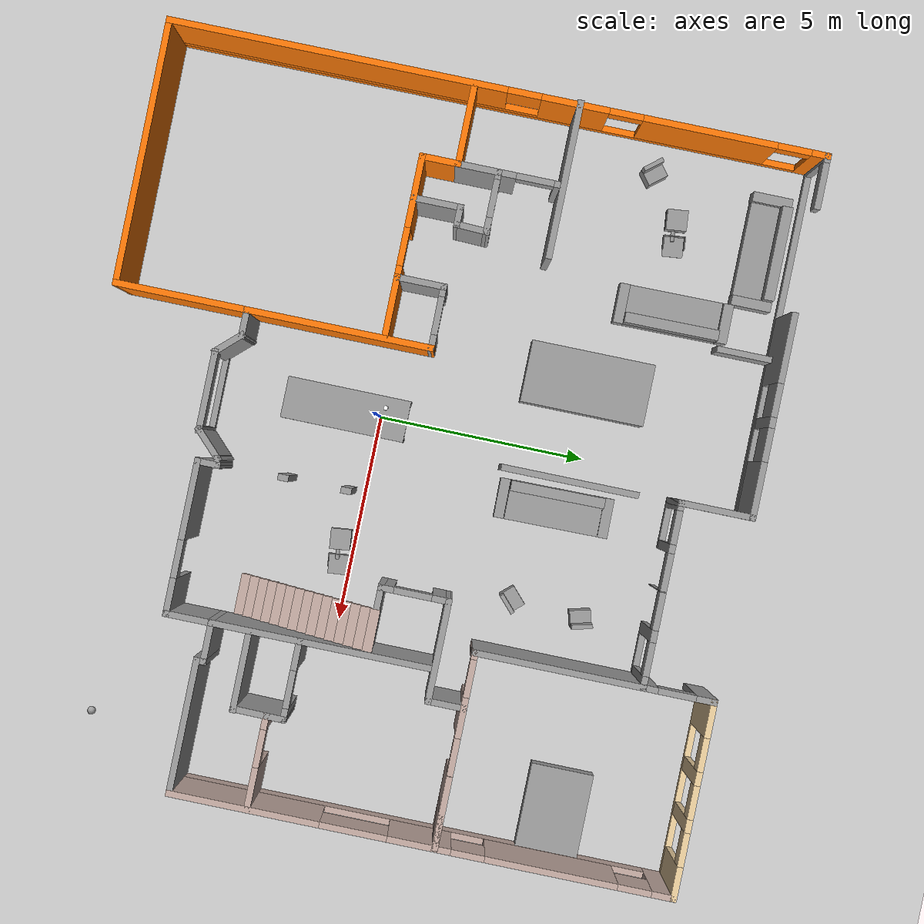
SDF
<sdf version="1.6">
 <world name="default">
  <plugin name="hello" filename="libhello.so"/>
  <light name="sun" type="directional">
   <pose>0 0 10 0 -0 0</pose>
   <diffuse>0.8 0.8 0.8 1</diffuse>
   <specular>0.2 0.2 0.2 1</specular>
   <attenuation>
    <range>1000</range>
    <constant>0.9</constant>
    <linear>0.01</linear>
    <quadratic>0.001</quadratic>
   </attenuation>
   <direction>-0.5 0.1 -0.9</direction>
  </light>
  <model name="ground_plane">
   <static>1</static>
   <link name="link">
    <collision name="collision">
     <geometry><plane><normal>0 0 1</normal><size>100 100</size></plane></geometry>
     <surface><friction><ode><mu>100</mu><mu2>50</mu2></ode></friction></surface>
    </collision>
    <visual name="visual">
     <cast_shadows>0</cast_shadows>
     <geometry><plane><normal>0 0 1</normal><size>100 100</size></plane></geometry>
     <material>
      <script><uri>file://media/materials/scripts/gazebo.material</uri><name>Gazebo/Grey</name></script>
     </material>
    </visual>
   </link>
  </model>
  <gravity>0 0 -9.8</gravity>
  <magnetic_field>6e-06 2.3e-05 -4.2e-05</magnetic_field>
  <atmosphere type="adiabatic"/>
  <physics name="default_physics" default="0" type="ode">
   <max_step_size>0.001</max_step_size>
   <real_time_factor>1</real_time_factor>
   <real_time_update_rate>1000</real_time_update_rate>
  </physics>
  <scene><ambient>0.4 0.4 0.4 1</ambient><background>0.7 0.7 0.7 1</background><shadows>1</shadows></scene>
  <spherical_coordinates>
   <surface_model>EARTH_WGS84</surface_model>
   <latitude_deg>0</latitude_deg>
   <longitude_deg>0</longitude_deg>
   <elevation>0</elevation>
   <heading_deg>0</heading_deg>
  </spherical_coordinates>
  <model name="MDP-Home">
   <pose>0.766606 1.22436 0 0 -0 0</pose>
   <link name="Stairs_1">
    <visual name="Stairs_1_Visual_0">
     <pose>4.13477 -3.63656 0.083333 0 -0 -3.14159</pose>
     <geometry><box><size>1 0.235267 0.166667</size></box></geometry>
     <material>
      <script><uri>file://media/materials/scripts/gazebo.material</uri><name>Gazebo/Grey</name></script>
      <ambient>0.760784 0.662745 0.627451 1</ambient>
     </material>
     <meta><layer>0</layer></meta>
    </visual>
    <collision name="Stairs_1_Collision_0">
     <geometry><box><size>1 0.235267 0.166667</size></box></geometry>
     <pose>4.13477 -3.63656 0.083333 0 -0 -3.14159</pose>
    </collision>
    <visual name="Stairs_1_Visual_1">
     <pose>4.13477 -3.4013 0.25 0 -0 -3.14159</pose>
     <geometry><box><size>1 0.235267 0.166667</size></box></geometry>
     <material>
      <script><uri>file://media/materials/scripts/gazebo.material</uri><name>Gazebo/Grey</name></script>
      <ambient>0.760784 0.662745 0.627451 1</ambient>
     </material>
     <meta><layer>0</layer></meta>
    </visual>
    <collision name="Stairs_1_Collision_1">
     <geometry><box><size>1 0.235267 0.166667</size></box></geometry>
     <pose>4.13477 -3.4013 0.25 0 -0 -3.14159</pose>
    </collision>
    <visual name="Stairs_1_Visual_2">
     <pose>4.13477 -3.16603 0.416667 0 -0 -3.14159</pose>
     <geometry><box><size>1 0.235267 0.166667</size></box></geometry>
     <material>
      <script><uri>file://media/materials/scripts/gazebo.material</uri><name>Gazebo/Grey</name></script>
      <ambient>0.760784 0.662745 0.627451 1</ambient>
     </material>
     <meta><layer>0</layer></meta>
    </visual>
    <collision name="Stairs_1_Collision_2">
     <geometry><box><size>1 0.235267 0.166667</size></box></geometry>
     <pose>4.13477 -3.16603 0.416667 0 -0 -3.14159</pose>
    </collision>
    <visual name="Stairs_1_Visual_3">
     <pose>4.13477 -2.93076 0.583333 0 -0 -3.14159</pose>
     <geometry><box><size>1 0.235267 0.166667</size></box></geometry>
     <material>
      <script><uri>file://media/materials/scripts/gazebo.material</uri><name>Gazebo/Grey</name></script>
      <ambient>0.760784 0.662745 0.627451 1</ambient>
     </material>
     <meta><layer>0</layer></meta>
    </visual>
    <collision name="Stairs_1_Collision_3">
     <geometry><box><size>1 0.235267 0.166667</size></box></geometry>
     <pose>4.13477 -2.93076 0.583333 0 -0 -3.14159</pose>
    </collision>
    <visual name="Stairs_1_Visual_4">
     <pose>4.13477 -2.6955 0.75 0 -0 -3.14159</pose>
     <geometry><box><size>1 0.235267 0.166667</size></box></geometry>
     <material>
      <script><uri>file://media/materials/scripts/gazebo.material</uri><name>Gazebo/Grey</name></script>
      <ambient>0.760784 0.662745 0.627451 1</ambient>
     </material>
     <meta><layer>0</layer></meta>
    </visual>
    <collision name="Stairs_1_Collision_4">
     <geometry><box><size>1 0.235267 0.166667</size></box></geometry>
     <pose>4.13477 -2.6955 0.75 0 -0 -3.14159</pose>
    </collision>
    <visual name="Stairs_1_Visual_5">
     <pose>4.13477 -2.46023 0.916667 0 -0 -3.14159</pose>
     <geometry><box><size>1 0.235267 0.166667</size></box></geometry>
     <material>
      <script><uri>file://media/materials/scripts/gazebo.material</uri><name>Gazebo/Grey</name></script>
      <ambient>0.760784 0.662745 0.627451 1</ambient>
     </material>
     <meta><layer>0</layer></meta>
    </visual>
    <collision name="Stairs_1_Collision_5">
     <geometry><box><size>1 0.235267 0.166667</size></box></geometry>
     <pose>4.13477 -2.46023 0.916667 0 -0 -3.14159</pose>
    </collision>
    <visual name="Stairs_1_Visual_6">
     <pose>4.13477 -2.22496 1.08333 0 -0 -3.14159</pose>
     <geometry><box><size>1 0.235267 0.166667</size></box></geometry>
     <material>
      <script><uri>file://media/materials/scripts/gazebo.material</uri><name>Gazebo/Grey</name></script>
      <ambient>0.760784 0.662745 0.627451 1</ambient>
     </material>
     <meta><layer>0</layer></meta>
    </visual>
    <collision name="Stairs_1_Collision_6">
     <geometry><box><size>1 0.235267 0.166667</size></box></geometry>
     <pose>4.13477 -2.22496 1.08333 0 -0 -3.14159</pose>
    </collision>
    <visual name="Stairs_1_Visual_7">
     <pose>4.13477 -1.9897 1.25 0 -0 -3.14159</pose>
     <geometry><box><size>1 0.235267 0.166667</size></box></geometry>
     <material>
      <script><uri>file://media/materials/scripts/gazebo.material</uri><name>Gazebo/Grey</name></script>
      <ambient>0.760784 0.662745 0.627451 1</ambient>
     </material>
     <meta><layer>0</layer></meta>
    </visual>
    <collision name="Stairs_1_Collision_7">
     <geometry><box><size>1 0.235267 0.166667</size></box></geometry>
     <pose>4.13477 -1.9897 1.25 0 -0 -3.14159</pose>
    </collision>
    <visual name="Stairs_1_Visual_8">
     <pose>4.13477 -1.75443 1.41667 0 -0 -3.14159</pose>
     <geometry><box><size>1 0.235267 0.166667</size></box></geometry>
     <material>
      <script><uri>file://media/materials/scripts/gazebo.material</uri><name>Gazebo/Grey</name></script>
      <ambient>0.760784 0.662745 0.627451 1</ambient>
     </material>
     <meta><layer>0</layer></meta>
    </visual>
    <collision name="Stairs_1_Collision_8">
     <geometry><box><size>1 0.235267 0.166667</size></box></geometry>
     <pose>4.13477 -1.75443 1.41667 0 -0 -3.14159</pose>
    </collision>
    <visual name="Stairs_1_Visual_9">
     <pose>4.13477 -1.51916 1.58333 0 -0 -3.14159</pose>
     <geometry><box><size>1 0.235267 0.166667</size></box></geometry>
     <material>
      <script><uri>file://media/materials/scripts/gazebo.material</uri><name>Gazebo/Grey</name></script>
      <ambient>0.760784 0.662745 0.627451 1</ambient>
     </material>
     <meta><layer>0</layer></meta>
    </visual>
    <collision name="Stairs_1_Collision_9">
     <geometry><box><size>1 0.235267 0.166667</size></box></geometry>
     <pose>4.13477 -1.51916 1.58333 0 -0 -3.14159</pose>
    </collision>
    <visual name="Stairs_1_Visual_10">
     <pose>4.13477 -1.2839 1.75 0 -0 -3.14159</pose>
     <geometry><box><size>1 0.235267 0.166667</size></box></geometry>
     <material>
      <script><uri>file://media/materials/scripts/gazebo.material</uri><name>Gazebo/Grey</name></script>
      <ambient>0.760784 0.662745 0.627451 1</ambient>
     </material>
     <meta><layer>0</layer></meta>
    </visual>
    <collision name="Stairs_1_Collision_10">
     <geometry><box><size>1 0.235267 0.166667</size></box></geometry>
     <pose>4.13477 -1.2839 1.75 0 -0 -3.14159</pose>
    </collision>
    <visual name="Stairs_1_Visual_11">
     <pose>4.13477 -1.04863 1.91667 0 -0 -3.14159</pose>
     <geometry><box><size>1 0.235267 0.166667</size></box></geometry>
     <material>
      <script><uri>file://media/materials/scripts/gazebo.material</uri><name>Gazebo/Grey</name></script>
      <ambient>0.760784 0.662745 0.627451 1</ambient>
     </material>
     <meta><layer>0</layer></meta>
    </visual>
    <collision name="Stairs_1_Collision_11">
     <geometry><box><size>1 0.235267 0.166667</size></box></geometry>
     <pose>4.13477 -1.04863 1.91667 0 -0 -3.14159</pose>
    </collision>
    <visual name="Stairs_1_Visual_12">
     <pose>4.13477 -0.813364 2.08333 0 -0 -3.14159</pose>
     <geometry><box><size>1 0.235267 0.166667</size></box></geometry>
     <material>
      <script><uri>file://media/materials/scripts/gazebo.material</uri><name>Gazebo/Grey</name></script>
      <ambient>0.760784 0.662745 0.627451 1</ambient>
     </material>
     <meta><layer>0</layer></meta>
    </visual>
    <collision name="Stairs_1_Collision_12">
     <geometry><box><size>1 0.235267 0.166667</size></box></geometry>
     <pose>4.13477 -0.813364 2.08333 0 -0 -3.14159</pose>
    </collision>
    <visual name="Stairs_1_Visual_13">
     <pose>4.13477 -0.578097 2.25 0 -0 -3.14159</pose>
     <geometry><box><size>1 0.235267 0.166667</size></box></geometry>
     <material>
      <script><uri>file://media/materials/scripts/gazebo.material</uri><name>Gazebo/Grey</name></script>
      <ambient>0.760784 0.662745 0.627451 1</ambient>
     </material>
     <meta><layer>0</layer></meta>
    </visual>
    <collision name="Stairs_1_Collision_13">
     <geometry><box><size>1 0.235267 0.166667</size></box></geometry>
     <pose>4.13477 -0.578097 2.25 0 -0 -3.14159</pose>
    </collision>
    <visual name="Stairs_1_Visual_14">
     <pose>4.13477 -0.342831 2.41667 0 -0 -3.14159</pose>
     <geometry><box><size>1 0.235267 0.166667</size></box></geometry>
     <material>
      <script><uri>file://media/materials/scripts/gazebo.material</uri><name>Gazebo/Grey</name></script>
      <ambient>0.760784 0.662745 0.627451 1</ambient>
     </material>
     <meta><layer>0</layer></meta>
    </visual>
    <collision name="Stairs_1_Collision_14">
     <geometry><box><size>1 0.235267 0.166667</size></box></geometry>
     <pose>4.13477 -0.342831 2.41667 0 -0 -3.14159</pose>
    </collision>
   </link>
   <link name="Wall_0">
    <pose>-8.74311 -0.006919 0 0 0 -1.57011</pose>
    <visual name="Wall_0_Visual_0">
     <pose>-7.6212 0 1.25 0 -0 0</pose>
     <geometry><box><size>0.454575 0.15 2.5</size></box></geometry>
     <material>
      <script><uri>file://media/materials/scripts/gazebo.material</uri><name>Gazebo/Grey</name></script>
      <ambient>0.996078 0.47451 0.0196078 1</ambient>
     </material>
     <meta><layer>0</layer></meta>
    </visual>
    <collision name="Wall_0_Collision_0">
     <geometry><box><size>0.454575 0.15 2.5</size></box></geometry>
     <pose>-7.6212 0 1.25 0 -0 0</pose>
    </collision>
    <visual name="Wall_0_Visual_1">
     <pose>0.227288 0 0.125 0 -0 0</pose>
     <geometry><box><size>15.2424 0.15 0.25</size></box></geometry>
     <material>
      <script><uri>file://media/materials/scripts/gazebo.material</uri><name>Gazebo/Grey</name></script>
      <ambient>0.996078 0.47451 0.0196078 1</ambient>
     </material>
     <meta><layer>0</layer></meta>
    </visual>
    <collision name="Wall_0_Collision_1">
     <geometry><box><size>15.2424 0.15 0.25</size></box></geometry>
     <pose>0.227288 0 0.125 0 -0 0</pose>
    </collision>
    <visual name="Wall_0_Visual_2">
     <pose>-5.00939 0 1.375 0 -0 0</pose>
     <geometry><box><size>3.16905 0.15 2.25</size></box></geometry>
     <material>
      <script><uri>file://media/materials/scripts/gazebo.material</uri><name>Gazebo/Grey</name></script>
      <ambient>0.996078 0.47451 0.0196078 1</ambient>
     </material>
     <meta><layer>0</layer></meta>
    </visual>
    <collision name="Wall_0_Collision_2">
     <geometry><box><size>3.16905 0.15 2.25</size></box></geometry>
     <pose>-5.00939 0 1.375 0 -0 0</pose>
    </collision>
    <visual name="Wall_0_Visual_3">
     <pose>-1.82212 0 1.375 0 -0 0</pose>
     <geometry><box><size>1.6055 0.15 2.25</size></box></geometry>
     <material>
      <script><uri>file://media/materials/scripts/gazebo.material</uri><name>Gazebo/Grey</name></script>
      <ambient>0.996078 0.47451 0.0196078 1</ambient>
     </material>
     <meta><layer>0</layer></meta>
    </visual>
    <collision name="Wall_0_Collision_3">
     <geometry><box><size>1.6055 0.15 2.25</size></box></geometry>
     <pose>-1.82212 0 1.375 0 -0 0</pose>
    </collision>
    <visual name="Wall_0_Visual_4">
     <pose>3.41456 0 0.375 0 -0 0</pose>
     <geometry><box><size>8.86785 0.15 0.25</size></box></geometry>
     <material>
      <script><uri>file://media/materials/scripts/gazebo.material</uri><name>Gazebo/Grey</name></script>
      <ambient>0.996078 0.47451 0.0196078 1</ambient>
     </material>
     <meta><layer>0</layer></meta>
    </visual>
    <collision name="Wall_0_Collision_4">
     <geometry><box><size>8.86785 0.15 0.25</size></box></geometry>
     <pose>3.41456 0 0.375 0 -0 0</pose>
    </collision>
    <visual name="Wall_0_Visual_5">
     <pose>3.81456 0 1.5 0 -0 0</pose>
     <geometry><box><size>8.06785 0.15 2</size></box></geometry>
     <material>
      <script><uri>file://media/materials/scripts/gazebo.material</uri><name>Gazebo/Grey</name></script>
      <ambient>0.996078 0.47451 0.0196078 1</ambient>
     </material>
     <meta><layer>0</layer></meta>
    </visual>
    <collision name="Wall_0_Collision_5">
     <geometry><box><size>8.06785 0.15 2</size></box></geometry>
     <pose>3.81456 0 1.5 0 -0 0</pose>
    </collision>
    <visual name="Wall_0_Visual_6">
     <pose>-0.619366 0 1.9 0 -0 0</pose>
     <geometry><box><size>0.8 0.15 1.2</size></box></geometry>
     <material>
      <script><uri>file://media/materials/scripts/gazebo.material</uri><name>Gazebo/Grey</name></script>
      <ambient>0.996078 0.47451 0.0196078 1</ambient>
     </material>
     <meta><layer>0</layer></meta>
    </visual>
    <collision name="Wall_0_Collision_6">
     <geometry><box><size>0.8 0.15 1.2</size></box></geometry>
     <pose>-0.619366 0 1.9 0 -0 0</pose>
    </collision>
    <visual name="Wall_0_Visual_7">
     <pose>-6.99391 0 2.25 0 -0 0</pose>
     <geometry><box><size>0.8 0.15 0.5</size></box></geometry>
     <material>
      <script><uri>file://media/materials/scripts/gazebo.material</uri><name>Gazebo/Grey</name></script>
      <ambient>0.996078 0.47451 0.0196078 1</ambient>
     </material>
     <meta><layer>0</layer></meta>
    </visual>
    <collision name="Wall_0_Collision_7">
     <geometry><box><size>0.8 0.15 0.5</size></box></geometry>
     <pose>-6.99391 0 2.25 0 -0 0</pose>
    </collision>
    <visual name="Wall_0_Visual_8">
     <pose>-3.02487 0 2.25 0 -0 0</pose>
     <geometry><box><size>0.8 0.15 0.5</size></box></geometry>
     <material>
      <script><uri>file://media/materials/scripts/gazebo.material</uri><name>Gazebo/Grey</name></script>
      <ambient>0.996078 0.47451 0.0196078 1</ambient>
     </material>
     <meta><layer>0</layer></meta>
    </visual>
    <collision name="Wall_0_Collision_8">
     <geometry><box><size>0.8 0.15 0.5</size></box></geometry>
     <pose>-3.02487 0 2.25 0 -0 0</pose>
    </collision>
   </link>
   <link name="Wall_100">
    <collision name="Wall_100_Collision">
     <geometry><box><size>4.115 0.15 2.5</size></box></geometry>
     <pose>0 0 1.25 0 -0 0</pose>
    </collision>
    <visual name="Wall_100_Visual">
     <pose>0 0 1.25 0 -0 0</pose>
     <geometry><box><size>4.115 0.15 2.5</size></box></geometry>
     <material>
      <script><uri>file://media/materials/scripts/gazebo.material</uri><name>Gazebo/Grey</name></script>
      <ambient>1 1 1 1</ambient>
     </material>
     <meta><layer>0</layer></meta>
    </visual>
    <pose>4.14955 4.10506 0 0 0 -1.5708</pose>
   </link>
   <link name="Wall_102">
    <pose>6.44955 2.12256 0 0 -0 0</pose>
    <visual name="Wall_102_Visual_0">
     <pose>-2.25671 0 1.25 0 -0 0</pose>
     <geometry><box><size>0.236575 0.15 2.5</size></box></geometry>
     <material>
      <script><uri>file://media/materials/scripts/gazebo.material</uri><name>Gazebo/Grey</name></script>
      <ambient>0.760784 0.662745 0.627451 1</ambient>
     </material>
     <meta><layer>0</layer></meta>
    </visual>
    <collision name="Wall_102_Collision_0">
     <geometry><box><size>0.236575 0.15 2.5</size></box></geometry>
     <pose>-2.25671 0 1.25 0 -0 0</pose>
    </collision>
    <visual name="Wall_102_Visual_1">
     <pose>-0.757484 0 1.25 0 -0 0</pose>
     <geometry><box><size>0.961882 0.15 2.5</size></box></geometry>
     <material>
      <script><uri>file://media/materials/scripts/gazebo.material</uri><name>Gazebo/Grey</name></script>
      <ambient>0.760784 0.662745 0.627451 1</ambient>
     </material>
     <meta><layer>0</layer></meta>
    </visual>
    <collision name="Wall_102_Collision_1">
     <geometry><box><size>0.961882 0.15 2.5</size></box></geometry>
     <pose>-0.757484 0 1.25 0 -0 0</pose>
    </collision>
    <visual name="Wall_102_Visual_2">
     <pose>1.49923 0 1.25 0 -0 0</pose>
     <geometry><box><size>1.75154 0.15 2.5</size></box></geometry>
     <material>
      <script><uri>file://media/materials/scripts/gazebo.material</uri><name>Gazebo/Grey</name></script>
      <ambient>0.760784 0.662745 0.627451 1</ambient>
     </material>
     <meta><layer>0</layer></meta>
    </visual>
    <collision name="Wall_102_Collision_2">
     <geometry><box><size>1.75154 0.15 2.5</size></box></geometry>
     <pose>1.49923 0 1.25 0 -0 0</pose>
    </collision>
    <visual name="Wall_102_Visual_3">
     <pose>1.94534 0 1.25 0 -0 0</pose>
     <geometry><box><size>0.859329 0.15 2.5</size></box></geometry>
     <material>
      <script><uri>file://media/materials/scripts/gazebo.material</uri><name>Gazebo/Grey</name></script>
      <ambient>0.760784 0.662745 0.627451 1</ambient>
     </material>
     <meta><layer>0</layer></meta>
    </visual>
    <collision name="Wall_102_Collision_3">
     <geometry><box><size>0.859329 0.15 2.5</size></box></geometry>
     <pose>1.94534 0 1.25 0 -0 0</pose>
    </collision>
    <visual name="Wall_102_Visual_4">
     <pose>-1.68843 0 2.25 0 -0 0</pose>
     <geometry><box><size>0.9 0.15 0.5</size></box></geometry>
     <material>
      <script><uri>file://media/materials/scripts/gazebo.material</uri><name>Gazebo/Grey</name></script>
      <ambient>0.760784 0.662745 0.627451 1</ambient>
     </material>
     <meta><layer>0</layer></meta>
    </visual>
    <collision name="Wall_102_Collision_4">
     <geometry><box><size>0.9 0.15 0.5</size></box></geometry>
     <pose>-1.68843 0 2.25 0 -0 0</pose>
    </collision>
    <visual name="Wall_102_Visual_5">
     <pose>0.169564 0 2.25 0 -0 0</pose>
     <geometry><box><size>0.892214 0.15 0.5</size></box></geometry>
     <material>
      <script><uri>file://media/materials/scripts/gazebo.material</uri><name>Gazebo/Grey</name></script>
      <ambient>0.760784 0.662745 0.627451 1</ambient>
     </material>
     <meta><layer>0</layer></meta>
    </visual>
    <collision name="Wall_102_Collision_5">
     <geometry><box><size>0.892214 0.15 0.5</size></box></geometry>
     <pose>0.169564 0 2.25 0 -0 0</pose>
    </collision>
   </link>
   <link name="Wall_104">
    <collision name="Wall_104_Collision">
     <geometry><box><size>0.991 0.15 2.5</size></box></geometry>
     <pose>0 0 1.25 0 -0 0</pose>
    </collision>
    <visual name="Wall_104_Visual">
     <pose>0 0 1.25 0 -0 0</pose>
     <geometry><box><size>0.991 0.15 2.5</size></box></geometry>
     <material>
      <script><uri>file://media/materials/scripts/gazebo.material</uri><name>Gazebo/Grey</name></script>
      <ambient>1 1 1 1</ambient>
     </material>
     <meta><layer>0</layer></meta>
    </visual>
    <pose>5.46534 1.70115 0 0 0 -1.5708</pose>
   </link>
   <link name="Wall_107">
    <collision name="Wall_107_Collision">
     <geometry><box><size>2.5 0.15 2.5</size></box></geometry>
     <pose>0 0 1.25 0 -0 0</pose>
    </collision>
    <visual name="Wall_107_Visual">
     <pose>0 0 1.25 0 -0 0</pose>
     <geometry><box><size>2.5 0.15 2.5</size></box></geometry>
     <material>
      <script><uri>file://media/materials/scripts/gazebo.material</uri><name>Gazebo/Grey</name></script>
      <ambient>1 1 1 1</ambient>
     </material>
     <meta><layer>0</layer></meta>
    </visual>
    <pose>4.29034 1.28065 0 0 -0 3.14159</pose>
   </link>
   <link name="Wall_109">
    <collision name="Wall_109_Collision">
     <geometry><box><size>5.3 0.15 2.5</size></box></geometry>
     <pose>0 0 1.25 0 -0 0</pose>
    </collision>
    <visual name="Wall_109_Visual">
     <pose>0 0 1.25 0 -0 0</pose>
     <geometry><box><size>5.3 0.15 2.5</size></box></geometry>
     <material>
      <script><uri>file://media/materials/scripts/gazebo.material</uri><name>Gazebo/Grey</name></script>
      <ambient>1 1 1 1</ambient>
     </material>
     <meta><layer>0</layer></meta>
    </visual>
    <pose>4.71555 -1.42344 0 0 -0 1.5708</pose>
   </link>
   <link name="Wall_111">
    <collision name="Wall_111_Collision">
     <geometry><box><size>1.96718 0.15 2.5</size></box></geometry>
     <pose>0 0 1.25 0 -0 0</pose>
    </collision>
    <visual name="Wall_111_Visual">
     <pose>0 0 1.25 0 -0 0</pose>
     <geometry><box><size>1.96718 0.15 2.5</size></box></geometry>
     <material>
      <script><uri>file://media/materials/scripts/gazebo.material</uri><name>Gazebo/Grey</name></script>
      <ambient>1 1 1 1</ambient>
     </material>
     <meta><layer>0</layer></meta>
    </visual>
    <pose>5.66115 -3.09931 0 0 -0 0</pose>
   </link>
   <link name="Wall_112">
    <collision name="Wall_112_Collision">
     <geometry><box><size>1.33381 0.15 2.5</size></box></geometry>
     <pose>0 0 1.25 0 -0 0</pose>
    </collision>
    <visual name="Wall_112_Visual">
     <pose>0 0 1.25 0 -0 0</pose>
     <geometry><box><size>1.33381 0.15 2.5</size></box></geometry>
     <material>
      <script><uri>file://media/materials/scripts/gazebo.material</uri><name>Gazebo/Grey</name></script>
      <ambient>1 1 1 1</ambient>
     </material>
     <meta><layer>0</layer></meta>
    </visual>
    <pose>6.56113 -2.50746 0 0 -0 1.55716</pose>
   </link>
   <link name="Wall_113">
    <pose>5.64419 -1.91561 0 0 -0 3.14159</pose>
    <visual name="Wall_113_Visual_0">
     <pose>-0.830337 0 1.25 0 -0 0</pose>
     <geometry><box><size>0.339326 0.15 2.5</size></box></geometry>
     <material>
      <script><uri>file://media/materials/scripts/gazebo.material</uri><name>Gazebo/Grey</name></script>
      <ambient>1 1 1 1</ambient>
     </material>
     <meta><layer>0</layer></meta>
    </visual>
    <collision name="Wall_113_Collision_0">
     <geometry><box><size>0.339326 0.15 2.5</size></box></geometry>
     <pose>-0.830337 0 1.25 0 -0 0</pose>
    </collision>
    <visual name="Wall_113_Visual_1">
     <pose>0.619663 0 1.25 0 -0 0</pose>
     <geometry><box><size>0.760674 0.15 2.5</size></box></geometry>
     <material>
      <script><uri>file://media/materials/scripts/gazebo.material</uri><name>Gazebo/Grey</name></script>
      <ambient>1 1 1 1</ambient>
     </material>
     <meta><layer>0</layer></meta>
    </visual>
    <collision name="Wall_113_Collision_1">
     <geometry><box><size>0.760674 0.15 2.5</size></box></geometry>
     <pose>0.619663 0 1.25 0 -0 0</pose>
    </collision>
    <visual name="Wall_113_Visual_2">
     <pose>-0.210674 0 2.25 0 -0 0</pose>
     <geometry><box><size>0.9 0.15 0.5</size></box></geometry>
     <material>
      <script><uri>file://media/materials/scripts/gazebo.material</uri><name>Gazebo/Grey</name></script>
      <ambient>1 1 1 1</ambient>
     </material>
     <meta><layer>0</layer></meta>
    </visual>
    <collision name="Wall_113_Collision_2">
     <geometry><box><size>0.9 0.15 0.5</size></box></geometry>
     <pose>-0.210674 0 2.25 0 -0 0</pose>
    </collision>
   </link>
   <link name="Wall_120">
    <pose>7.65135 -2.31717 0 0 -0 0</pose>
    <visual name="Wall_120_Visual_0">
     <pose>-0.959065 0 1.25 0 -0 0</pose>
     <geometry><box><size>0.38187 0.15 2.5</size></box></geometry>
     <material>
      <script><uri>file://media/materials/scripts/gazebo.material</uri><name>Gazebo/Grey</name></script>
      <ambient>0.760784 0.662745 0.627451 1</ambient>
     </material>
     <meta><layer>0</layer></meta>
    </visual>
    <collision name="Wall_120_Collision_0">
     <geometry><box><size>0.38187 0.15 2.5</size></box></geometry>
     <pose>-0.959065 0 1.25 0 -0 0</pose>
    </collision>
    <visual name="Wall_120_Visual_1">
     <pose>0.640935 0 1.25 0 -0 0</pose>
     <geometry><box><size>1.01813 0.15 2.5</size></box></geometry>
     <material>
      <script><uri>file://media/materials/scripts/gazebo.material</uri><name>Gazebo/Grey</name></script>
      <ambient>0.760784 0.662745 0.627451 1</ambient>
     </material>
     <meta><layer>0</layer></meta>
    </visual>
    <collision name="Wall_120_Collision_1">
     <geometry><box><size>1.01813 0.15 2.5</size></box></geometry>
     <pose>0.640935 0 1.25 0 -0 0</pose>
    </collision>
    <visual name="Wall_120_Visual_2">
     <pose>-0.31813 0 2.25 0 -0 0</pose>
     <geometry><box><size>0.9 0.15 0.5</size></box></geometry>
     <material>
      <script><uri>file://media/materials/scripts/gazebo.material</uri><name>Gazebo/Grey</name></script>
      <ambient>0.760784 0.662745 0.627451 1</ambient>
     </material>
     <meta><layer>0</layer></meta>
    </visual>
    <collision name="Wall_120_Collision_2">
     <geometry><box><size>0.9 0.15 0.5</size></box></geometry>
     <pose>-0.31813 0 2.25 0 -0 0</pose>
    </collision>
   </link>
   <link name="Wall_122">
    <pose>3.11537 0.480642 0 0 0 -1.57076</pose>
    <visual name="Wall_122_Visual_0">
     <pose>-0.636924 0 1.25 0 -0 0</pose>
     <geometry><box><size>0.476152 0.15 2.5</size></box></geometry>
     <material>
      <script><uri>file://media/materials/scripts/gazebo.material</uri><name>Gazebo/Grey</name></script>
      <ambient>1 1 1 1</ambient>
     </material>
     <meta><layer>0</layer></meta>
    </visual>
    <collision name="Wall_122_Collision_0">
     <geometry><box><size>0.476152 0.15 2.5</size></box></geometry>
     <pose>-0.636924 0 1.25 0 -0 0</pose>
    </collision>
    <visual name="Wall_122_Visual_1">
     <pose>0.688076 0 1.25 0 -0 0</pose>
     <geometry><box><size>0.373848 0.15 2.5</size></box></geometry>
     <material>
      <script><uri>file://media/materials/scripts/gazebo.material</uri><name>Gazebo/Grey</name></script>
      <ambient>1 1 1 1</ambient>
     </material>
     <meta><layer>0</layer></meta>
    </visual>
    <collision name="Wall_122_Collision_1">
     <geometry><box><size>0.373848 0.15 2.5</size></box></geometry>
     <pose>0.688076 0 1.25 0 -0 0</pose>
    </collision>
    <visual name="Wall_122_Visual_2">
     <pose>0.051152 0 2.25 0 -0 0</pose>
     <geometry><box><size>0.9 0.15 0.5</size></box></geometry>
     <material>
      <script><uri>file://media/materials/scripts/gazebo.material</uri><name>Gazebo/Grey</name></script>
      <ambient>1 1 1 1</ambient>
     </material>
     <meta><layer>0</layer></meta>
    </visual>
    <collision name="Wall_122_Collision_2">
     <geometry><box><size>0.9 0.15 0.5</size></box></geometry>
     <pose>0.051152 0 2.25 0 -0 0</pose>
    </collision>
   </link>
   <link name="Wall_123">
    <collision name="Wall_123_Collision">
     <geometry><box><size>1.65 0.15 2.5</size></box></geometry>
     <pose>0 0 1.25 0 -0 0</pose>
    </collision>
    <visual name="Wall_123_Visual">
     <pose>0 0 1.25 0 -0 0</pose>
     <geometry><box><size>1.65 0.15 2.5</size></box></geometry>
     <material>
      <script><uri>file://media/materials/scripts/gazebo.material</uri><name>Gazebo/Grey</name></script>
      <ambient>1 1 1 1</ambient>
     </material>
     <meta><layer>0</layer></meta>
    </visual>
    <pose>3.86539 -0.319363 0 0 -0 0</pose>
   </link>
   <link name="Wall_125">
    <collision name="Wall_125_Collision">
     <geometry><box><size>0.25 0.15 2.5</size></box></geometry>
     <pose>0 0 1.25 0 -0 0</pose>
    </collision>
    <visual name="Wall_125_Visual">
     <pose>0 0 1.25 0 -0 0</pose>
     <geometry><box><size>0.25 0.15 2.5</size></box></geometry>
     <material>
      <script><uri>file://media/materials/scripts/gazebo.material</uri><name>Gazebo/Grey</name></script>
      <ambient>1 1 1 1</ambient>
     </material>
     <meta><layer>0</layer></meta>
    </visual>
    <pose>1.08912 -3.0518 0 0 -0 1.5708</pose>
   </link>
   <link name="Wall_127">
    <collision name="Wall_127_Collision">
     <geometry><box><size>0.25 0.15 2.5</size></box></geometry>
     <pose>0 0 1.25 0 -0 0</pose>
    </collision>
    <visual name="Wall_127_Visual">
     <pose>0 0 1.25 0 -0 0</pose>
     <geometry><box><size>0.25 0.15 2.5</size></box></geometry>
     <material>
      <script><uri>file://media/materials/scripts/gazebo.material</uri><name>Gazebo/Grey</name></script>
      <ambient>1 1 1 1</ambient>
     </material>
     <meta><layer>0</layer></meta>
    </visual>
    <pose>1.08912 -1.56596 0 0 -0 1.5708</pose>
   </link>
   <link name="Wall_131">
    <collision name="Wall_131_Collision">
     <geometry><box><size>4.5 0.15 2.5</size></box></geometry>
     <pose>0 0 1.25 0 -0 0</pose>
    </collision>
    <visual name="Wall_131_Visual">
     <pose>0 0 1.25 0 -0 0</pose>
     <geometry><box><size>4.5 0.15 2.5</size></box></geometry>
     <material>
      <script><uri>file://media/materials/scripts/gazebo.material</uri><name>Gazebo/Grey</name></script>
      <ambient>0.996078 0.47451 0.0196078 1</ambient>
     </material>
     <meta><layer>0</layer></meta>
    </visual>
    <pose>-2.5378 -2.48595 0 0 -0 1.5708</pose>
   </link>
   <link name="Wall_133">
    <collision name="Wall_133_Collision">
     <geometry><box><size>1.5 0.15 2.5</size></box></geometry>
     <pose>0 0 1.25 0 -0 0</pose>
    </collision>
    <visual name="Wall_133_Visual">
     <pose>0 0 1.25 0 -0 0</pose>
     <geometry><box><size>1.5 0.15 2.5</size></box></geometry>
     <material>
      <script><uri>file://media/materials/scripts/gazebo.material</uri><name>Gazebo/Grey</name></script>
      <ambient>0.996078 0.47451 0.0196078 1</ambient>
     </material>
     <meta><layer>0</layer></meta>
    </visual>
    <pose>-3.31137 -1.41633 0 0 -0 3.14159</pose>
   </link>
   <link name="Wall_134">
    <collision name="Wall_134_Collision">
     <geometry><box><size>1.25 0.15 2.5</size></box></geometry>
     <pose>0 0 1.25 0 -0 0</pose>
    </collision>
    <visual name="Wall_134_Visual">
     <pose>0 0 1.25 0 -0 0</pose>
     <geometry><box><size>1.25 0.15 2.5</size></box></geometry>
     <material>
      <script><uri>file://media/materials/scripts/gazebo.material</uri><name>Gazebo/Grey</name></script>
      <ambient>1 1 1 1</ambient>
     </material>
     <meta><layer>0</layer></meta>
    </visual>
    <pose>-3.98637 -0.866325 0 0 -0 1.5708</pose>
   </link>
   <link name="Wall_135">
    <pose>-3.26208 -0.313636 0 0 -0 0.003712</pose>
    <visual name="Wall_135_Visual_0">
     <pose>-0.646197 0 1.25 0 -0 0</pose>
     <geometry><box><size>0.306179 0.15 2.5</size></box></geometry>
     <material>
      <script><uri>file://media/materials/scripts/gazebo.material</uri><name>Gazebo/Grey</name></script>
      <ambient>1 1 1 1</ambient>
     </material>
     <meta><layer>0</layer></meta>
    </visual>
    <collision name="Wall_135_Collision_0">
     <geometry><box><size>0.306179 0.15 2.5</size></box></geometry>
     <pose>-0.646197 0 1.25 0 -0 0</pose>
    </collision>
    <visual name="Wall_135_Visual_1">
     <pose>0.60309 0 1.25 0 -0 0</pose>
     <geometry><box><size>0.392394 0.15 2.5</size></box></geometry>
     <material>
      <script><uri>file://media/materials/scripts/gazebo.material</uri><name>Gazebo/Grey</name></script>
      <ambient>1 1 1 1</ambient>
     </material>
     <meta><layer>0</layer></meta>
    </visual>
    <collision name="Wall_135_Collision_1">
     <geometry><box><size>0.392394 0.15 2.5</size></box></geometry>
     <pose>0.60309 0 1.25 0 -0 0</pose>
    </collision>
    <visual name="Wall_135_Visual_2">
     <pose>-0.043107 0 2.25 0 -0 0</pose>
     <geometry><box><size>0.9 0.15 0.5</size></box></geometry>
     <material>
      <script><uri>file://media/materials/scripts/gazebo.material</uri><name>Gazebo/Grey</name></script>
      <ambient>1 1 1 1</ambient>
     </material>
     <meta><layer>0</layer></meta>
    </visual>
    <collision name="Wall_135_Collision_2">
     <geometry><box><size>0.9 0.15 0.5</size></box></geometry>
     <pose>-0.043107 0 2.25 0 -0 0</pose>
    </collision>
   </link>
   <link name="Wall_137">
    <pose>-5.41137 -1.41633 0 0 -0 3.14159</pose>
    <visual name="Wall_137_Visual_0">
     <pose>-1.32646 0 1.25 0 -0 0</pose>
     <geometry><box><size>0.347086 0.15 2.5</size></box></geometry>
     <material>
      <script><uri>file://media/materials/scripts/gazebo.material</uri><name>Gazebo/Grey</name></script>
      <ambient>0.996078 0.47451 0.0196078 1</ambient>
     </material>
     <meta><layer>0</layer></meta>
    </visual>
    <collision name="Wall_137_Collision_0">
     <geometry><box><size>0.347086 0.15 2.5</size></box></geometry>
     <pose>-1.32646 0 1.25 0 -0 0</pose>
    </collision>
    <visual name="Wall_137_Visual_1">
     <pose>0.623543 0 1.25 0 -0 0</pose>
     <geometry><box><size>1.75291 0.15 2.5</size></box></geometry>
     <material>
      <script><uri>file://media/materials/scripts/gazebo.material</uri><name>Gazebo/Grey</name></script>
      <ambient>0.996078 0.47451 0.0196078 1</ambient>
     </material>
     <meta><layer>0</layer></meta>
    </visual>
    <collision name="Wall_137_Collision_1">
     <geometry><box><size>1.75291 0.15 2.5</size></box></geometry>
     <pose>0.623543 0 1.25 0 -0 0</pose>
    </collision>
    <visual name="Wall_137_Visual_2">
     <pose>-0.702914 0 2.25 0 -0 0</pose>
     <geometry><box><size>0.9 0.15 0.5</size></box></geometry>
     <material>
      <script><uri>file://media/materials/scripts/gazebo.material</uri><name>Gazebo/Grey</name></script>
      <ambient>0.996078 0.47451 0.0196078 1</ambient>
     </material>
     <meta><layer>0</layer></meta>
    </visual>
    <collision name="Wall_137_Collision_2">
     <geometry><box><size>0.9 0.15 0.5</size></box></geometry>
     <pose>-0.702914 0 2.25 0 -0 0</pose>
    </collision>
   </link>
   <link name="Wall_138">
    <collision name="Wall_138_Collision">
     <geometry><box><size>1 0.15 2.5</size></box></geometry>
     <pose>0 0 1.25 0 -0 0</pose>
    </collision>
    <visual name="Wall_138_Visual">
     <pose>0 0 1.25 0 -0 0</pose>
     <geometry><box><size>1 0.15 2.5</size></box></geometry>
     <material>
      <script><uri>file://media/materials/scripts/gazebo.material</uri><name>Gazebo/Grey</name></script>
      <ambient>0.996078 0.47451 0.0196078 1</ambient>
     </material>
     <meta><layer>0</layer></meta>
    </visual>
    <pose>-6.83637 -0.991325 0 0 -0 1.5708</pose>
   </link>
   <link name="Wall_139">
    <collision name="Wall_139_Collision">
     <geometry><box><size>2 0.15 2.5</size></box></geometry>
     <pose>0 0 1.25 0 -0 0</pose>
    </collision>
    <visual name="Wall_139_Visual">
     <pose>0 0 1.25 0 -0 0</pose>
     <geometry><box><size>2 0.15 2.5</size></box></geometry>
     <material>
      <script><uri>file://media/materials/scripts/gazebo.material</uri><name>Gazebo/Grey</name></script>
      <ambient>0.996078 0.47451 0.0196078 1</ambient>
     </material>
     <meta><layer>0</layer></meta>
    </visual>
    <pose>-7.76137 -0.566325 0 0 -0 3.14159</pose>
   </link>
   <link name="Wall_141">
    <collision name="Wall_141_Collision">
     <geometry><box><size>1.10559 0.15 2.5</size></box></geometry>
     <pose>0 0 1.25 0 -0 0</pose>
    </collision>
    <visual name="Wall_141_Visual">
     <pose>0 0 1.25 0 -0 0</pose>
     <geometry><box><size>1.10559 0.15 2.5</size></box></geometry>
     <material>
      <script><uri>file://media/materials/scripts/gazebo.material</uri><name>Gazebo/Grey</name></script>
      <ambient>1 1 1 1</ambient>
     </material>
     <meta><layer>0</layer></meta>
    </visual>
    <pose>-6.83637 -0.088528 0 0 -0 1.5708</pose>
   </link>
   <link name="Wall_142">
    <pose>-6.13522 0.389268 0 0 -0 0</pose>
    <visual name="Wall_142_Visual_0">
     <pose>-0.655259 0 1.25 0 -0 0</pose>
     <geometry><box><size>0.241775 0.15 2.5</size></box></geometry>
     <material>
      <script><uri>file://media/materials/scripts/gazebo.material</uri><name>Gazebo/Grey</name></script>
      <ambient>1 1 1 1</ambient>
     </material>
     <meta><layer>0</layer></meta>
    </visual>
    <collision name="Wall_142_Collision_0">
     <geometry><box><size>0.241775 0.15 2.5</size></box></geometry>
     <pose>-0.655259 0 1.25 0 -0 0</pose>
    </collision>
    <visual name="Wall_142_Visual_1">
     <pose>0.570887 0 1.25 0 -0 0</pose>
     <geometry><box><size>0.410518 0.15 2.5</size></box></geometry>
     <material>
      <script><uri>file://media/materials/scripts/gazebo.material</uri><name>Gazebo/Grey</name></script>
      <ambient>1 1 1 1</ambient>
     </material>
     <meta><layer>0</layer></meta>
    </visual>
    <collision name="Wall_142_Collision_1">
     <geometry><box><size>0.410518 0.15 2.5</size></box></geometry>
     <pose>0.570887 0 1.25 0 -0 0</pose>
    </collision>
    <visual name="Wall_142_Visual_2">
     <pose>-0.084372 0 2.25 0 -0 0</pose>
     <geometry><box><size>0.9 0.15 0.5</size></box></geometry>
     <material>
      <script><uri>file://media/materials/scripts/gazebo.material</uri><name>Gazebo/Grey</name></script>
      <ambient>1 1 1 1</ambient>
     </material>
     <meta><layer>0</layer></meta>
    </visual>
    <collision name="Wall_142_Collision_2">
     <geometry><box><size>0.9 0.15 0.5</size></box></geometry>
     <pose>-0.084372 0 2.25 0 -0 0</pose>
    </collision>
   </link>
   <link name="Wall_145">
    <collision name="Wall_145_Collision">
     <geometry><box><size>0.552293 0.15 2.5</size></box></geometry>
     <pose>0 0 1.25 0 -0 0</pose>
    </collision>
    <visual name="Wall_145_Visual">
     <pose>0 0 1.25 0 -0 0</pose>
     <geometry><box><size>0.552293 0.15 2.5</size></box></geometry>
     <material>
      <script><uri>file://media/materials/scripts/gazebo.material</uri><name>Gazebo/Grey</name></script>
      <ambient>1 1 1 1</ambient>
     </material>
     <meta><layer>0</layer></meta>
    </visual>
    <pose>-5.65934 -0.312691 0 0 -0 3.14159</pose>
   </link>
   <link name="Wall_146">
    <collision name="Wall_146_Collision">
     <geometry><box><size>1.25 0.15 2.5</size></box></geometry>
     <pose>0 0 1.25 0 -0 0</pose>
    </collision>
    <visual name="Wall_146_Visual">
     <pose>0 0 1.25 0 -0 0</pose>
     <geometry><box><size>1.25 0.15 2.5</size></box></geometry>
     <material>
      <script><uri>file://media/materials/scripts/gazebo.material</uri><name>Gazebo/Grey</name></script>
      <ambient>1 1 1 1</ambient>
     </material>
     <meta><layer>0</layer></meta>
    </visual>
    <pose>-5.86049 -0.862691 0 0 0 -1.5708</pose>
   </link>
   <link name="Wall_148">
    <collision name="Wall_148_Collision">
     <geometry><box><size>0.852373 0.15 2.5</size></box></geometry>
     <pose>0 0 1.25 0 -0 0</pose>
    </collision>
    <visual name="Wall_148_Visual">
     <pose>0 0 1.25 0 -0 0</pose>
     <geometry><box><size>0.852373 0.15 2.5</size></box></geometry>
     <material>
      <script><uri>file://media/materials/scripts/gazebo.material</uri><name>Gazebo/Grey</name></script>
      <ambient>1 1 1 1</ambient>
     </material>
     <meta><layer>0</layer></meta>
    </visual>
    <pose>-5.44613 0.048748 0 0 0 -1.60515</pose>
   </link>
   <link name="Wall_15">
    <pose>-4.47995 7.76656 0 0 -0 0</pose>
    <visual name="Wall_15_Visual_0">
     <pose>-4.22794 0 1.25 0 -0 0</pose>
     <geometry><box><size>0.231123 0.15 2.5</size></box></geometry>
     <material>
      <script><uri>file://media/materials/scripts/gazebo.material</uri><name>Gazebo/Grey</name></script>
      <ambient>1 1 1 1</ambient>
     </material>
     <meta><layer>0</layer></meta>
    </visual>
    <collision name="Wall_15_Collision_0">
     <geometry><box><size>0.231123 0.15 2.5</size></box></geometry>
     <pose>-4.22794 0 1.25 0 -0 0</pose>
    </collision>
    <visual name="Wall_15_Visual_1">
     <pose>0.115562 0 0.125 0 -0 0</pose>
     <geometry><box><size>8.45588 0.15 0.25</size></box></geometry>
     <material>
      <script><uri>file://media/materials/scripts/gazebo.material</uri><name>Gazebo/Grey</name></script>
      <ambient>1 1 1 1</ambient>
     </material>
     <meta><layer>0</layer></meta>
    </visual>
    <collision name="Wall_15_Collision_1">
     <geometry><box><size>8.45588 0.15 0.25</size></box></geometry>
     <pose>0.115562 0 0.125 0 -0 0</pose>
    </collision>
    <visual name="Wall_15_Visual_2">
     <pose>0.254395 0 1.375 0 -0 0</pose>
     <geometry><box><size>1.67515 0.15 2.25</size></box></geometry>
     <material>
      <script><uri>file://media/materials/scripts/gazebo.material</uri><name>Gazebo/Grey</name></script>
      <ambient>1 1 1 1</ambient>
     </material>
     <meta><layer>0</layer></meta>
    </visual>
    <collision name="Wall_15_Collision_2">
     <geometry><box><size>1.67515 0.15 2.25</size></box></geometry>
     <pose>0.254395 0 1.375 0 -0 0</pose>
    </collision>
    <visual name="Wall_15_Visual_3">
     <pose>2.71774 0 0.375 0 -0 0</pose>
     <geometry><box><size>3.25153 0.15 0.25</size></box></geometry>
     <material>
      <script><uri>file://media/materials/scripts/gazebo.material</uri><name>Gazebo/Grey</name></script>
      <ambient>1 1 1 1</ambient>
     </material>
     <meta><layer>0</layer></meta>
    </visual>
    <collision name="Wall_15_Collision_3">
     <geometry><box><size>3.25153 0.15 0.25</size></box></geometry>
     <pose>2.71774 0 0.375 0 -0 0</pose>
    </collision>
    <visual name="Wall_15_Visual_4">
     <pose>2.02118 0 1.5 0 -0 0</pose>
     <geometry><box><size>0.258412 0.15 2</size></box></geometry>
     <material>
      <script><uri>file://media/materials/scripts/gazebo.material</uri><name>Gazebo/Grey</name></script>
      <ambient>1 1 1 1</ambient>
     </material>
     <meta><layer>0</layer></meta>
    </visual>
    <collision name="Wall_15_Collision_4">
     <geometry><box><size>0.258412 0.15 2</size></box></geometry>
     <pose>2.02118 0 1.5 0 -0 0</pose>
    </collision>
    <visual name="Wall_15_Visual_5">
     <pose>3.64694 0 1.5 0 -0 0</pose>
     <geometry><box><size>1.39312 0.15 2</size></box></geometry>
     <material>
      <script><uri>file://media/materials/scripts/gazebo.material</uri><name>Gazebo/Grey</name></script>
      <ambient>1 1 1 1</ambient>
     </material>
     <meta><layer>0</layer></meta>
    </visual>
    <collision name="Wall_15_Collision_5">
     <geometry><box><size>1.39312 0.15 2</size></box></geometry>
     <pose>3.64694 0 1.5 0 -0 0</pose>
    </collision>
    <visual name="Wall_15_Visual_6">
     <pose>1.49197 0 1.9 0 -0 0</pose>
     <geometry><box><size>0.8 0.15 1.2</size></box></geometry>
     <material>
      <script><uri>file://media/materials/scripts/gazebo.material</uri><name>Gazebo/Grey</name></script>
      <ambient>1 1 1 1</ambient>
     </material>
     <meta><layer>0</layer></meta>
    </visual>
    <collision name="Wall_15_Collision_6">
     <geometry><box><size>0.8 0.15 1.2</size></box></geometry>
     <pose>1.49197 0 1.9 0 -0 0</pose>
    </collision>
    <visual name="Wall_15_Visual_7">
     <pose>2.55038 0 1.9 0 -0 0</pose>
     <geometry><box><size>0.8 0.15 1.2</size></box></geometry>
     <material>
      <script><uri>file://media/materials/scripts/gazebo.material</uri><name>Gazebo/Grey</name></script>
      <ambient>1 1 1 1</ambient>
     </material>
     <meta><layer>0</layer></meta>
    </visual>
    <collision name="Wall_15_Collision_7">
     <geometry><box><size>0.8 0.15 1.2</size></box></geometry>
     <pose>2.55038 0 1.9 0 -0 0</pose>
    </collision>
    <visual name="Wall_15_Visual_8">
     <pose>-3.56212 0 2.25 0 -0 0</pose>
     <geometry><box><size>1.10051 0.15 0.5</size></box></geometry>
     <material>
      <script><uri>file://media/materials/scripts/gazebo.material</uri><name>Gazebo/Grey</name></script>
      <ambient>1 1 1 1</ambient>
     </material>
     <meta><layer>0</layer></meta>
    </visual>
    <collision name="Wall_15_Collision_8">
     <geometry><box><size>1.10051 0.15 0.5</size></box></geometry>
     <pose>-3.56212 0 2.25 0 -0 0</pose>
    </collision>
   </link>
   <link name="Wall_151">
    <collision name="Wall_151_Collision">
     <geometry><box><size>3.75 0.15 2.5</size></box></geometry>
     <pose>0 0 1.25 0 -0 0</pose>
    </collision>
    <visual name="Wall_151_Visual">
     <pose>0 0 1.25 0 -0 0</pose>
     <geometry><box><size>3.75 0.15 2.5</size></box></geometry>
     <material>
      <script><uri>file://media/materials/scripts/gazebo.material</uri><name>Gazebo/Grey</name></script>
      <ambient>1 1 1 1</ambient>
     </material>
     <meta><layer>0</layer></meta>
    </visual>
    <pose>-6.98461 1.92195 0 0 -0 0</pose>
   </link>
   <link name="Wall_153">
    <pose>-6.83637 1.13927 0 0 -0 1.5708</pose>
    <visual name="Wall_153_Visual_0">
     <pose>-0.580189 0 1.25 0 -0 0</pose>
     <geometry><box><size>0.489621 0.15 2.5</size></box></geometry>
     <material>
      <script><uri>file://media/materials/scripts/gazebo.material</uri><name>Gazebo/Grey</name></script>
      <ambient>1 1 1 1</ambient>
     </material>
     <meta><layer>0</layer></meta>
    </visual>
    <collision name="Wall_153_Collision_0">
     <geometry><box><size>0.489621 0.15 2.5</size></box></geometry>
     <pose>-0.580189 0 1.25 0 -0 0</pose>
    </collision>
    <visual name="Wall_153_Visual_1">
     <pose>0.694811 0 1.25 0 -0 0</pose>
     <geometry><box><size>0.260379 0.15 2.5</size></box></geometry>
     <material>
      <script><uri>file://media/materials/scripts/gazebo.material</uri><name>Gazebo/Grey</name></script>
      <ambient>1 1 1 1</ambient>
     </material>
     <meta><layer>0</layer></meta>
    </visual>
    <collision name="Wall_153_Collision_1">
     <geometry><box><size>0.260379 0.15 2.5</size></box></geometry>
     <pose>0.694811 0 1.25 0 -0 0</pose>
    </collision>
    <visual name="Wall_153_Visual_2">
     <pose>0.114621 0 2.25 0 -0 0</pose>
     <geometry><box><size>0.9 0.15 0.5</size></box></geometry>
     <material>
      <script><uri>file://media/materials/scripts/gazebo.material</uri><name>Gazebo/Grey</name></script>
      <ambient>1 1 1 1</ambient>
     </material>
     <meta><layer>0</layer></meta>
    </visual>
    <collision name="Wall_153_Collision_2">
     <geometry><box><size>0.9 0.15 0.5</size></box></geometry>
     <pose>0.114621 0 2.25 0 -0 0</pose>
    </collision>
   </link>
   <link name="Wall_155">
    <collision name="Wall_155_Collision">
     <geometry><box><size>3.25 0.15 2.5</size></box></geometry>
     <pose>0 0 1.25 0 -0 0</pose>
    </collision>
    <visual name="Wall_155_Visual">
     <pose>0 0 1.25 0 -0 0</pose>
     <geometry><box><size>3.25 0.15 2.5</size></box></geometry>
     <material>
      <script><uri>file://media/materials/scripts/gazebo.material</uri><name>Gazebo/Grey</name></script>
      <ambient>1 1 1 1</ambient>
     </material>
     <meta><layer>0</layer></meta>
    </visual>
    <pose>-0.178431 3.46212 0 0 0 -1.5708</pose>
   </link>
   <link name="Wall_158">
    <collision name="Wall_158_Collision">
     <geometry><box><size>1.5 0.15 1</size></box></geometry>
     <pose>0 0 0.5 0 -0 0</pose>
    </collision>
    <visual name="Wall_158_Visual">
     <pose>0 0 0.5 0 -0 0</pose>
     <geometry><box><size>1.5 0.15 1</size></box></geometry>
     <material>
      <script><uri>file://media/materials/scripts/gazebo.material</uri><name>Gazebo/Grey</name></script>
      <ambient>1 1 1 1</ambient>
     </material>
     <meta><layer>0</layer></meta>
    </visual>
    <pose>-3.99789 7.10564 0 0 0 -1.5708</pose>
   </link>
   <link name="Wall_17">
    <collision name="Wall_17_Collision">
     <geometry><box><size>1.829 0.15 2.5</size></box></geometry>
     <pose>0 0 1.25 0 -0 0</pose>
    </collision>
    <visual name="Wall_17_Visual">
     <pose>0 0 1.25 0 -0 0</pose>
     <geometry><box><size>1.829 0.15 2.5</size></box></geometry>
     <material>
      <script><uri>file://media/materials/scripts/gazebo.material</uri><name>Gazebo/Grey</name></script>
      <ambient>1 1 1 1</ambient>
     </material>
     <meta><layer>0</layer></meta>
    </visual>
    <pose>-0.211449 6.92706 0 0 0 -1.5708</pose>
   </link>
   <link name="Wall_19">
    <pose>1.96905 6.08756 0 0 -0 0</pose>
    <visual name="Wall_19_Visual_0">
     <pose>-2.12808 0 1.25 0 -0 0</pose>
     <geometry><box><size>0.254843 0.15 2.5</size></box></geometry>
     <material>
      <script><uri>file://media/materials/scripts/gazebo.material</uri><name>Gazebo/Grey</name></script>
      <ambient>1 1 1 1</ambient>
     </material>
     <meta><layer>0</layer></meta>
    </visual>
    <collision name="Wall_19_Collision_0">
     <geometry><box><size>0.254843 0.15 2.5</size></box></geometry>
     <pose>-2.12808 0 1.25 0 -0 0</pose>
    </collision>
    <visual name="Wall_19_Visual_1">
     <pose>-0.079139 0 1.25 0 -0 0</pose>
     <geometry><box><size>0.019703 0.15 2.5</size></box></geometry>
     <material>
      <script><uri>file://media/materials/scripts/gazebo.material</uri><name>Gazebo/Grey</name></script>
      <ambient>1 1 1 1</ambient>
     </material>
     <meta><layer>0</layer></meta>
    </visual>
    <collision name="Wall_19_Collision_1">
     <geometry><box><size>0.019703 0.15 2.5</size></box></geometry>
     <pose>-0.079139 0 1.25 0 -0 0</pose>
    </collision>
    <visual name="Wall_19_Visual_2">
     <pose>0.972216 0 1.25 0 -0 0</pose>
     <geometry><box><size>0.283007 0.15 2.5</size></box></geometry>
     <material>
      <script><uri>file://media/materials/scripts/gazebo.material</uri><name>Gazebo/Grey</name></script>
      <ambient>1 1 1 1</ambient>
     </material>
     <meta><layer>0</layer></meta>
    </visual>
    <collision name="Wall_19_Collision_2">
     <geometry><box><size>0.283007 0.15 2.5</size></box></geometry>
     <pose>0.972216 0 1.25 0 -0 0</pose>
    </collision>
    <visual name="Wall_19_Visual_3">
     <pose>-1.49482 0 0.125 0 -0 0</pose>
     <geometry><box><size>1.01167 0.15 0.25</size></box></geometry>
     <material>
      <script><uri>file://media/materials/scripts/gazebo.material</uri><name>Gazebo/Grey</name></script>
      <ambient>1 1 1 1</ambient>
     </material>
     <meta><layer>0</layer></meta>
    </visual>
    <collision name="Wall_19_Collision_3">
     <geometry><box><size>1.01167 0.15 0.25</size></box></geometry>
     <pose>-1.49482 0 0.125 0 -0 0</pose>
    </collision>
    <visual name="Wall_19_Visual_4">
     <pose>1.68461 0 0.125 0 -0 0</pose>
     <geometry><box><size>1.14178 0.15 0.25</size></box></geometry>
     <material>
      <script><uri>file://media/materials/scripts/gazebo.material</uri><name>Gazebo/Grey</name></script>
      <ambient>1 1 1 1</ambient>
     </material>
     <meta><layer>0</layer></meta>
    </visual>
    <collision name="Wall_19_Collision_4">
     <geometry><box><size>1.14178 0.15 0.25</size></box></geometry>
     <pose>1.68461 0 0.125 0 -0 0</pose>
    </collision>
    <visual name="Wall_19_Visual_5">
     <pose>-1.09482 0 1.375 0 -0 0</pose>
     <geometry><box><size>0.211666 0.15 2.25</size></box></geometry>
     <material>
      <script><uri>file://media/materials/scripts/gazebo.material</uri><name>Gazebo/Grey</name></script>
      <ambient>1 1 1 1</ambient>
     </material>
     <meta><layer>0</layer></meta>
    </visual>
    <collision name="Wall_19_Collision_5">
     <geometry><box><size>0.211666 0.15 2.25</size></box></geometry>
     <pose>-1.09482 0 1.375 0 -0 0</pose>
    </collision>
    <visual name="Wall_19_Visual_6">
     <pose>-1.09482 0 1.375 0 -0 0</pose>
     <geometry><box><size>0.211666 0.15 2.25</size></box></geometry>
     <material>
      <script><uri>file://media/materials/scripts/gazebo.material</uri><name>Gazebo/Grey</name></script>
      <ambient>1 1 1 1</ambient>
     </material>
     <meta><layer>0</layer></meta>
    </visual>
    <collision name="Wall_19_Collision_6">
     <geometry><box><size>0.211666 0.15 2.25</size></box></geometry>
     <pose>-1.09482 0 1.375 0 -0 0</pose>
    </collision>
    <visual name="Wall_19_Visual_7">
     <pose>2.08461 0 1.375 0 -0 0</pose>
     <geometry><box><size>0.34178 0.15 2.25</size></box></geometry>
     <material>
      <script><uri>file://media/materials/scripts/gazebo.material</uri><name>Gazebo/Grey</name></script>
      <ambient>1 1 1 1</ambient>
     </material>
     <meta><layer>0</layer></meta>
    </visual>
    <collision name="Wall_19_Collision_7">
     <geometry><box><size>0.34178 0.15 2.25</size></box></geometry>
     <pose>2.08461 0 1.375 0 -0 0</pose>
    </collision>
    <visual name="Wall_19_Visual_8">
     <pose>-1.60066 0 2.25 0 -0 0</pose>
     <geometry><box><size>0.8 0.15 0.5</size></box></geometry>
     <material>
      <script><uri>file://media/materials/scripts/gazebo.material</uri><name>Gazebo/Grey</name></script>
      <ambient>1 1 1 1</ambient>
     </material>
     <meta><layer>0</layer></meta>
    </visual>
    <collision name="Wall_19_Collision_8">
     <geometry><box><size>0.8 0.15 0.5</size></box></geometry>
     <pose>-1.60066 0 2.25 0 -0 0</pose>
    </collision>
    <visual name="Wall_19_Visual_9">
     <pose>0.380712 0 2.25 0 -0 0</pose>
     <geometry><box><size>0.9 0.15 0.5</size></box></geometry>
     <material>
      <script><uri>file://media/materials/scripts/gazebo.material</uri><name>Gazebo/Grey</name></script>
      <ambient>1 1 1 1</ambient>
     </material>
     <meta><layer>0</layer></meta>
    </visual>
    <collision name="Wall_19_Collision_9">
     <geometry><box><size>0.9 0.15 0.5</size></box></geometry>
     <pose>0.380712 0 2.25 0 -0 0</pose>
    </collision>
    <visual name="Wall_19_Visual_10">
     <pose>1.51372 0 2.25 0 -0 0</pose>
     <geometry><box><size>0.8 0.15 0.5</size></box></geometry>
     <material>
      <script><uri>file://media/materials/scripts/gazebo.material</uri><name>Gazebo/Grey</name></script>
      <ambient>1 1 1 1</ambient>
     </material>
     <meta><layer>0</layer></meta>
    </visual>
    <collision name="Wall_19_Collision_10">
     <geometry><box><size>0.8 0.15 0.5</size></box></geometry>
     <pose>1.51372 0 2.25 0 -0 0</pose>
    </collision>
    <visual name="Wall_19_Visual_11">
     <pose>-0.538991 0 2.25 0 -0 0</pose>
     <geometry><box><size>0.9 0.15 0.5</size></box></geometry>
     <material>
      <script><uri>file://media/materials/scripts/gazebo.material</uri><name>Gazebo/Grey</name></script>
      <ambient>1 1 1 1</ambient>
     </material>
     <meta><layer>0</layer></meta>
    </visual>
    <collision name="Wall_19_Collision_11">
     <geometry><box><size>0.9 0.15 0.5</size></box></geometry>
     <pose>-0.538991 0 2.25 0 -0 0</pose>
    </collision>
    <visual name="Wall_19_Visual_12">
     <pose>-0.538991 0 2.25 0 -0 0</pose>
     <geometry><box><size>0.9 0.15 0.5</size></box></geometry>
     <material>
      <script><uri>file://media/materials/scripts/gazebo.material</uri><name>Gazebo/Grey</name></script>
      <ambient>1 1 1 1</ambient>
     </material>
     <meta><layer>0</layer></meta>
    </visual>
    <collision name="Wall_19_Collision_12">
     <geometry><box><size>0.9 0.15 0.5</size></box></geometry>
     <pose>-0.538991 0 2.25 0 -0 0</pose>
    </collision>
   </link>
   <link name="Wall_21">
    <pose>4.14955 6.92706 0 0 -0 1.5708</pose>
    <visual name="Wall_21_Visual_0">
     <pose>-0.700002 0 1.25 0 -0 0</pose>
     <geometry><box><size>0.428996 0.15 2.5</size></box></geometry>
     <material>
      <script><uri>file://media/materials/scripts/gazebo.material</uri><name>Gazebo/Grey</name></script>
      <ambient>1 1 1 1</ambient>
     </material>
     <meta><layer>0</layer></meta>
    </visual>
    <collision name="Wall_21_Collision_0">
     <geometry><box><size>0.428996 0.15 2.5</size></box></geometry>
     <pose>-0.700002 0 1.25 0 -0 0</pose>
    </collision>
    <visual name="Wall_21_Visual_1">
     <pose>0.664498 0 1.25 0 -0 0</pose>
     <geometry><box><size>0.500004 0.15 2.5</size></box></geometry>
     <material>
      <script><uri>file://media/materials/scripts/gazebo.material</uri><name>Gazebo/Grey</name></script>
      <ambient>1 1 1 1</ambient>
     </material>
     <meta><layer>0</layer></meta>
    </visual>
    <collision name="Wall_21_Collision_1">
     <geometry><box><size>0.500004 0.15 2.5</size></box></geometry>
     <pose>0.664498 0 1.25 0 -0 0</pose>
    </collision>
    <visual name="Wall_21_Visual_2">
     <pose>-0.035504 0 2.25 0 -0 0</pose>
     <geometry><box><size>0.9 0.15 0.5</size></box></geometry>
     <material>
      <script><uri>file://media/materials/scripts/gazebo.material</uri><name>Gazebo/Grey</name></script>
      <ambient>1 1 1 1</ambient>
     </material>
     <meta><layer>0</layer></meta>
    </visual>
    <collision name="Wall_21_Collision_2">
     <geometry><box><size>0.9 0.15 0.5</size></box></geometry>
     <pose>-0.035504 0 2.25 0 -0 0</pose>
    </collision>
   </link>
   <link name="Wall_23">
    <pose>6.46705 7.76656 0 0 -0 0</pose>
    <visual name="Wall_23_Visual_0">
     <pose>-1.93365 0 1.25 0 -0 0</pose>
     <geometry><box><size>0.917702 0.15 2.5</size></box></geometry>
     <material>
      <script><uri>file://media/materials/scripts/gazebo.material</uri><name>Gazebo/Grey</name></script>
      <ambient>0.921569 0.807843 0.615686 1</ambient>
     </material>
     <meta><layer>0</layer></meta>
    </visual>
    <collision name="Wall_23_Collision_0">
     <geometry><box><size>0.917702 0.15 2.5</size></box></geometry>
     <pose>-1.93365 0 1.25 0 -0 0</pose>
    </collision>
    <visual name="Wall_23_Visual_1">
     <pose>0.458851 0 0.1 0 -0 0</pose>
     <geometry><box><size>3.8673 0.15 0.2</size></box></geometry>
     <material>
      <script><uri>file://media/materials/scripts/gazebo.material</uri><name>Gazebo/Grey</name></script>
      <ambient>0.921569 0.807843 0.615686 1</ambient>
     </material>
     <meta><layer>0</layer></meta>
    </visual>
    <collision name="Wall_23_Collision_1">
     <geometry><box><size>3.8673 0.15 0.2</size></box></geometry>
     <pose>0.458851 0 0.1 0 -0 0</pose>
    </collision>
    <visual name="Wall_23_Visual_2">
     <pose>-0.510908 0 1.35 0 -0 0</pose>
     <geometry><box><size>0.327781 0.15 2.3</size></box></geometry>
     <material>
      <script><uri>file://media/materials/scripts/gazebo.material</uri><name>Gazebo/Grey</name></script>
      <ambient>0.921569 0.807843 0.615686 1</ambient>
     </material>
     <meta><layer>0</layer></meta>
    </visual>
    <collision name="Wall_23_Collision_2">
     <geometry><box><size>0.327781 0.15 2.3</size></box></geometry>
     <pose>-0.510908 0 1.35 0 -0 0</pose>
    </collision>
    <visual name="Wall_23_Visual_3">
     <pose>0.609997 0 1.35 0 -0 0</pose>
     <geometry><box><size>0.314028 0.15 2.3</size></box></geometry>
     <material>
      <script><uri>file://media/materials/scripts/gazebo.material</uri><name>Gazebo/Grey</name></script>
      <ambient>0.921569 0.807843 0.615686 1</ambient>
     </material>
     <meta><layer>0</layer></meta>
    </visual>
    <collision name="Wall_23_Collision_3">
     <geometry><box><size>0.314028 0.15 2.3</size></box></geometry>
     <pose>0.609997 0 1.35 0 -0 0</pose>
    </collision>
    <visual name="Wall_23_Visual_4">
     <pose>1.97975 0 1.35 0 -0 0</pose>
     <geometry><box><size>0.82549 0.15 2.3</size></box></geometry>
     <material>
      <script><uri>file://media/materials/scripts/gazebo.material</uri><name>Gazebo/Grey</name></script>
      <ambient>0.921569 0.807843 0.615686 1</ambient>
     </material>
     <meta><layer>0</layer></meta>
    </visual>
    <collision name="Wall_23_Collision_4">
     <geometry><box><size>0.82549 0.15 2.3</size></box></geometry>
     <pose>1.97975 0 1.35 0 -0 0</pose>
    </collision>
    <visual name="Wall_23_Visual_5">
     <pose>-1.0748 0 2.225 0 -0 0</pose>
     <geometry><box><size>0.8 0.15 0.55</size></box></geometry>
     <material>
      <script><uri>file://media/materials/scripts/gazebo.material</uri><name>Gazebo/Grey</name></script>
      <ambient>0.921569 0.807843 0.615686 1</ambient>
     </material>
     <meta><layer>0</layer></meta>
    </visual>
    <collision name="Wall_23_Collision_5">
     <geometry><box><size>0.8 0.15 0.55</size></box></geometry>
     <pose>-1.0748 0 2.225 0 -0 0</pose>
    </collision>
    <visual name="Wall_23_Visual_6">
     <pose>0.052983 0 2.225 0 -0 0</pose>
     <geometry><box><size>0.8 0.15 0.55</size></box></geometry>
     <material>
      <script><uri>file://media/materials/scripts/gazebo.material</uri><name>Gazebo/Grey</name></script>
      <ambient>0.921569 0.807843 0.615686 1</ambient>
     </material>
     <meta><layer>0</layer></meta>
    </visual>
    <collision name="Wall_23_Collision_6">
     <geometry><box><size>0.8 0.15 0.55</size></box></geometry>
     <pose>0.052983 0 2.225 0 -0 0</pose>
    </collision>
    <visual name="Wall_23_Visual_7">
     <pose>1.16701 0 2.225 0 -0 0</pose>
     <geometry><box><size>0.8 0.15 0.55</size></box></geometry>
     <material>
      <script><uri>file://media/materials/scripts/gazebo.material</uri><name>Gazebo/Grey</name></script>
      <ambient>0.921569 0.807843 0.615686 1</ambient>
     </material>
     <meta><layer>0</layer></meta>
    </visual>
    <collision name="Wall_23_Collision_7">
     <geometry><box><size>0.8 0.15 0.55</size></box></geometry>
     <pose>1.16701 0 2.225 0 -0 0</pose>
    </collision>
   </link>
   <link name="Wall_25">
    <pose>8.77955 1.80656 0 0 0 -1.57163</pose>
    <visual name="Wall_25_Visual_0">
     <pose>-5.73549 0 1.25 0 -0 0</pose>
     <geometry><box><size>0.599012 0.15 2.5</size></box></geometry>
     <material>
      <script><uri>file://media/materials/scripts/gazebo.material</uri><name>Gazebo/Grey</name></script>
      <ambient>0.760784 0.662745 0.627451 1</ambient>
     </material>
     <meta><layer>0</layer></meta>
    </visual>
    <collision name="Wall_25_Collision_0">
     <geometry><box><size>0.599012 0.15 2.5</size></box></geometry>
     <pose>-5.73549 0 1.25 0 -0 0</pose>
    </collision>
    <visual name="Wall_25_Visual_1">
     <pose>0.299506 0 0.25 0 -0 0</pose>
     <geometry><box><size>11.471 0.15 0.5</size></box></geometry>
     <material>
      <script><uri>file://media/materials/scripts/gazebo.material</uri><name>Gazebo/Grey</name></script>
      <ambient>0.760784 0.662745 0.627451 1</ambient>
     </material>
     <meta><layer>0</layer></meta>
    </visual>
    <collision name="Wall_25_Collision_1">
     <geometry><box><size>11.471 0.15 0.5</size></box></geometry>
     <pose>0.299506 0 0.25 0 -0 0</pose>
    </collision>
    <visual name="Wall_25_Visual_2">
     <pose>-3.06352 0 1.5 0 -0 0</pose>
     <geometry><box><size>3.14493 0.15 2</size></box></geometry>
     <material>
      <script><uri>file://media/materials/scripts/gazebo.material</uri><name>Gazebo/Grey</name></script>
      <ambient>0.760784 0.662745 0.627451 1</ambient>
     </material>
     <meta><layer>0</layer></meta>
    </visual>
    <collision name="Wall_25_Collision_2">
     <geometry><box><size>3.14493 0.15 2</size></box></geometry>
     <pose>-3.06352 0 1.5 0 -0 0</pose>
    </collision>
    <visual name="Wall_25_Visual_3">
     <pose>0.063573 0 1.5 0 -0 0</pose>
     <geometry><box><size>1.50926 0.15 2</size></box></geometry>
     <material>
      <script><uri>file://media/materials/scripts/gazebo.material</uri><name>Gazebo/Grey</name></script>
      <ambient>0.760784 0.662745 0.627451 1</ambient>
     </material>
     <meta><layer>0</layer></meta>
    </visual>
    <collision name="Wall_25_Collision_3">
     <geometry><box><size>1.50926 0.15 2</size></box></geometry>
     <pose>0.063573 0 1.5 0 -0 0</pose>
    </collision>
    <visual name="Wall_25_Visual_4">
     <pose>4.22545 0 1.5 0 -0 0</pose>
     <geometry><box><size>3.6191 0.15 2</size></box></geometry>
     <material>
      <script><uri>file://media/materials/scripts/gazebo.material</uri><name>Gazebo/Grey</name></script>
      <ambient>0.760784 0.662745 0.627451 1</ambient>
     </material>
     <meta><layer>0</layer></meta>
    </visual>
    <collision name="Wall_25_Collision_4">
     <geometry><box><size>3.6191 0.15 2</size></box></geometry>
     <pose>4.22545 0 1.5 0 -0 0</pose>
    </collision>
    <visual name="Wall_25_Visual_5">
     <pose>-5.03599 0 1.9 0 -0 0</pose>
     <geometry><box><size>0.8 0.15 1.2</size></box></geometry>
     <material>
      <script><uri>file://media/materials/scripts/gazebo.material</uri><name>Gazebo/Grey</name></script>
      <ambient>0.760784 0.662745 0.627451 1</ambient>
     </material>
     <meta><layer>0</layer></meta>
    </visual>
    <collision name="Wall_25_Collision_5">
     <geometry><box><size>0.8 0.15 1.2</size></box></geometry>
     <pose>-5.03599 0 1.9 0 -0 0</pose>
    </collision>
    <visual name="Wall_25_Visual_6">
     <pose>-1.09106 0 1.9 0 -0 0</pose>
     <geometry><box><size>0.8 0.15 1.2</size></box></geometry>
     <material>
      <script><uri>file://media/materials/scripts/gazebo.material</uri><name>Gazebo/Grey</name></script>
      <ambient>0.760784 0.662745 0.627451 1</ambient>
     </material>
     <meta><layer>0</layer></meta>
    </visual>
    <collision name="Wall_25_Collision_6">
     <geometry><box><size>0.8 0.15 1.2</size></box></geometry>
     <pose>-1.09106 0 1.9 0 -0 0</pose>
    </collision>
    <visual name="Wall_25_Visual_7">
     <pose>1.61705 0 1.9 0 -0 0</pose>
     <geometry><box><size>1.5977 0.15 1.2</size></box></geometry>
     <material>
      <script><uri>file://media/materials/scripts/gazebo.material</uri><name>Gazebo/Grey</name></script>
      <ambient>0.760784 0.662745 0.627451 1</ambient>
     </material>
     <meta><layer>0</layer></meta>
    </visual>
    <collision name="Wall_25_Collision_7">
     <geometry><box><size>1.5977 0.15 1.2</size></box></geometry>
     <pose>1.61705 0 1.9 0 -0 0</pose>
    </collision>
   </link>
   <link name="Wall_41">
    <collision name="Wall_41_Collision">
     <geometry><box><size>3.292 0.15 2.5</size></box></geometry>
     <pose>0 0 1.25 0 -0 0</pose>
    </collision>
    <visual name="Wall_41_Visual">
     <pose>0 0 1.25 0 -0 0</pose>
     <geometry><box><size>3.292 0.15 2.5</size></box></geometry>
     <material>
      <script><uri>file://media/materials/scripts/gazebo.material</uri><name>Gazebo/Grey</name></script>
      <ambient>1 1 1 1</ambient>
     </material>
     <meta><layer>0</layer></meta>
    </visual>
    <pose>7.20355 -4.15344 0 0 -0 3.14159</pose>
   </link>
   <link name="Wall_43">
    <collision name="Wall_43_Collision">
     <geometry><box><size>0.305 0.15 2.5</size></box></geometry>
     <pose>0 0 1.25 0 -0 0</pose>
    </collision>
    <visual name="Wall_43_Visual">
     <pose>0 0 1.25 0 -0 0</pose>
     <geometry><box><size>0.305 0.15 2.5</size></box></geometry>
     <material>
      <script><uri>file://media/materials/scripts/gazebo.material</uri><name>Gazebo/Grey</name></script>
      <ambient>1 1 1 1</ambient>
     </material>
     <meta><layer>0</layer></meta>
    </visual>
    <pose>5.63255 -4.07594 0 0 -0 1.5708</pose>
   </link>
   <link name="Wall_46">
    <collision name="Wall_46_Collision">
     <geometry><box><size>1.067 0.15 2.5</size></box></geometry>
     <pose>0 0 1.25 0 -0 0</pose>
    </collision>
    <visual name="Wall_46_Visual">
     <pose>0 0 1.25 0 -0 0</pose>
     <geometry><box><size>1.067 0.15 2.5</size></box></geometry>
     <material>
      <script><uri>file://media/materials/scripts/gazebo.material</uri><name>Gazebo/Grey</name></script>
      <ambient>1 1 1 1</ambient>
     </material>
     <meta><layer>0</layer></meta>
    </visual>
    <pose>5.17405 -3.99844 0 0 -0 3.14159</pose>
   </link>
   <link name="Wall_48">
    <collision name="Wall_48_Collision">
     <geometry><box><size>1.219 0.15 2.5</size></box></geometry>
     <pose>0 0 1.25 0 -0 0</pose>
    </collision>
    <visual name="Wall_48_Visual">
     <pose>0 0 1.25 0 -0 0</pose>
     <geometry><box><size>1.219 0.15 2.5</size></box></geometry>
     <material>
      <script><uri>file://media/materials/scripts/gazebo.material</uri><name>Gazebo/Grey</name></script>
      <ambient>1 1 1 1</ambient>
     </material>
     <meta><layer>0</layer></meta>
    </visual>
    <pose>4.71555 -4.53294 0 0 0 -1.5708</pose>
   </link>
   <link name="Wall_50">
    <pose>2.91605 -5.06744 0 0 -0 3.14159</pose>
    <visual name="Wall_50_Visual_0">
     <pose>-1.41623 0 1.25 0 -0 0</pose>
     <geometry><box><size>0.916536 0.15 2.5</size></box></geometry>
     <material>
      <script><uri>file://media/materials/scripts/gazebo.material</uri><name>Gazebo/Grey</name></script>
      <ambient>1 1 1 1</ambient>
     </material>
     <meta><layer>0</layer></meta>
    </visual>
    <collision name="Wall_50_Collision_0">
     <geometry><box><size>0.916536 0.15 2.5</size></box></geometry>
     <pose>-1.41623 0 1.25 0 -0 0</pose>
    </collision>
    <visual name="Wall_50_Visual_1">
     <pose>0.908268 0 1.25 0 -0 0</pose>
     <geometry><box><size>1.93246 0.15 2.5</size></box></geometry>
     <material>
      <script><uri>file://media/materials/scripts/gazebo.material</uri><name>Gazebo/Grey</name></script>
      <ambient>1 1 1 1</ambient>
     </material>
     <meta><layer>0</layer></meta>
    </visual>
    <collision name="Wall_50_Collision_1">
     <geometry><box><size>1.93246 0.15 2.5</size></box></geometry>
     <pose>0.908268 0 1.25 0 -0 0</pose>
    </collision>
    <visual name="Wall_50_Visual_2">
     <pose>-0.507964 0 2.25 0 -0 0</pose>
     <geometry><box><size>0.9 0.15 0.5</size></box></geometry>
     <material>
      <script><uri>file://media/materials/scripts/gazebo.material</uri><name>Gazebo/Grey</name></script>
      <ambient>1 1 1 1</ambient>
     </material>
     <meta><layer>0</layer></meta>
    </visual>
    <collision name="Wall_50_Collision_2">
     <geometry><box><size>0.9 0.15 0.5</size></box></geometry>
     <pose>-0.507964 0 2.25 0 -0 0</pose>
    </collision>
   </link>
   <link name="Wall_67">
    <collision name="Wall_67_Collision">
     <geometry><box><size>0.61 0.15 2.5</size></box></geometry>
     <pose>0 0 1.25 0 -0 0</pose>
    </collision>
    <visual name="Wall_67_Visual">
     <pose>0 0 1.25 0 -0 0</pose>
     <geometry><box><size>0.61 0.15 2.5</size></box></geometry>
     <material>
      <script><uri>file://media/materials/scripts/gazebo.material</uri><name>Gazebo/Grey</name></script>
      <ambient>1 1 1 1</ambient>
     </material>
     <meta><layer>0</layer></meta>
    </visual>
    <pose>1.11655 -4.83744 0 0 -0 1.5708</pose>
   </link>
   <link name="Wall_69">
    <collision name="Wall_69_Collision">
     <geometry><box><size>0.304601 0.15 2.5</size></box></geometry>
     <pose>0 0 1.25 0 -0 0</pose>
    </collision>
    <visual name="Wall_69_Visual">
     <pose>0 0 1.25 0 -0 0</pose>
     <geometry><box><size>0.304601 0.15 2.5</size></box></geometry>
     <material>
      <script><uri>file://media/materials/scripts/gazebo.material</uri><name>Gazebo/Grey</name></script>
      <ambient>1 1 1 1</ambient>
     </material>
     <meta><layer>0</layer></meta>
    </visual>
    <pose>1.04152 -4.62604 0 0 0 -2.89852</pose>
   </link>
   <link name="Wall_80">
    <collision name="Wall_80_Collision">
     <geometry><box><size>0.947048 0.15 2.5</size></box></geometry>
     <pose>0 0 1.25 0 -0 0</pose>
    </collision>
    <visual name="Wall_80_Visual">
     <pose>0 0 1.25 0 -0 0</pose>
     <geometry><box><size>0.947048 0.15 2.5</size></box></geometry>
     <material>
      <script><uri>file://media/materials/scripts/gazebo.material</uri><name>Gazebo/Grey</name></script>
      <ambient>1 1 1 1</ambient>
     </material>
     <meta><layer>0</layer></meta>
    </visual>
    <pose>0.681588 -4.9047 0 0 -0 0.774307</pose>
   </link>
   <link name="Wall_84">
    <pose>-0.516292 -5.18335 0 0 -0 3.14159</pose>
    <visual name="Wall_84_Visual_0">
     <pose>-0.910278 0 1.25 0 -0 0</pose>
     <geometry><box><size>0.179444 0.15 2.5</size></box></geometry>
     <material>
      <script><uri>file://media/materials/scripts/gazebo.material</uri><name>Gazebo/Grey</name></script>
      <ambient>1 1 1 1</ambient>
     </material>
     <meta><layer>0</layer></meta>
    </visual>
    <collision name="Wall_84_Collision_0">
     <geometry><box><size>0.179444 0.15 2.5</size></box></geometry>
     <pose>-0.910278 0 1.25 0 -0 0</pose>
    </collision>
    <visual name="Wall_84_Visual_1">
     <pose>0.089722 0 0.125 0 -0 0</pose>
     <geometry><box><size>1.82056 0.15 0.25</size></box></geometry>
     <material>
      <script><uri>file://media/materials/scripts/gazebo.material</uri><name>Gazebo/Grey</name></script>
      <ambient>1 1 1 1</ambient>
     </material>
     <meta><layer>0</layer></meta>
    </visual>
    <collision name="Wall_84_Collision_1">
     <geometry><box><size>1.82056 0.15 0.25</size></box></geometry>
     <pose>0.089722 0 0.125 0 -0 0</pose>
    </collision>
    <visual name="Wall_84_Visual_2">
     <pose>0.970722 0 1.375 0 -0 0</pose>
     <geometry><box><size>0.058556 0.15 2.25</size></box></geometry>
     <material>
      <script><uri>file://media/materials/scripts/gazebo.material</uri><name>Gazebo/Grey</name></script>
      <ambient>1 1 1 1</ambient>
     </material>
     <meta><layer>0</layer></meta>
    </visual>
    <collision name="Wall_84_Collision_2">
     <geometry><box><size>0.058556 0.15 2.25</size></box></geometry>
     <pose>0.970722 0 1.375 0 -0 0</pose>
    </collision>
    <visual name="Wall_84_Visual_3">
     <pose>0.060444 0 2.25 0 -0 0</pose>
     <geometry><box><size>1.762 0.15 0.5</size></box></geometry>
     <material>
      <script><uri>file://media/materials/scripts/gazebo.material</uri><name>Gazebo/Grey</name></script>
      <ambient>1 1 1 1</ambient>
     </material>
     <meta><layer>0</layer></meta>
    </visual>
    <collision name="Wall_84_Collision_3">
     <geometry><box><size>1.762 0.15 0.5</size></box></geometry>
     <pose>0.060444 0 2.25 0 -0 0</pose>
    </collision>
   </link>
   <link name="Wall_86">
    <collision name="Wall_86_Collision">
     <geometry><box><size>0.862046 0.15 2.5</size></box></geometry>
     <pose>0 0 1.25 0 -0 0</pose>
    </collision>
    <visual name="Wall_86_Visual">
     <pose>0 0 1.25 0 -0 0</pose>
     <geometry><box><size>0.862046 0.15 2.5</size></box></geometry>
     <material>
      <script><uri>file://media/materials/scripts/gazebo.material</uri><name>Gazebo/Grey</name></script>
      <ambient>1 1 1 1</ambient>
     </material>
     <meta><layer>0</layer></meta>
    </visual>
    <pose>-1.69556 -4.92215 0 0 0 -0.823044</pose>
   </link>
   <link name="Wall_88">
    <collision name="Wall_88_Collision">
     <geometry><box><size>0.75 0.15 2.5</size></box></geometry>
     <pose>0 0 1.25 0 -0 0</pose>
    </collision>
    <visual name="Wall_88_Visual">
     <pose>0 0 1.25 0 -0 0</pose>
     <geometry><box><size>0.75 0.15 2.5</size></box></geometry>
     <material>
      <script><uri>file://media/materials/scripts/gazebo.material</uri><name>Gazebo/Grey</name></script>
      <ambient>1 1 1 1</ambient>
     </material>
     <meta><layer>0</layer></meta>
    </visual>
    <pose>-2.2378 -4.66095 0 0 -0 3.14159</pose>
   </link>
   <link name="Wall_94">
    <collision name="Wall_94_Collision">
     <geometry><box><size>3.25 0.15 2.5</size></box></geometry>
     <pose>0 0 1.25 0 -0 0</pose>
    </collision>
    <visual name="Wall_94_Visual">
     <pose>0 0 1.25 0 -0 0</pose>
     <geometry><box><size>3.25 0.15 2.5</size></box></geometry>
     <material>
      <script><uri>file://media/materials/scripts/gazebo.material</uri><name>Gazebo/Grey</name></script>
      <ambient>0.996078 0.47451 0.0196078 1</ambient>
     </material>
     <meta><layer>0</layer></meta>
    </visual>
    <pose>-2.5378 -6.21095 0 0 0 -1.5708</pose>
   </link>
   <link name="Wall_98">
    <collision name="Wall_98_Collision">
     <geometry><box><size>6.35 0.15 2.5</size></box></geometry>
     <pose>0 0 1.25 0 -0 0</pose>
    </collision>
    <visual name="Wall_98_Visual">
     <pose>0 0 1.25 0 -0 0</pose>
     <geometry><box><size>6.35 0.15 2.5</size></box></geometry>
     <material>
      <script><uri>file://media/materials/scripts/gazebo.material</uri><name>Gazebo/Grey</name></script>
      <ambient>0.996078 0.47451 0.0196078 1</ambient>
     </material>
     <meta><layer>0</layer></meta>
    </visual>
    <pose>-5.63779 -7.77067 0 0 0 -3.13845</pose>
   </link>
   <static>1</static>
  </model>
  <model name="Bed_0">
   <link name="link_0">
    <inertial>
     <mass>1</mass>
     <inertia>
      <ixx>0.166667</ixx>
      <ixy>0</ixy>
      <ixz>0</ixz>
      <iyy>0.166667</iyy>
      <iyz>0</iyz>
      <izz>0.166667</izz>
     </inertia>
    </inertial>
    <visual name="visual">
     <geometry><box><size>1.525 2.035 0.5</size></box></geometry>
     <material>
      <lighting>1</lighting>
      <script><uri>file://media/materials/scripts/gazebo.material</uri><name>Gazebo/Grey</name></script>
      <shader type="pixel"><normal_map>__default__</normal_map></shader>
      <ambient>0.3 0.3 0.3 1</ambient>
      <diffuse>0.7 0.7 0.7 1</diffuse>
      <specular>0.01 0.01 0.01 1</specular>
      <emissive>0 0 0 1</emissive>
     </material>
    </visual>
    <collision name="collision">
     <geometry><box><size>1.525 2.035 0.5</size></box></geometry>
     <surface>
      <friction>
       <ode><mu>1</mu><mu2>1</mu2><fdir1>0 0 0</fdir1><slip1>0</slip1><slip2>0</slip2></ode>
       <torsional>
        <coefficient>1</coefficient>
        <patch_radius>0</patch_radius>
        <surface_radius>0</surface_radius>
        <use_patch_radius>1</use_patch_radius>
        <ode><slip>0</slip></ode>
       </torsional>
      </friction>
      <bounce><restitution_coefficient>0</restitution_coefficient><threshold>1e+06</threshold></bounce>
      <contact>
       <collide_without_contact>0</collide_without_contact>
       <collide_without_contact_bitmask>1</collide_without_contact_bitmask>
       <collide_bitmask>1</collide_bitmask>
       <ode>
        <soft_cfm>0</soft_cfm>
        <soft_erp>0.2</soft_erp>
        <kp>1e+13</kp>
        <kd>1</kd>
        <max_vel>0.01</max_vel>
        <min_depth>0</min_depth>
       </ode>
       <bullet>
        <split_impulse>1</split_impulse>
        <split_impulse_penetration_threshold>-0.01</split_impulse_penetration_threshold>
        <soft_cfm>0</soft_cfm>
        <soft_erp>0.2</soft_erp>
        <kp>1e+13</kp>
        <kd>1</kd>
       </bullet>
      </contact>
     </surface>
    </collision>
   </link>
   <static>0</static>
   <pose>8.45326 6.05762 0.249995 0 -7e-06 1.57051</pose>
  </model>
  <model name="Couch">
   <link name="link_0">
    <pose>0.005 -0.08565 -0.1125 0 -0 0</pose>
    <inertial>
     <mass>1</mass>
     <inertia>
      <ixx>0.166667</ixx>
      <ixy>0</ixy>
      <ixz>0</ixz>
      <iyy>0.166667</iyy>
      <iyz>0</iyz>
      <izz>0.166667</izz>
     </inertia>
    </inertial>
    <visual name="visual">
     <geometry><box><size>2.286 0.9652 0.45</size></box></geometry>
     <material>
      <lighting>1</lighting>
      <script><uri>file://media/materials/scripts/gazebo.material</uri><name>Gazebo/Grey</name></script>
      <shader type="pixel"><normal_map>__default__</normal_map></shader>
      <ambient>0.3 0.3 0.3 1</ambient>
      <diffuse>0.7 0.7 0.7 1</diffuse>
      <specular>0.01 0.01 0.01 1</specular>
      <emissive>0 0 0 1</emissive>
     </material>
    </visual>
    <collision name="collision">
     <geometry><box><size>2.286 0.9652 0.45</size></box></geometry>
     <surface>
      <friction>
       <ode><mu>1</mu><mu2>1</mu2><fdir1>0 0 0</fdir1><slip1>0</slip1><slip2>0</slip2></ode>
       <torsional>
        <coefficient>1</coefficient>
        <patch_radius>0</patch_radius>
        <surface_radius>0</surface_radius>
        <use_patch_radius>1</use_patch_radius>
        <ode><slip>0</slip></ode>
       </torsional>
      </friction>
      <bounce><restitution_coefficient>0</restitution_coefficient><threshold>1e+06</threshold></bounce>
      <contact>
       <collide_without_contact>0</collide_without_contact>
       <collide_without_contact_bitmask>1</collide_without_contact_bitmask>
       <collide_bitmask>1</collide_bitmask>
       <ode>
        <soft_cfm>0</soft_cfm>
        <soft_erp>0.2</soft_erp>
        <kp>1e+13</kp>
        <kd>1</kd>
        <max_vel>0.01</max_vel>
        <min_depth>0</min_depth>
       </ode>
       <bullet>
        <split_impulse>1</split_impulse>
        <split_impulse_penetration_threshold>-0.01</split_impulse_penetration_threshold>
        <soft_cfm>0</soft_cfm>
        <soft_erp>0.2</soft_erp>
        <kp>1e+13</kp>
        <kd>1</kd>
       </bullet>
      </contact>
     </surface>
    </collision>
   </link>
   <link name="link_1">
    <pose>-1.278 -0.08565 -0.1125 0 -0 0</pose>
    <inertial>
     <mass>1</mass>
     <inertia>
      <ixx>0.166667</ixx>
      <ixy>0</ixy>
      <ixz>0</ixz>
      <iyy>0.166667</iyy>
      <iyz>0</iyz>
      <izz>0.166667</izz>
     </inertia>
    </inertial>
    <visual name="visual">
     <geometry><box><size>0.24 0.9652 0.6</size></box></geometry>
     <material>
      <lighting>1</lighting>
      <script><uri>file://media/materials/scripts/gazebo.material</uri><name>Gazebo/Grey</name></script>
      <shader type="pixel"><normal_map>__default__</normal_map></shader>
      <ambient>0.3 0.3 0.3 1</ambient>
      <diffuse>0.7 0.7 0.7 1</diffuse>
      <specular>0.01 0.01 0.01 1</specular>
      <emissive>0 0 0 1</emissive>
     </material>
    </visual>
    <collision name="collision">
     <geometry><box><size>0.24 0.9652 0.6</size></box></geometry>
     <surface>
      <friction>
       <ode><mu>1</mu><mu2>1</mu2><fdir1>0 0 0</fdir1><slip1>0</slip1><slip2>0</slip2></ode>
       <torsional>
        <coefficient>1</coefficient>
        <patch_radius>0</patch_radius>
        <surface_radius>0</surface_radius>
        <use_patch_radius>1</use_patch_radius>
        <ode><slip>0</slip></ode>
       </torsional>
      </friction>
      <bounce><restitution_coefficient>0</restitution_coefficient><threshold>1e+06</threshold></bounce>
      <contact>
       <collide_without_contact>0</collide_without_contact>
       <collide_without_contact_bitmask>1</collide_without_contact_bitmask>
       <collide_bitmask>1</collide_bitmask>
       <ode>
        <soft_cfm>0</soft_cfm>
        <soft_erp>0.2</soft_erp>
        <kp>1e+13</kp>
        <kd>1</kd>
        <max_vel>0.01</max_vel>
        <min_depth>0</min_depth>
       </ode>
       <bullet>
        <split_impulse>1</split_impulse>
        <split_impulse_penetration_threshold>-0.01</split_impulse_penetration_threshold>
        <soft_cfm>0</soft_cfm>
        <soft_erp>0.2</soft_erp>
        <kp>1e+13</kp>
        <kd>1</kd>
       </bullet>
      </contact>
     </surface>
    </collision>
   </link>
   <link name="link_1_clone">
    <pose>1.268 -0.08565 -0.1125 0 -0 0</pose>
    <inertial>
     <mass>1</mass>
     <inertia>
      <ixx>0.166667</ixx>
      <ixy>0</ixy>
      <ixz>0</ixz>
      <iyy>0.166667</iyy>
      <iyz>0</iyz>
      <izz>0.166667</izz>
     </inertia>
    </inertial>
    <visual name="visual">
     <geometry><box><size>0.24 0.9652 0.6</size></box></geometry>
     <material>
      <lighting>1</lighting>
      <script><uri>file://media/materials/scripts/gazebo.material</uri><name>Gazebo/Grey</name></script>
      <shader type="pixel"><normal_map>__default__</normal_map></shader>
      <ambient>0.3 0.3 0.3 1</ambient>
      <diffuse>0.7 0.7 0.7 1</diffuse>
      <specular>0.01 0.01 0.01 1</specular>
      <emissive>0 0 0 1</emissive>
     </material>
    </visual>
    <collision name="collision">
     <geometry><box><size>0.24 0.9652 0.6</size></box></geometry>
     <surface>
      <friction>
       <ode><mu>1</mu><mu2>1</mu2><fdir1>0 0 0</fdir1><slip1>0</slip1><slip2>0</slip2></ode>
       <torsional>
        <coefficient>1</coefficient>
        <patch_radius>0</patch_radius>
        <surface_radius>0</surface_radius>
        <use_patch_radius>1</use_patch_radius>
        <ode><slip>0</slip></ode>
       </torsional>
      </friction>
      <bounce><restitution_coefficient>0</restitution_coefficient><threshold>1e+06</threshold></bounce>
      <contact>
       <collide_without_contact>0</collide_without_contact>
       <collide_without_contact_bitmask>1</collide_without_contact_bitmask>
       <collide_bitmask>1</collide_bitmask>
       <ode>
        <soft_cfm>0</soft_cfm>
        <soft_erp>0.2</soft_erp>
        <kp>1e+13</kp>
        <kd>1</kd>
        <max_vel>0.01</max_vel>
        <min_depth>0</min_depth>
       </ode>
       <bullet>
        <split_impulse>1</split_impulse>
        <split_impulse_penetration_threshold>-0.01</split_impulse_penetration_threshold>
        <soft_cfm>0</soft_cfm>
        <soft_erp>0.2</soft_erp>
        <kp>1e+13</kp>
        <kd>1</kd>
       </bullet>
      </contact>
     </surface>
    </collision>
   </link>
   <link name="link_2">
    <pose>0.005 0.25695 0.3375 0 -0 0</pose>
    <inertial>
     <mass>1</mass>
     <inertia>
      <ixx>0.166667</ixx>
      <ixy>0</ixy>
      <ixz>0</ixz>
      <iyy>0.166667</iyy>
      <iyz>0</iyz>
      <izz>0.166667</izz>
     </inertia>
    </inertial>
    <visual name="visual">
     <geometry><box><size>2.286 0.25 0.45</size></box></geometry>
     <material>
      <lighting>1</lighting>
      <script><uri>file://media/materials/scripts/gazebo.material</uri><name>Gazebo/Grey</name></script>
      <shader type="pixel"><normal_map>__default__</normal_map></shader>
      <ambient>0.3 0.3 0.3 1</ambient>
      <diffuse>0.7 0.7 0.7 1</diffuse>
      <specular>0.01 0.01 0.01 1</specular>
      <emissive>0 0 0 1</emissive>
     </material>
    </visual>
    <collision name="collision">
     <geometry><box><size>2.286 0.25 0.45</size></box></geometry>
     <surface>
      <friction>
       <ode><mu>1</mu><mu2>1</mu2><fdir1>0 0 0</fdir1><slip1>0</slip1><slip2>0</slip2></ode>
       <torsional>
        <coefficient>1</coefficient>
        <patch_radius>0</patch_radius>
        <surface_radius>0</surface_radius>
        <use_patch_radius>1</use_patch_radius>
        <ode><slip>0</slip></ode>
       </torsional>
      </friction>
      <bounce><restitution_coefficient>0</restitution_coefficient><threshold>1e+06</threshold></bounce>
      <contact>
       <collide_without_contact>0</collide_without_contact>
       <collide_without_contact_bitmask>1</collide_without_contact_bitmask>
       <collide_bitmask>1</collide_bitmask>
       <ode>
        <soft_cfm>0</soft_cfm>
        <soft_erp>0.2</soft_erp>
        <kp>1e+13</kp>
        <kd>1</kd>
        <max_vel>0.01</max_vel>
        <min_depth>0</min_depth>
       </ode>
       <bullet>
        <split_impulse>1</split_impulse>
        <split_impulse_penetration_threshold>-0.01</split_impulse_penetration_threshold>
        <soft_cfm>0</soft_cfm>
        <soft_erp>0.2</soft_erp>
        <kp>1e+13</kp>
        <kd>1</kd>
       </bullet>
      </contact>
     </surface>
    </collision>
   </link>
   <joint name="link_0_JOINT_0" type="revolute">
    <parent>link_0</parent>
    <child>link_1</child>
    <axis>
     <xyz>0 1 0</xyz>
     <use_parent_model_frame>0</use_parent_model_frame>
     <limit>
      <lower>-1.79769e+308</lower>
      <upper>1.79769e+308</upper>
      <effort>-1</effort>
      <velocity>-1</velocity>
     </limit>
     <dynamics>
      <spring_reference>0</spring_reference>
      <spring_stiffness>0</spring_stiffness>
      <damping>0</damping>
     </dynamics>
    </axis>
    <physics>
     <ode><limit><cfm>0</cfm><erp>0.2</erp></limit><suspension><cfm>0</cfm><erp>0.2</erp></suspension></ode>
    </physics>
   </joint>
   <joint name="link_0_JOINT_1" type="revolute">
    <parent>link_0</parent>
    <child>link_1_clone</child>
    <axis>
     <xyz>0 1 0</xyz>
     <use_parent_model_frame>0</use_parent_model_frame>
     <limit>
      <lower>-1.79769e+308</lower>
      <upper>1.79769e+308</upper>
      <effort>-1</effort>
      <velocity>-1</velocity>
     </limit>
     <dynamics>
      <spring_reference>0</spring_reference>
      <spring_stiffness>0</spring_stiffness>
      <damping>0</damping>
     </dynamics>
    </axis>
    <physics>
     <ode><limit><cfm>0</cfm><erp>0.2</erp></limit><suspension><cfm>0</cfm><erp>0.2</erp></suspension></ode>
    </physics>
   </joint>
   <joint name="link_0_JOINT_2" type="revolute">
    <parent>link_0</parent>
    <child>link_2</child>
    <axis>
     <xyz>1 0 0</xyz>
     <use_parent_model_frame>0</use_parent_model_frame>
     <limit>
      <lower>-1.79769e+308</lower>
      <upper>1.79769e+308</upper>
      <effort>-1</effort>
      <velocity>-1</velocity>
     </limit>
     <dynamics>
      <spring_reference>0</spring_reference>
      <spring_stiffness>0</spring_stiffness>
      <damping>0</damping>
     </dynamics>
    </axis>
    <physics>
     <ode><limit><cfm>0</cfm><erp>0.2</erp></limit><suspension><cfm>0</cfm><erp>0.2</erp></suspension></ode>
    </physics>
   </joint>
   <static>0</static>
   <pose>1.21264 4.56225 0.4125 0 -0 1.58211</pose>
  </model>
  <model name="Chain-No_Arms">
   <link name="link_0">
    <pose>0 0.0762 -0.2794 0 -0 0</pose>
    <inertial>
     <mass>1</mass>
     <inertia>
      <ixx>0.166667</ixx>
      <ixy>0</ixy>
      <ixz>0</ixz>
      <iyy>0.166667</iyy>
      <iyz>0</iyz>
      <izz>0.166667</izz>
     </inertia>
    </inertial>
    <visual name="visual">
     <geometry><box><size>0.508 0.4064 0.6096</size></box></geometry>
     <material>
      <lighting>1</lighting>
      <script><uri>file://media/materials/scripts/gazebo.material</uri><name>Gazebo/Grey</name></script>
      <shader type="pixel"><normal_map>__default__</normal_map></shader>
      <ambient>0.3 0.3 0.3 1</ambient>
      <diffuse>0.7 0.7 0.7 1</diffuse>
      <specular>0.01 0.01 0.01 1</specular>
      <emissive>0 0 0 1</emissive>
     </material>
    </visual>
    <collision name="collision">
     <geometry><box><size>0.508 0.406 0.6096</size></box></geometry>
     <surface>
      <friction>
       <ode><mu>1</mu><mu2>1</mu2><fdir1>0 0 0</fdir1><slip1>0</slip1><slip2>0</slip2></ode>
       <torsional>
        <coefficient>1</coefficient>
        <patch_radius>0</patch_radius>
        <surface_radius>0</surface_radius>
        <use_patch_radius>1</use_patch_radius>
        <ode><slip>0</slip></ode>
       </torsional>
      </friction>
      <bounce><restitution_coefficient>0</restitution_coefficient><threshold>1e+06</threshold></bounce>
      <contact>
       <collide_without_contact>0</collide_without_contact>
       <collide_without_contact_bitmask>1</collide_without_contact_bitmask>
       <collide_bitmask>1</collide_bitmask>
       <ode>
        <soft_cfm>0</soft_cfm>
        <soft_erp>0.2</soft_erp>
        <kp>1e+13</kp>
        <kd>1</kd>
        <max_vel>0.01</max_vel>
        <min_depth>0</min_depth>
       </ode>
       <bullet>
        <split_impulse>1</split_impulse>
        <split_impulse_penetration_threshold>-0.01</split_impulse_penetration_threshold>
        <soft_cfm>0</soft_cfm>
        <soft_erp>0.2</soft_erp>
        <kp>1e+13</kp>
        <kd>1</kd>
       </bullet>
      </contact>
     </surface>
    </collision>
   </link>
   <link name="link_1">
    <pose>0 -0.0762 0.2794 0 -0 0</pose>
    <inertial>
     <mass>1</mass>
     <inertia>
      <ixx>0.166667</ixx>
      <ixy>0</ixy>
      <ixz>0</ixz>
      <iyy>0.166667</iyy>
      <iyz>0</iyz>
      <izz>0.166667</izz>
     </inertia>
    </inertial>
    <visual name="visual">
     <geometry><box><size>0.508 0.1016 0.508</size></box></geometry>
     <material>
      <lighting>1</lighting>
      <script><uri>file://media/materials/scripts/gazebo.material</uri><name>Gazebo/Grey</name></script>
      <shader type="pixel"><normal_map>__default__</normal_map></shader>
      <ambient>0.3 0.3 0.3 1</ambient>
      <diffuse>0.7 0.7 0.7 1</diffuse>
      <specular>0.01 0.01 0.01 1</specular>
      <emissive>0 0 0 1</emissive>
     </material>
    </visual>
    <collision name="collision">
     <geometry><box><size>0.508 0.1016 0.508</size></box></geometry>
     <surface>
      <friction>
       <ode><mu>1</mu><mu2>1</mu2><fdir1>0 0 0</fdir1><slip1>0</slip1><slip2>0</slip2></ode>
       <torsional>
        <coefficient>1</coefficient>
        <patch_radius>0</patch_radius>
        <surface_radius>0</surface_radius>
        <use_patch_radius>1</use_patch_radius>
        <ode><slip>0</slip></ode>
       </torsional>
      </friction>
      <bounce><restitution_coefficient>0</restitution_coefficient><threshold>1e+06</threshold></bounce>
      <contact>
       <collide_without_contact>0</collide_without_contact>
       <collide_without_contact_bitmask>1</collide_without_contact_bitmask>
       <collide_bitmask>1</collide_bitmask>
       <ode>
        <soft_cfm>0</soft_cfm>
        <soft_erp>0.2</soft_erp>
        <kp>1e+13</kp>
        <kd>1</kd>
        <max_vel>0.01</max_vel>
        <min_depth>0</min_depth>
       </ode>
       <bullet>
        <split_impulse>1</split_impulse>
        <split_impulse_penetration_threshold>-0.01</split_impulse_penetration_threshold>
        <soft_cfm>0</soft_cfm>
        <soft_erp>0.2</soft_erp>
        <kp>1e+13</kp>
        <kd>1</kd>
       </bullet>
      </contact>
     </surface>
    </collision>
   </link>
   <joint name="link_0_JOINT_0" type="revolute">
    <parent>link_0</parent>
    <child>link_1</child>
    <axis>
     <xyz>0 0 1</xyz>
     <use_parent_model_frame>0</use_parent_model_frame>
     <limit>
      <lower>-1.79769e+308</lower>
      <upper>1.79769e+308</upper>
      <effort>-1</effort>
      <velocity>-1</velocity>
     </limit>
     <dynamics>
      <spring_reference>0</spring_reference>
      <spring_stiffness>0</spring_stiffness>
      <damping>0</damping>
     </dynamics>
    </axis>
    <physics>
     <ode><limit><cfm>0</cfm><erp>0.2</erp></limit><suspension><cfm>0</cfm><erp>0.2</erp></suspension></ode>
    </physics>
   </joint>
   <static>0</static>
   <pose>3.71143 3.95989 0.5842 -0 2e-06 0.742669</pose>
  </model>
  <model name="Chain-No_Arms_0">
   <link name="link_0">
    <pose>0 0.0762 -0.2794 0 -0 0</pose>
    <inertial>
     <mass>1</mass>
     <inertia>
      <ixx>0.166667</ixx>
      <ixy>0</ixy>
      <ixz>0</ixz>
      <iyy>0.166667</iyy>
      <iyz>0</iyz>
      <izz>0.166667</izz>
     </inertia>
    </inertial>
    <visual name="visual">
     <geometry><box><size>0.508 0.4064 0.6096</size></box></geometry>
     <material>
      <lighting>1</lighting>
      <script><uri>file://media/materials/scripts/gazebo.material</uri><name>Gazebo/Grey</name></script>
      <shader type="pixel"><normal_map>__default__</normal_map></shader>
      <ambient>0.3 0.3 0.3 1</ambient>
      <diffuse>0.7 0.7 0.7 1</diffuse>
      <specular>0.01 0.01 0.01 1</specular>
      <emissive>0 0 0 1</emissive>
     </material>
    </visual>
    <collision name="collision">
     <geometry><box><size>0.508 0.406 0.6096</size></box></geometry>
     <surface>
      <friction>
       <ode><mu>1</mu><mu2>1</mu2><fdir1>0 0 0</fdir1><slip1>0</slip1><slip2>0</slip2></ode>
       <torsional>
        <coefficient>1</coefficient>
        <patch_radius>0</patch_radius>
        <surface_radius>0</surface_radius>
        <use_patch_radius>1</use_patch_radius>
        <ode><slip>0</slip></ode>
       </torsional>
      </friction>
      <bounce><restitution_coefficient>0</restitution_coefficient><threshold>1e+06</threshold></bounce>
      <contact>
       <collide_without_contact>0</collide_without_contact>
       <collide_without_contact_bitmask>1</collide_without_contact_bitmask>
       <collide_bitmask>1</collide_bitmask>
       <ode>
        <soft_cfm>0</soft_cfm>
        <soft_erp>0.2</soft_erp>
        <kp>1e+13</kp>
        <kd>1</kd>
        <max_vel>0.01</max_vel>
        <min_depth>0</min_depth>
       </ode>
       <bullet>
        <split_impulse>1</split_impulse>
        <split_impulse_penetration_threshold>-0.01</split_impulse_penetration_threshold>
        <soft_cfm>0</soft_cfm>
        <soft_erp>0.2</soft_erp>
        <kp>1e+13</kp>
        <kd>1</kd>
       </bullet>
      </contact>
     </surface>
    </collision>
   </link>
   <link name="link_1">
    <pose>0 -0.0762 0.2794 0 -0 0</pose>
    <inertial>
     <mass>1</mass>
     <inertia>
      <ixx>0.166667</ixx>
      <ixy>0</ixy>
      <ixz>0</ixz>
      <iyy>0.166667</iyy>
      <iyz>0</iyz>
      <izz>0.166667</izz>
     </inertia>
    </inertial>
    <visual name="visual">
     <geometry><box><size>0.508 0.1016 0.508</size></box></geometry>
     <material>
      <lighting>1</lighting>
      <script><uri>file://media/materials/scripts/gazebo.material</uri><name>Gazebo/Grey</name></script>
      <shader type="pixel"><normal_map>__default__</normal_map></shader>
      <ambient>0.3 0.3 0.3 1</ambient>
      <diffuse>0.7 0.7 0.7 1</diffuse>
      <specular>0.01 0.01 0.01 1</specular>
      <emissive>0 0 0 1</emissive>
     </material>
    </visual>
    <collision name="collision">
     <geometry><box><size>0.508 0.1016 0.508</size></box></geometry>
     <surface>
      <friction>
       <ode><mu>1</mu><mu2>1</mu2><fdir1>0 0 0</fdir1><slip1>0</slip1><slip2>0</slip2></ode>
       <torsional>
        <coefficient>1</coefficient>
        <patch_radius>0</patch_radius>
        <surface_radius>0</surface_radius>
        <use_patch_radius>1</use_patch_radius>
        <ode><slip>0</slip></ode>
       </torsional>
      </friction>
      <bounce><restitution_coefficient>0</restitution_coefficient><threshold>1e+06</threshold></bounce>
      <contact>
       <collide_without_contact>0</collide_without_contact>
       <collide_without_contact_bitmask>1</collide_without_contact_bitmask>
       <collide_bitmask>1</collide_bitmask>
       <ode>
        <soft_cfm>0</soft_cfm>
        <soft_erp>0.2</soft_erp>
        <kp>1e+13</kp>
        <kd>1</kd>
        <max_vel>0.01</max_vel>
        <min_depth>0</min_depth>
       </ode>
       <bullet>
        <split_impulse>1</split_impulse>
        <split_impulse_penetration_threshold>-0.01</split_impulse_penetration_threshold>
        <soft_cfm>0</soft_cfm>
        <soft_erp>0.2</soft_erp>
        <kp>1e+13</kp>
        <kd>1</kd>
       </bullet>
      </contact>
     </surface>
    </collision>
   </link>
   <joint name="link_0_JOINT_0" type="revolute">
    <parent>link_0</parent>
    <child>link_1</child>
    <axis>
     <xyz>0 0 1</xyz>
     <use_parent_model_frame>0</use_parent_model_frame>
     <limit>
      <lower>-1.79769e+308</lower>
      <upper>1.79769e+308</upper>
      <effort>-1</effort>
      <velocity>-1</velocity>
     </limit>
     <dynamics>
      <spring_reference>0</spring_reference>
      <spring_stiffness>0</spring_stiffness>
      <damping>0</damping>
     </dynamics>
    </axis>
    <physics>
     <ode><limit><cfm>0</cfm><erp>0.2</erp></limit><suspension><cfm>0</cfm><erp>0.2</erp></suspension></ode>
    </physics>
   </joint>
   <static>0</static>
   <pose>3.85169 5.74177 0.584199 -1e-06 -3e-06 1.81303</pose>
  </model>
  <model name="Island">
   <link name="link_0">
    <inertial>
     <mass>1</mass>
     <inertia>
      <ixx>0.166667</ixx>
      <ixy>0</ixy>
      <ixz>0</ixz>
      <iyy>0.166667</iyy>
      <iyz>0</iyz>
      <izz>0.166667</izz>
     </inertia>
    </inertial>
    <visual name="visual">
     <geometry><box><size>1.5 3 1</size></box></geometry>
     <material>
      <lighting>1</lighting>
      <script><uri>file://media/materials/scripts/gazebo.material</uri><name>Gazebo/Grey</name></script>
      <shader type="pixel"><normal_map>__default__</normal_map></shader>
      <ambient>0.3 0.3 0.3 1</ambient>
      <diffuse>0.7 0.7 0.7 1</diffuse>
      <specular>0.01 0.01 0.01 1</specular>
      <emissive>0 0 0 1</emissive>
     </material>
    </visual>
    <collision name="collision">
     <geometry><box><size>1.5 3 1</size></box></geometry>
     <surface>
      <friction>
       <ode><mu>1</mu><mu2>1</mu2><fdir1>0 0 0</fdir1><slip1>0</slip1><slip2>0</slip2></ode>
       <torsional>
        <coefficient>1</coefficient>
        <patch_radius>0</patch_radius>
        <surface_radius>0</surface_radius>
        <use_patch_radius>1</use_patch_radius>
        <ode><slip>0</slip></ode>
       </torsional>
      </friction>
      <bounce><restitution_coefficient>0</restitution_coefficient><threshold>1e+06</threshold></bounce>
      <contact>
       <collide_without_contact>0</collide_without_contact>
       <collide_without_contact_bitmask>1</collide_without_contact_bitmask>
       <collide_bitmask>1</collide_bitmask>
       <ode>
        <soft_cfm>0</soft_cfm>
        <soft_erp>0.2</soft_erp>
        <kp>1e+13</kp>
        <kd>1</kd>
        <max_vel>0.01</max_vel>
        <min_depth>0</min_depth>
       </ode>
       <bullet>
        <split_impulse>1</split_impulse>
        <split_impulse_penetration_threshold>-0.01</split_impulse_penetration_threshold>
        <soft_cfm>0</soft_cfm>
        <soft_erp>0.2</soft_erp>
        <kp>1e+13</kp>
        <kd>1</kd>
       </bullet>
      </contact>
     </surface>
    </collision>
   </link>
   <static>0</static>
   <pose>-1.7979 4.72135 0.499995 -0 6e-06 6e-06</pose>
  </model>
  <model name="Couch_0">
   <link name="link_0">
    <pose>0.005 -0.08565 -0.1125 0 -0 0</pose>
    <inertial>
     <mass>1</mass>
     <inertia>
      <ixx>0.166667</ixx>
      <ixy>0</ixy>
      <ixz>0</ixz>
      <iyy>0.166667</iyy>
      <iyz>0</iyz>
      <izz>0.166667</izz>
     </inertia>
    </inertial>
    <visual name="visual">
     <geometry><box><size>2.286 0.9652 0.45</size></box></geometry>
     <material>
      <lighting>1</lighting>
      <script><uri>file://media/materials/scripts/gazebo.material</uri><name>Gazebo/Grey</name></script>
      <shader type="pixel"><normal_map>__default__</normal_map></shader>
      <ambient>0.3 0.3 0.3 1</ambient>
      <diffuse>0.7 0.7 0.7 1</diffuse>
      <specular>0.01 0.01 0.01 1</specular>
      <emissive>0 0 0 1</emissive>
     </material>
    </visual>
    <collision name="collision">
     <geometry><box><size>2.286 0.9652 0.45</size></box></geometry>
     <surface>
      <friction>
       <ode><mu>1</mu><mu2>1</mu2><fdir1>0 0 0</fdir1><slip1>0</slip1><slip2>0</slip2></ode>
       <torsional>
        <coefficient>1</coefficient>
        <patch_radius>0</patch_radius>
        <surface_radius>0</surface_radius>
        <use_patch_radius>1</use_patch_radius>
        <ode><slip>0</slip></ode>
       </torsional>
      </friction>
      <bounce><restitution_coefficient>0</restitution_coefficient><threshold>1e+06</threshold></bounce>
      <contact>
       <collide_without_contact>0</collide_without_contact>
       <collide_without_contact_bitmask>1</collide_without_contact_bitmask>
       <collide_bitmask>1</collide_bitmask>
       <ode>
        <soft_cfm>0</soft_cfm>
        <soft_erp>0.2</soft_erp>
        <kp>1e+13</kp>
        <kd>1</kd>
        <max_vel>0.01</max_vel>
        <min_depth>0</min_depth>
       </ode>
       <bullet>
        <split_impulse>1</split_impulse>
        <split_impulse_penetration_threshold>-0.01</split_impulse_penetration_threshold>
        <soft_cfm>0</soft_cfm>
        <soft_erp>0.2</soft_erp>
        <kp>1e+13</kp>
        <kd>1</kd>
       </bullet>
      </contact>
     </surface>
    </collision>
   </link>
   <link name="link_1">
    <pose>-1.278 -0.08565 -0.1125 0 -0 0</pose>
    <inertial>
     <mass>1</mass>
     <inertia>
      <ixx>0.166667</ixx>
      <ixy>0</ixy>
      <ixz>0</ixz>
      <iyy>0.166667</iyy>
      <iyz>0</iyz>
      <izz>0.166667</izz>
     </inertia>
    </inertial>
    <visual name="visual">
     <geometry><box><size>0.24 0.9652 0.6</size></box></geometry>
     <material>
      <lighting>1</lighting>
      <script><uri>file://media/materials/scripts/gazebo.material</uri><name>Gazebo/Grey</name></script>
      <shader type="pixel"><normal_map>__default__</normal_map></shader>
      <ambient>0.3 0.3 0.3 1</ambient>
      <diffuse>0.7 0.7 0.7 1</diffuse>
      <specular>0.01 0.01 0.01 1</specular>
      <emissive>0 0 0 1</emissive>
     </material>
    </visual>
    <collision name="collision">
     <geometry><box><size>0.24 0.9652 0.6</size></box></geometry>
     <surface>
      <friction>
       <ode><mu>1</mu><mu2>1</mu2><fdir1>0 0 0</fdir1><slip1>0</slip1><slip2>0</slip2></ode>
       <torsional>
        <coefficient>1</coefficient>
        <patch_radius>0</patch_radius>
        <surface_radius>0</surface_radius>
        <use_patch_radius>1</use_patch_radius>
        <ode><slip>0</slip></ode>
       </torsional>
      </friction>
      <bounce><restitution_coefficient>0</restitution_coefficient><threshold>1e+06</threshold></bounce>
      <contact>
       <collide_without_contact>0</collide_without_contact>
       <collide_without_contact_bitmask>1</collide_without_contact_bitmask>
       <collide_bitmask>1</collide_bitmask>
       <ode>
        <soft_cfm>0</soft_cfm>
        <soft_erp>0.2</soft_erp>
        <kp>1e+13</kp>
        <kd>1</kd>
        <max_vel>0.01</max_vel>
        <min_depth>0</min_depth>
       </ode>
       <bullet>
        <split_impulse>1</split_impulse>
        <split_impulse_penetration_threshold>-0.01</split_impulse_penetration_threshold>
        <soft_cfm>0</soft_cfm>
        <soft_erp>0.2</soft_erp>
        <kp>1e+13</kp>
        <kd>1</kd>
       </bullet>
      </contact>
     </surface>
    </collision>
   </link>
   <link name="link_1_clone">
    <pose>1.268 -0.08565 -0.1125 0 -0 0</pose>
    <inertial>
     <mass>1</mass>
     <inertia>
      <ixx>0.166667</ixx>
      <ixy>0</ixy>
      <ixz>0</ixz>
      <iyy>0.166667</iyy>
      <iyz>0</iyz>
      <izz>0.166667</izz>
     </inertia>
    </inertial>
    <visual name="visual">
     <geometry><box><size>0.24 0.9652 0.6</size></box></geometry>
     <material>
      <lighting>1</lighting>
      <script><uri>file://media/materials/scripts/gazebo.material</uri><name>Gazebo/Grey</name></script>
      <shader type="pixel"><normal_map>__default__</normal_map></shader>
      <ambient>0.3 0.3 0.3 1</ambient>
      <diffuse>0.7 0.7 0.7 1</diffuse>
      <specular>0.01 0.01 0.01 1</specular>
      <emissive>0 0 0 1</emissive>
     </material>
    </visual>
    <collision name="collision">
     <geometry><box><size>0.24 0.9652 0.6</size></box></geometry>
     <surface>
      <friction>
       <ode><mu>1</mu><mu2>1</mu2><fdir1>0 0 0</fdir1><slip1>0</slip1><slip2>0</slip2></ode>
       <torsional>
        <coefficient>1</coefficient>
        <patch_radius>0</patch_radius>
        <surface_radius>0</surface_radius>
        <use_patch_radius>1</use_patch_radius>
        <ode><slip>0</slip></ode>
       </torsional>
      </friction>
      <bounce><restitution_coefficient>0</restitution_coefficient><threshold>1e+06</threshold></bounce>
      <contact>
       <collide_without_contact>0</collide_without_contact>
       <collide_without_contact_bitmask>1</collide_without_contact_bitmask>
       <collide_bitmask>1</collide_bitmask>
       <ode>
        <soft_cfm>0</soft_cfm>
        <soft_erp>0.2</soft_erp>
        <kp>1e+13</kp>
        <kd>1</kd>
        <max_vel>0.01</max_vel>
        <min_depth>0</min_depth>
       </ode>
       <bullet>
        <split_impulse>1</split_impulse>
        <split_impulse_penetration_threshold>-0.01</split_impulse_penetration_threshold>
        <soft_cfm>0</soft_cfm>
        <soft_erp>0.2</soft_erp>
        <kp>1e+13</kp>
        <kd>1</kd>
       </bullet>
      </contact>
     </surface>
    </collision>
   </link>
   <link name="link_2">
    <pose>0.005 0.25695 0.3375 0 -0 0</pose>
    <inertial>
     <mass>1</mass>
     <inertia>
      <ixx>0.166667</ixx>
      <ixy>0</ixy>
      <ixz>0</ixz>
      <iyy>0.166667</iyy>
      <iyz>0</iyz>
      <izz>0.166667</izz>
     </inertia>
    </inertial>
    <visual name="visual">
     <geometry><box><size>2.286 0.25 0.45</size></box></geometry>
     <material>
      <lighting>1</lighting>
      <script><uri>file://media/materials/scripts/gazebo.material</uri><name>Gazebo/Grey</name></script>
      <shader type="pixel"><normal_map>__default__</normal_map></shader>
      <ambient>0.3 0.3 0.3 1</ambient>
      <diffuse>0.7 0.7 0.7 1</diffuse>
      <specular>0.01 0.01 0.01 1</specular>
      <emissive>0 0 0 1</emissive>
     </material>
    </visual>
    <collision name="collision">
     <geometry><box><size>2.286 0.25 0.45</size></box></geometry>
     <surface>
      <friction>
       <ode><mu>1</mu><mu2>1</mu2><fdir1>0 0 0</fdir1><slip1>0</slip1><slip2>0</slip2></ode>
       <torsional>
        <coefficient>1</coefficient>
        <patch_radius>0</patch_radius>
        <surface_radius>0</surface_radius>
        <use_patch_radius>1</use_patch_radius>
        <ode><slip>0</slip></ode>
       </torsional>
      </friction>
      <bounce><restitution_coefficient>0</restitution_coefficient><threshold>1e+06</threshold></bounce>
      <contact>
       <collide_without_contact>0</collide_without_contact>
       <collide_without_contact_bitmask>1</collide_without_contact_bitmask>
       <collide_bitmask>1</collide_bitmask>
       <ode>
        <soft_cfm>0</soft_cfm>
        <soft_erp>0.2</soft_erp>
        <kp>1e+13</kp>
        <kd>1</kd>
        <max_vel>0.01</max_vel>
        <min_depth>0</min_depth>
       </ode>
       <bullet>
        <split_impulse>1</split_impulse>
        <split_impulse_penetration_threshold>-0.01</split_impulse_penetration_threshold>
        <soft_cfm>0</soft_cfm>
        <soft_erp>0.2</soft_erp>
        <kp>1e+13</kp>
        <kd>1</kd>
       </bullet>
      </contact>
     </surface>
    </collision>
   </link>
   <joint name="link_0_JOINT_0" type="revolute">
    <parent>link_0</parent>
    <child>link_1</child>
    <axis>
     <xyz>0 1 0</xyz>
     <use_parent_model_frame>0</use_parent_model_frame>
     <limit>
      <lower>-1.79769e+308</lower>
      <upper>1.79769e+308</upper>
      <effort>-1</effort>
      <velocity>-1</velocity>
     </limit>
     <dynamics>
      <spring_reference>0</spring_reference>
      <spring_stiffness>0</spring_stiffness>
      <damping>0</damping>
     </dynamics>
    </axis>
    <physics>
     <ode><limit><cfm>0</cfm><erp>0.2</erp></limit><suspension><cfm>0</cfm><erp>0.2</erp></suspension></ode>
    </physics>
   </joint>
   <joint name="link_0_JOINT_1" type="revolute">
    <parent>link_0</parent>
    <child>link_1_clone</child>
    <axis>
     <xyz>0 1 0</xyz>
     <use_parent_model_frame>0</use_parent_model_frame>
     <limit>
      <lower>-1.79769e+308</lower>
      <upper>1.79769e+308</upper>
      <effort>-1</effort>
      <velocity>-1</velocity>
     </limit>
     <dynamics>
      <spring_reference>0</spring_reference>
      <spring_stiffness>0</spring_stiffness>
      <damping>0</damping>
     </dynamics>
    </axis>
    <physics>
     <ode><limit><cfm>0</cfm><erp>0.2</erp></limit><suspension><cfm>0</cfm><erp>0.2</erp></suspension></ode>
    </physics>
   </joint>
   <joint name="link_0_JOINT_2" type="revolute">
    <parent>link_0</parent>
    <child>link_2</child>
    <axis>
     <xyz>1 0 0</xyz>
     <use_parent_model_frame>0</use_parent_model_frame>
     <limit>
      <lower>-1.79769e+308</lower>
      <upper>1.79769e+308</upper>
      <effort>-1</effort>
      <velocity>-1</velocity>
     </limit>
     <dynamics>
      <spring_reference>0</spring_reference>
      <spring_stiffness>0</spring_stiffness>
      <damping>0</damping>
     </dynamics>
    </axis>
    <physics>
     <ode><limit><cfm>0</cfm><erp>0.2</erp></limit><suspension><cfm>0</cfm><erp>0.2</erp></suspension></ode>
    </physics>
   </joint>
   <static>0</static>
   <pose>-5.76863 8.30056 0.4125 -2e-06 1e-06 0.000183</pose>
  </model>
  <model name="Couch_1">
   <link name="link_0">
    <pose>0.005 -0.08565 -0.1125 0 -0 0</pose>
    <inertial>
     <mass>1</mass>
     <inertia>
      <ixx>0.166667</ixx>
      <ixy>0</ixy>
      <ixz>0</ixz>
      <iyy>0.166667</iyy>
      <iyz>0</iyz>
      <izz>0.166667</izz>
     </inertia>
    </inertial>
    <visual name="visual">
     <geometry><box><size>2.286 0.9652 0.45</size></box></geometry>
     <material>
      <lighting>1</lighting>
      <script><uri>file://media/materials/scripts/gazebo.material</uri><name>Gazebo/Grey</name></script>
      <shader type="pixel"><normal_map>__default__</normal_map></shader>
      <ambient>0.3 0.3 0.3 1</ambient>
      <diffuse>0.7 0.7 0.7 1</diffuse>
      <specular>0.01 0.01 0.01 1</specular>
      <emissive>0 0 0 1</emissive>
     </material>
    </visual>
    <collision name="collision">
     <geometry><box><size>2.286 0.9652 0.45</size></box></geometry>
     <surface>
      <friction>
       <ode><mu>1</mu><mu2>1</mu2><fdir1>0 0 0</fdir1><slip1>0</slip1><slip2>0</slip2></ode>
       <torsional>
        <coefficient>1</coefficient>
        <patch_radius>0</patch_radius>
        <surface_radius>0</surface_radius>
        <use_patch_radius>1</use_patch_radius>
        <ode><slip>0</slip></ode>
       </torsional>
      </friction>
      <bounce><restitution_coefficient>0</restitution_coefficient><threshold>1e+06</threshold></bounce>
      <contact>
       <collide_without_contact>0</collide_without_contact>
       <collide_without_contact_bitmask>1</collide_without_contact_bitmask>
       <collide_bitmask>1</collide_bitmask>
       <ode>
        <soft_cfm>0</soft_cfm>
        <soft_erp>0.2</soft_erp>
        <kp>1e+13</kp>
        <kd>1</kd>
        <max_vel>0.01</max_vel>
        <min_depth>0</min_depth>
       </ode>
       <bullet>
        <split_impulse>1</split_impulse>
        <split_impulse_penetration_threshold>-0.01</split_impulse_penetration_threshold>
        <soft_cfm>0</soft_cfm>
        <soft_erp>0.2</soft_erp>
        <kp>1e+13</kp>
        <kd>1</kd>
       </bullet>
      </contact>
     </surface>
    </collision>
   </link>
   <link name="link_1">
    <pose>-1.278 -0.08565 -0.1125 0 -0 0</pose>
    <inertial>
     <mass>1</mass>
     <inertia>
      <ixx>0.166667</ixx>
      <ixy>0</ixy>
      <ixz>0</ixz>
      <iyy>0.166667</iyy>
      <iyz>0</iyz>
      <izz>0.166667</izz>
     </inertia>
    </inertial>
    <visual name="visual">
     <geometry><box><size>0.24 0.9652 0.6</size></box></geometry>
     <material>
      <lighting>1</lighting>
      <script><uri>file://media/materials/scripts/gazebo.material</uri><name>Gazebo/Grey</name></script>
      <shader type="pixel"><normal_map>__default__</normal_map></shader>
      <ambient>0.3 0.3 0.3 1</ambient>
      <diffuse>0.7 0.7 0.7 1</diffuse>
      <specular>0.01 0.01 0.01 1</specular>
      <emissive>0 0 0 1</emissive>
     </material>
    </visual>
    <collision name="collision">
     <geometry><box><size>0.24 0.9652 0.6</size></box></geometry>
     <surface>
      <friction>
       <ode><mu>1</mu><mu2>1</mu2><fdir1>0 0 0</fdir1><slip1>0</slip1><slip2>0</slip2></ode>
       <torsional>
        <coefficient>1</coefficient>
        <patch_radius>0</patch_radius>
        <surface_radius>0</surface_radius>
        <use_patch_radius>1</use_patch_radius>
        <ode><slip>0</slip></ode>
       </torsional>
      </friction>
      <bounce><restitution_coefficient>0</restitution_coefficient><threshold>1e+06</threshold></bounce>
      <contact>
       <collide_without_contact>0</collide_without_contact>
       <collide_without_contact_bitmask>1</collide_without_contact_bitmask>
       <collide_bitmask>1</collide_bitmask>
       <ode>
        <soft_cfm>0</soft_cfm>
        <soft_erp>0.2</soft_erp>
        <kp>1e+13</kp>
        <kd>1</kd>
        <max_vel>0.01</max_vel>
        <min_depth>0</min_depth>
       </ode>
       <bullet>
        <split_impulse>1</split_impulse>
        <split_impulse_penetration_threshold>-0.01</split_impulse_penetration_threshold>
        <soft_cfm>0</soft_cfm>
        <soft_erp>0.2</soft_erp>
        <kp>1e+13</kp>
        <kd>1</kd>
       </bullet>
      </contact>
     </surface>
    </collision>
   </link>
   <link name="link_1_clone">
    <pose>1.268 -0.08565 -0.1125 0 -0 0</pose>
    <inertial>
     <mass>1</mass>
     <inertia>
      <ixx>0.166667</ixx>
      <ixy>0</ixy>
      <ixz>0</ixz>
      <iyy>0.166667</iyy>
      <iyz>0</iyz>
      <izz>0.166667</izz>
     </inertia>
    </inertial>
    <visual name="visual">
     <geometry><box><size>0.24 0.9652 0.6</size></box></geometry>
     <material>
      <lighting>1</lighting>
      <script><uri>file://media/materials/scripts/gazebo.material</uri><name>Gazebo/Grey</name></script>
      <shader type="pixel"><normal_map>__default__</normal_map></shader>
      <ambient>0.3 0.3 0.3 1</ambient>
      <diffuse>0.7 0.7 0.7 1</diffuse>
      <specular>0.01 0.01 0.01 1</specular>
      <emissive>0 0 0 1</emissive>
     </material>
    </visual>
    <collision name="collision">
     <geometry><box><size>0.24 0.9652 0.6</size></box></geometry>
     <surface>
      <friction>
       <ode><mu>1</mu><mu2>1</mu2><fdir1>0 0 0</fdir1><slip1>0</slip1><slip2>0</slip2></ode>
       <torsional>
        <coefficient>1</coefficient>
        <patch_radius>0</patch_radius>
        <surface_radius>0</surface_radius>
        <use_patch_radius>1</use_patch_radius>
        <ode><slip>0</slip></ode>
       </torsional>
      </friction>
      <bounce><restitution_coefficient>0</restitution_coefficient><threshold>1e+06</threshold></bounce>
      <contact>
       <collide_without_contact>0</collide_without_contact>
       <collide_without_contact_bitmask>1</collide_without_contact_bitmask>
       <collide_bitmask>1</collide_bitmask>
       <ode>
        <soft_cfm>0</soft_cfm>
        <soft_erp>0.2</soft_erp>
        <kp>1e+13</kp>
        <kd>1</kd>
        <max_vel>0.01</max_vel>
        <min_depth>0</min_depth>
       </ode>
       <bullet>
        <split_impulse>1</split_impulse>
        <split_impulse_penetration_threshold>-0.01</split_impulse_penetration_threshold>
        <soft_cfm>0</soft_cfm>
        <soft_erp>0.2</soft_erp>
        <kp>1e+13</kp>
        <kd>1</kd>
       </bullet>
      </contact>
     </surface>
    </collision>
   </link>
   <link name="link_2">
    <pose>0.005 0.25695 0.3375 0 -0 0</pose>
    <inertial>
     <mass>1</mass>
     <inertia>
      <ixx>0.166667</ixx>
      <ixy>0</ixy>
      <ixz>0</ixz>
      <iyy>0.166667</iyy>
      <iyz>0</iyz>
      <izz>0.166667</izz>
     </inertia>
    </inertial>
    <visual name="visual">
     <geometry><box><size>2.286 0.25 0.45</size></box></geometry>
     <material>
      <lighting>1</lighting>
      <script><uri>file://media/materials/scripts/gazebo.material</uri><name>Gazebo/Grey</name></script>
      <shader type="pixel"><normal_map>__default__</normal_map></shader>
      <ambient>0.3 0.3 0.3 1</ambient>
      <diffuse>0.7 0.7 0.7 1</diffuse>
      <specular>0.01 0.01 0.01 1</specular>
      <emissive>0 0 0 1</emissive>
     </material>
    </visual>
    <collision name="collision">
     <geometry><box><size>2.286 0.25 0.45</size></box></geometry>
     <surface>
      <friction>
       <ode><mu>1</mu><mu2>1</mu2><fdir1>0 0 0</fdir1><slip1>0</slip1><slip2>0</slip2></ode>
       <torsional>
        <coefficient>1</coefficient>
        <patch_radius>0</patch_radius>
        <surface_radius>0</surface_radius>
        <use_patch_radius>1</use_patch_radius>
        <ode><slip>0</slip></ode>
       </torsional>
      </friction>
      <bounce><restitution_coefficient>0</restitution_coefficient><threshold>1e+06</threshold></bounce>
      <contact>
       <collide_without_contact>0</collide_without_contact>
       <collide_without_contact_bitmask>1</collide_without_contact_bitmask>
       <collide_bitmask>1</collide_bitmask>
       <ode>
        <soft_cfm>0</soft_cfm>
        <soft_erp>0.2</soft_erp>
        <kp>1e+13</kp>
        <kd>1</kd>
        <max_vel>0.01</max_vel>
        <min_depth>0</min_depth>
       </ode>
       <bullet>
        <split_impulse>1</split_impulse>
        <split_impulse_penetration_threshold>-0.01</split_impulse_penetration_threshold>
        <soft_cfm>0</soft_cfm>
        <soft_erp>0.2</soft_erp>
        <kp>1e+13</kp>
        <kd>1</kd>
       </bullet>
      </contact>
     </surface>
    </collision>
   </link>
   <joint name="link_0_JOINT_0" type="revolute">
    <parent>link_0</parent>
    <child>link_1</child>
    <axis>
     <xyz>0 1 0</xyz>
     <use_parent_model_frame>0</use_parent_model_frame>
     <limit>
      <lower>-1.79769e+308</lower>
      <upper>1.79769e+308</upper>
      <effort>-1</effort>
      <velocity>-1</velocity>
     </limit>
     <dynamics>
      <spring_reference>0</spring_reference>
      <spring_stiffness>0</spring_stiffness>
      <damping>0</damping>
     </dynamics>
    </axis>
    <physics>
     <ode><limit><cfm>0</cfm><erp>0.2</erp></limit><suspension><cfm>0</cfm><erp>0.2</erp></suspension></ode>
    </physics>
   </joint>
   <joint name="link_0_JOINT_1" type="revolute">
    <parent>link_0</parent>
    <child>link_1_clone</child>
    <axis>
     <xyz>0 1 0</xyz>
     <use_parent_model_frame>0</use_parent_model_frame>
     <limit>
      <lower>-1.79769e+308</lower>
      <upper>1.79769e+308</upper>
      <effort>-1</effort>
      <velocity>-1</velocity>
     </limit>
     <dynamics>
      <spring_reference>0</spring_reference>
      <spring_stiffness>0</spring_stiffness>
      <damping>0</damping>
     </dynamics>
    </axis>
    <physics>
     <ode><limit><cfm>0</cfm><erp>0.2</erp></limit><suspension><cfm>0</cfm><erp>0.2</erp></suspension></ode>
    </physics>
   </joint>
   <joint name="link_0_JOINT_2" type="revolute">
    <parent>link_0</parent>
    <child>link_2</child>
    <axis>
     <xyz>1 0 0</xyz>
     <use_parent_model_frame>0</use_parent_model_frame>
     <limit>
      <lower>-1.79769e+308</lower>
      <upper>1.79769e+308</upper>
      <effort>-1</effort>
      <velocity>-1</velocity>
     </limit>
     <dynamics>
      <spring_reference>0</spring_reference>
      <spring_stiffness>0</spring_stiffness>
      <damping>0</damping>
     </dynamics>
    </axis>
    <physics>
     <ode><limit><cfm>0</cfm><erp>0.2</erp></limit><suspension><cfm>0</cfm><erp>0.2</erp></suspension></ode>
    </physics>
   </joint>
   <static>0</static>
   <pose>-3.79861 6.42012 0.4125 0 0 -1.5634</pose>
  </model>
  <model name="Chain-No_Arms_1">
   <link name="link_0">
    <pose>0 0.0762 -0.2794 0 -0 0</pose>
    <inertial>
     <mass>1</mass>
     <inertia>
      <ixx>0.166667</ixx>
      <ixy>0</ixy>
      <ixz>0</ixz>
      <iyy>0.166667</iyy>
      <iyz>0</iyz>
      <izz>0.166667</izz>
     </inertia>
    </inertial>
    <visual name="visual">
     <geometry><box><size>0.508 0.4064 0.6096</size></box></geometry>
     <material>
      <lighting>1</lighting>
      <script><uri>file://media/materials/scripts/gazebo.material</uri><name>Gazebo/Grey</name></script>
      <shader type="pixel"><normal_map>__default__</normal_map></shader>
      <ambient>0.3 0.3 0.3 1</ambient>
      <diffuse>0.7 0.7 0.7 1</diffuse>
      <specular>0.01 0.01 0.01 1</specular>
      <emissive>0 0 0 1</emissive>
     </material>
    </visual>
    <collision name="collision">
     <geometry><box><size>0.508 0.406 0.6096</size></box></geometry>
     <surface>
      <friction>
       <ode><mu>1</mu><mu2>1</mu2><fdir1>0 0 0</fdir1><slip1>0</slip1><slip2>0</slip2></ode>
       <torsional>
        <coefficient>1</coefficient>
        <patch_radius>0</patch_radius>
        <surface_radius>0</surface_radius>
        <use_patch_radius>1</use_patch_radius>
        <ode><slip>0</slip></ode>
       </torsional>
      </friction>
      <bounce><restitution_coefficient>0</restitution_coefficient><threshold>1e+06</threshold></bounce>
      <contact>
       <collide_without_contact>0</collide_without_contact>
       <collide_without_contact_bitmask>1</collide_without_contact_bitmask>
       <collide_bitmask>1</collide_bitmask>
       <ode>
        <soft_cfm>0</soft_cfm>
        <soft_erp>0.2</soft_erp>
        <kp>1e+13</kp>
        <kd>1</kd>
        <max_vel>0.01</max_vel>
        <min_depth>0</min_depth>
       </ode>
       <bullet>
        <split_impulse>1</split_impulse>
        <split_impulse_penetration_threshold>-0.01</split_impulse_penetration_threshold>
        <soft_cfm>0</soft_cfm>
        <soft_erp>0.2</soft_erp>
        <kp>1e+13</kp>
        <kd>1</kd>
       </bullet>
      </contact>
     </surface>
    </collision>
   </link>
   <link name="link_1">
    <pose>0 -0.0762 0.2794 0 -0 0</pose>
    <inertial>
     <mass>1</mass>
     <inertia>
      <ixx>0.166667</ixx>
      <ixy>0</ixy>
      <ixz>0</ixz>
      <iyy>0.166667</iyy>
      <iyz>0</iyz>
      <izz>0.166667</izz>
     </inertia>
    </inertial>
    <visual name="visual">
     <geometry><box><size>0.508 0.1016 0.508</size></box></geometry>
     <material>
      <lighting>1</lighting>
      <script><uri>file://media/materials/scripts/gazebo.material</uri><name>Gazebo/Grey</name></script>
      <shader type="pixel"><normal_map>__default__</normal_map></shader>
      <ambient>0.3 0.3 0.3 1</ambient>
      <diffuse>0.7 0.7 0.7 1</diffuse>
      <specular>0.01 0.01 0.01 1</specular>
      <emissive>0 0 0 1</emissive>
     </material>
    </visual>
    <collision name="collision">
     <geometry><box><size>0.508 0.1016 0.508</size></box></geometry>
     <surface>
      <friction>
       <ode><mu>1</mu><mu2>1</mu2><fdir1>0 0 0</fdir1><slip1>0</slip1><slip2>0</slip2></ode>
       <torsional>
        <coefficient>1</coefficient>
        <patch_radius>0</patch_radius>
        <surface_radius>0</surface_radius>
        <use_patch_radius>1</use_patch_radius>
        <ode><slip>0</slip></ode>
       </torsional>
      </friction>
      <bounce><restitution_coefficient>0</restitution_coefficient><threshold>1e+06</threshold></bounce>
      <contact>
       <collide_without_contact>0</collide_without_contact>
       <collide_without_contact_bitmask>1</collide_without_contact_bitmask>
       <collide_bitmask>1</collide_bitmask>
       <ode>
        <soft_cfm>0</soft_cfm>
        <soft_erp>0.2</soft_erp>
        <kp>1e+13</kp>
        <kd>1</kd>
        <max_vel>0.01</max_vel>
        <min_depth>0</min_depth>
       </ode>
       <bullet>
        <split_impulse>1</split_impulse>
        <split_impulse_penetration_threshold>-0.01</split_impulse_penetration_threshold>
        <soft_cfm>0</soft_cfm>
        <soft_erp>0.2</soft_erp>
        <kp>1e+13</kp>
        <kd>1</kd>
       </bullet>
      </contact>
     </surface>
    </collision>
   </link>
   <joint name="link_0_JOINT_0" type="revolute">
    <parent>link_0</parent>
    <child>link_1</child>
    <axis>
     <xyz>0 0 1</xyz>
     <use_parent_model_frame>0</use_parent_model_frame>
     <limit>
      <lower>-1.79769e+308</lower>
      <upper>1.79769e+308</upper>
      <effort>-1</effort>
      <velocity>-1</velocity>
     </limit>
     <dynamics>
      <spring_reference>0</spring_reference>
      <spring_stiffness>0</spring_stiffness>
      <damping>0</damping>
     </dynamics>
    </axis>
    <physics>
     <ode><limit><cfm>0</cfm><erp>0.2</erp></limit><suspension><cfm>0</cfm><erp>0.2</erp></suspension></ode>
    </physics>
   </joint>
   <static>0</static>
   <pose>-7.1657 5.241 0.584199 -1e-06 -3e-06 -0.890971</pose>
  </model>
  <model name="Dining_Table">
   <link name="link_1">
    <pose>0 -0 0.38 0 -0 0</pose>
    <inertial>
     <mass>1</mass>
     <inertia>
      <ixx>0.166667</ixx>
      <ixy>0</ixy>
      <ixz>0</ixz>
      <iyy>0.166667</iyy>
      <iyz>0</iyz>
      <izz>0.166667</izz>
     </inertia>
     <pose>0 0 1.25 0 -0 0</pose>
    </inertial>
    <visual name="visual">
     <geometry><box><size>1 3 0.2</size></box></geometry>
     <material>
      <lighting>1</lighting>
      <script><uri>file://media/materials/scripts/gazebo.material</uri><name>Gazebo/Grey</name></script>
      <shader type="pixel"><normal_map>__default__</normal_map></shader>
      <ambient>0.3 0.3 0.3 1</ambient>
      <diffuse>0.7 0.7 0.7 1</diffuse>
      <specular>0.01 0.01 0.01 1</specular>
      <emissive>0 0 0 1</emissive>
     </material>
    </visual>
    <collision name="collision">
     <geometry><box><size>1 3 0.2</size></box></geometry>
     <surface>
      <friction>
       <ode><mu>1</mu><mu2>1</mu2><fdir1>0 0 0</fdir1><slip1>0</slip1><slip2>0</slip2></ode>
       <torsional>
        <coefficient>1</coefficient>
        <patch_radius>0</patch_radius>
        <surface_radius>0</surface_radius>
        <use_patch_radius>1</use_patch_radius>
        <ode><slip>0</slip></ode>
       </torsional>
      </friction>
      <bounce><restitution_coefficient>0</restitution_coefficient><threshold>1e+06</threshold></bounce>
      <contact>
       <collide_without_contact>0</collide_without_contact>
       <collide_without_contact_bitmask>1</collide_without_contact_bitmask>
       <collide_bitmask>1</collide_bitmask>
       <ode>
        <soft_cfm>0</soft_cfm>
        <soft_erp>0.2</soft_erp>
        <kp>1e+13</kp>
        <kd>1</kd>
        <max_vel>0.01</max_vel>
        <min_depth>0</min_depth>
       </ode>
       <bullet>
        <split_impulse>1</split_impulse>
        <split_impulse_penetration_threshold>-0.01</split_impulse_penetration_threshold>
        <soft_cfm>0</soft_cfm>
        <soft_erp>0.2</soft_erp>
        <kp>1e+13</kp>
        <kd>1</kd>
       </bullet>
      </contact>
     </surface>
    </collision>
   </link>
   <link name="link_3">
    <pose>-0.45 -1.45 -0.095 0 -0 0</pose>
    <inertial>
     <mass>1</mass>
     <inertia>
      <ixx>0.166667</ixx>
      <ixy>0</ixy>
      <ixz>0</ixz>
      <iyy>0.166667</iyy>
      <iyz>0</iyz>
      <izz>0.166667</izz>
     </inertia>
    </inertial>
    <visual name="visual">
     <geometry><box><size>0.1 0.1 0.75</size></box></geometry>
     <material>
      <lighting>1</lighting>
      <script><uri>file://media/materials/scripts/gazebo.material</uri><name>Gazebo/Grey</name></script>
      <shader type="pixel"><normal_map>__default__</normal_map></shader>
      <ambient>0.3 0.3 0.3 1</ambient>
      <diffuse>0.7 0.7 0.7 1</diffuse>
      <specular>0.01 0.01 0.01 1</specular>
      <emissive>0 0 0 1</emissive>
     </material>
    </visual>
    <collision name="collision">
     <geometry><box><size>0.1 0.1 0.75</size></box></geometry>
     <surface>
      <friction>
       <ode><mu>1</mu><mu2>1</mu2><fdir1>0 0 0</fdir1><slip1>0</slip1><slip2>0</slip2></ode>
       <torsional>
        <coefficient>1</coefficient>
        <patch_radius>0</patch_radius>
        <surface_radius>0</surface_radius>
        <use_patch_radius>1</use_patch_radius>
        <ode><slip>0</slip></ode>
       </torsional>
      </friction>
      <bounce><restitution_coefficient>0</restitution_coefficient><threshold>1e+06</threshold></bounce>
      <contact>
       <collide_without_contact>0</collide_without_contact>
       <collide_without_contact_bitmask>1</collide_without_contact_bitmask>
       <collide_bitmask>1</collide_bitmask>
       <ode>
        <soft_cfm>0</soft_cfm>
        <soft_erp>0.2</soft_erp>
        <kp>1e+13</kp>
        <kd>1</kd>
        <max_vel>0.01</max_vel>
        <min_depth>0</min_depth>
       </ode>
       <bullet>
        <split_impulse>1</split_impulse>
        <split_impulse_penetration_threshold>-0.01</split_impulse_penetration_threshold>
        <soft_cfm>0</soft_cfm>
        <soft_erp>0.2</soft_erp>
        <kp>1e+13</kp>
        <kd>1</kd>
       </bullet>
      </contact>
     </surface>
    </collision>
   </link>
   <link name="link_3_clone">
    <pose>0.45 1.45 -0.095 0 -0 0</pose>
    <inertial>
     <mass>1</mass>
     <inertia>
      <ixx>0.166667</ixx>
      <ixy>0</ixy>
      <ixz>0</ixz>
      <iyy>0.166667</iyy>
      <iyz>0</iyz>
      <izz>0.166667</izz>
     </inertia>
    </inertial>
    <visual name="visual">
     <geometry><box><size>0.1 0.1 0.75</size></box></geometry>
     <material>
      <lighting>1</lighting>
      <script><uri>file://media/materials/scripts/gazebo.material</uri><name>Gazebo/Grey</name></script>
      <shader type="pixel"><normal_map>__default__</normal_map></shader>
      <ambient>0.3 0.3 0.3 1</ambient>
      <diffuse>0.7 0.7 0.7 1</diffuse>
      <specular>0.01 0.01 0.01 1</specular>
      <emissive>0 0 0 1</emissive>
     </material>
    </visual>
    <collision name="collision">
     <geometry><box><size>0.1 0.1 0.75</size></box></geometry>
     <surface>
      <friction>
       <ode><mu>1</mu><mu2>1</mu2><fdir1>0 0 0</fdir1><slip1>0</slip1><slip2>0</slip2></ode>
       <torsional>
        <coefficient>1</coefficient>
        <patch_radius>0</patch_radius>
        <surface_radius>0</surface_radius>
        <use_patch_radius>1</use_patch_radius>
        <ode><slip>0</slip></ode>
       </torsional>
      </friction>
      <bounce><restitution_coefficient>0</restitution_coefficient><threshold>1e+06</threshold></bounce>
      <contact>
       <collide_without_contact>0</collide_without_contact>
       <collide_without_contact_bitmask>1</collide_without_contact_bitmask>
       <collide_bitmask>1</collide_bitmask>
       <ode>
        <soft_cfm>0</soft_cfm>
        <soft_erp>0.2</soft_erp>
        <kp>1e+13</kp>
        <kd>1</kd>
        <max_vel>0.01</max_vel>
        <min_depth>0</min_depth>
       </ode>
       <bullet>
        <split_impulse>1</split_impulse>
        <split_impulse_penetration_threshold>-0.01</split_impulse_penetration_threshold>
        <soft_cfm>0</soft_cfm>
        <soft_erp>0.2</soft_erp>
        <kp>1e+13</kp>
        <kd>1</kd>
       </bullet>
      </contact>
     </surface>
    </collision>
   </link>
   <link name="link_3_clone_clone">
    <pose>-0.45 1.45 -0.095 0 -0 0</pose>
    <inertial>
     <mass>1</mass>
     <inertia>
      <ixx>0.166667</ixx>
      <ixy>0</ixy>
      <ixz>0</ixz>
      <iyy>0.166667</iyy>
      <iyz>0</iyz>
      <izz>0.166667</izz>
     </inertia>
    </inertial>
    <visual name="visual">
     <geometry><box><size>0.1 0.1 0.75</size></box></geometry>
     <material>
      <lighting>1</lighting>
      <script><uri>file://media/materials/scripts/gazebo.material</uri><name>Gazebo/Grey</name></script>
      <shader type="pixel"><normal_map>__default__</normal_map></shader>
      <ambient>0.3 0.3 0.3 1</ambient>
      <diffuse>0.7 0.7 0.7 1</diffuse>
      <specular>0.01 0.01 0.01 1</specular>
      <emissive>0 0 0 1</emissive>
     </material>
    </visual>
    <collision name="collision">
     <geometry><box><size>0.1 0.1 0.75</size></box></geometry>
     <surface>
      <friction>
       <ode><mu>1</mu><mu2>1</mu2><fdir1>0 0 0</fdir1><slip1>0</slip1><slip2>0</slip2></ode>
       <torsional>
        <coefficient>1</coefficient>
        <patch_radius>0</patch_radius>
        <surface_radius>0</surface_radius>
        <use_patch_radius>1</use_patch_radius>
        <ode><slip>0</slip></ode>
       </torsional>
      </friction>
      <bounce><restitution_coefficient>0</restitution_coefficient><threshold>1e+06</threshold></bounce>
      <contact>
       <collide_without_contact>0</collide_without_contact>
       <collide_without_contact_bitmask>1</collide_without_contact_bitmask>
       <collide_bitmask>1</collide_bitmask>
       <ode>
        <soft_cfm>0</soft_cfm>
        <soft_erp>0.2</soft_erp>
        <kp>1e+13</kp>
        <kd>1</kd>
        <max_vel>0.01</max_vel>
        <min_depth>0</min_depth>
       </ode>
       <bullet>
        <split_impulse>1</split_impulse>
        <split_impulse_penetration_threshold>-0.01</split_impulse_penetration_threshold>
        <soft_cfm>0</soft_cfm>
        <soft_erp>0.2</soft_erp>
        <kp>1e+13</kp>
        <kd>1</kd>
       </bullet>
      </contact>
     </surface>
    </collision>
   </link>
   <link name="link_3_clone_clone_clone">
    <pose>0.45 -1.45 -0.095 0 -0 0</pose>
    <inertial>
     <mass>1</mass>
     <inertia>
      <ixx>0.166667</ixx>
      <ixy>0</ixy>
      <ixz>0</ixz>
      <iyy>0.166667</iyy>
      <iyz>0</iyz>
      <izz>0.166667</izz>
     </inertia>
    </inertial>
    <visual name="visual">
     <geometry><box><size>0.1 0.1 0.75</size></box></geometry>
     <material>
      <lighting>1</lighting>
      <script><uri>file://media/materials/scripts/gazebo.material</uri><name>Gazebo/Grey</name></script>
      <shader type="pixel"><normal_map>__default__</normal_map></shader>
      <ambient>0.3 0.3 0.3 1</ambient>
      <diffuse>0.7 0.7 0.7 1</diffuse>
      <specular>0.01 0.01 0.01 1</specular>
      <emissive>0 0 0 1</emissive>
     </material>
    </visual>
    <collision name="collision">
     <geometry><box><size>0.1 0.1 0.75</size></box></geometry>
     <surface>
      <friction>
       <ode><mu>1</mu><mu2>1</mu2><fdir1>0 0 0</fdir1><slip1>0</slip1><slip2>0</slip2></ode>
       <torsional>
        <coefficient>1</coefficient>
        <patch_radius>0</patch_radius>
        <surface_radius>0</surface_radius>
        <use_patch_radius>1</use_patch_radius>
        <ode><slip>0</slip></ode>
       </torsional>
      </friction>
      <bounce><restitution_coefficient>0</restitution_coefficient><threshold>1e+06</threshold></bounce>
      <contact>
       <collide_without_contact>0</collide_without_contact>
       <collide_without_contact_bitmask>1</collide_without_contact_bitmask>
       <collide_bitmask>1</collide_bitmask>
       <ode>
        <soft_cfm>0</soft_cfm>
        <soft_erp>0.2</soft_erp>
        <kp>1e+13</kp>
        <kd>1</kd>
        <max_vel>0.01</max_vel>
        <min_depth>0</min_depth>
       </ode>
       <bullet>
        <split_impulse>1</split_impulse>
        <split_impulse_penetration_threshold>-0.01</split_impulse_penetration_threshold>
        <soft_cfm>0</soft_cfm>
        <soft_erp>0.2</soft_erp>
        <kp>1e+13</kp>
        <kd>1</kd>
       </bullet>
      </contact>
     </surface>
    </collision>
   </link>
   <joint name="link_1_JOINT_6" type="revolute">
    <parent>link_1</parent>
    <child>link_3</child>
    <axis>
     <xyz>0 0 1</xyz>
     <use_parent_model_frame>0</use_parent_model_frame>
     <limit>
      <lower>-1.79769e+308</lower>
      <upper>1.79769e+308</upper>
      <effort>-1</effort>
      <velocity>-1</velocity>
     </limit>
     <dynamics>
      <spring_reference>0</spring_reference>
      <spring_stiffness>0</spring_stiffness>
      <damping>0</damping>
     </dynamics>
    </axis>
    <physics>
     <ode><limit><cfm>0</cfm><erp>0.2</erp></limit><suspension><cfm>0</cfm><erp>0.2</erp></suspension></ode>
    </physics>
   </joint>
   <joint name="link_1_JOINT_7" type="revolute">
    <parent>link_1</parent>
    <child>link_3_clone</child>
    <axis>
     <xyz>0 0 1</xyz>
     <use_parent_model_frame>0</use_parent_model_frame>
     <limit>
      <lower>-1.79769e+308</lower>
      <upper>1.79769e+308</upper>
      <effort>-1</effort>
      <velocity>-1</velocity>
     </limit>
     <dynamics>
      <spring_reference>0</spring_reference>
      <spring_stiffness>0</spring_stiffness>
      <damping>0</damping>
     </dynamics>
    </axis>
    <physics>
     <ode><limit><cfm>0</cfm><erp>0.2</erp></limit><suspension><cfm>0</cfm><erp>0.2</erp></suspension></ode>
    </physics>
   </joint>
   <joint name="link_1_JOINT_8" type="revolute">
    <parent>link_1</parent>
    <child>link_3_clone_clone_clone</child>
    <axis>
     <xyz>0 0 1</xyz>
     <use_parent_model_frame>0</use_parent_model_frame>
     <limit>
      <lower>-1.79769e+308</lower>
      <upper>1.79769e+308</upper>
      <effort>-1</effort>
      <velocity>-1</velocity>
     </limit>
     <dynamics>
      <spring_reference>0</spring_reference>
      <spring_stiffness>0</spring_stiffness>
      <damping>0</damping>
     </dynamics>
    </axis>
    <physics>
     <ode><limit><cfm>0</cfm><erp>0.2</erp></limit><suspension><cfm>0</cfm><erp>0.2</erp></suspension></ode>
    </physics>
   </joint>
   <joint name="link_1_JOINT_9" type="revolute">
    <parent>link_1</parent>
    <child>link_3_clone_clone</child>
    <axis>
     <xyz>0 0 1</xyz>
     <use_parent_model_frame>0</use_parent_model_frame>
     <limit>
      <lower>-1.79769e+308</lower>
      <upper>1.79769e+308</upper>
      <effort>-1</effort>
      <velocity>-1</velocity>
     </limit>
     <dynamics>
      <spring_reference>0</spring_reference>
      <spring_stiffness>0</spring_stiffness>
      <damping>0</damping>
     </dynamics>
    </axis>
    <physics>
     <ode><limit><cfm>0</cfm><erp>0.2</erp></limit><suspension><cfm>0</cfm><erp>0.2</erp></suspension></ode>
    </physics>
   </joint>
   <static>0</static>
   <pose>-0.010847 -0.822961 0.469999 1e-06 -2e-06 -0.002279</pose>
  </model>
  <model name="beer">
   <link name="link">
    <pose>0.25 0.25 1.05 0 -0 0</pose>
    <inertial>
     <mass>0.39</mass>
     <inertia><ixx>0.00058</ixx><ixy>0</ixy><ixz>0</ixz><iyy>0.00058</iyy><iyz>0</iyz><izz>0.00019</izz></inertia>
    </inertial>
    <visual name="visual">
     <geometry><cylinder><radius>0.055</radius><length>0.23</length></cylinder></geometry>
     <material>
      <script>
       <uri>model://beer/materials/scripts</uri>
       <uri>model://beer/materials/textures</uri>
       <name>Beer/Diffuse</name>
      </script>
      <shader type="pixel"><normal_map>__default__</normal_map></shader>
      <ambient>1 1 1 1</ambient>
      <diffuse>1 1 1 1</diffuse>
      <specular>0 0 0 1</specular>
      <emissive>0 0 0 1</emissive>
     </material>
    </visual>
    <collision name="collision">
     <geometry><cylinder><radius>0.055</radius><length>0.23</length></cylinder></geometry>
     <surface>
      <friction>
       <ode><mu>1</mu><mu2>1</mu2><fdir1>0 0 0</fdir1><slip1>0</slip1><slip2>0</slip2></ode>
       <torsional>
        <coefficient>1</coefficient>
        <patch_radius>0</patch_radius>
        <surface_radius>0</surface_radius>
        <use_patch_radius>1</use_patch_radius>
        <ode><slip>0</slip></ode>
       </torsional>
      </friction>
      <bounce><restitution_coefficient>0</restitution_coefficient><threshold>1e+06</threshold></bounce>
      <contact>
       <collide_without_contact>0</collide_without_contact>
       <collide_without_contact_bitmask>1</collide_without_contact_bitmask>
       <collide_bitmask>1</collide_bitmask>
       <ode>
        <soft_cfm>0</soft_cfm>
        <soft_erp>0.2</soft_erp>
        <kp>1e+13</kp>
        <kd>1</kd>
        <max_vel>0.01</max_vel>
        <min_depth>0</min_depth>
       </ode>
       <bullet>
        <split_impulse>1</split_impulse>
        <split_impulse_penetration_threshold>-0.01</split_impulse_penetration_threshold>
        <soft_cfm>0</soft_cfm>
        <soft_erp>0.2</soft_erp>
        <kp>1e+13</kp>
        <kd>1</kd>
       </bullet>
      </contact>
     </surface>
    </collision>
   </link>
   <static>0</static>
   <pose>-0.466806 -0.149273 0.014987 3.1e-05 1.4e-05 0.057183</pose>
  </model>
  <model name="Lifter">
   <link name="link_0">
    <pose>-0.270445 0.004778 0.040055 0 -0 0</pose>
    <inertial>
     <mass>1</mass>
     <inertia>
      <ixx>0.166667</ixx>
      <ixy>0</ixy>
      <ixz>0</ixz>
      <iyy>0.166667</iyy>
      <iyz>0</iyz>
      <izz>0.166667</izz>
     </inertia>
    </inertial>
    <visual name="visual">
     <pose>0 0 0.1 0 -0 0</pose>
     <geometry><box><size>0.5 0.5 0.35</size></box></geometry>
     <material>
      <lighting>1</lighting>
      <script><uri>file://media/materials/scripts/gazebo.material</uri><name>Gazebo/Grey</name></script>
      <shader type="pixel"><normal_map>__default__</normal_map></shader>
      <ambient>0.3 0.3 0.3 1</ambient>
      <diffuse>0.7 0.7 0.7 1</diffuse>
      <specular>0.01 0.01 0.01 1</specular>
      <emissive>0 0 0 1</emissive>
     </material>
    </visual>
    <collision name="collision">
     <geometry><box><size>0.5 0.5 0.35</size></box></geometry>
     <surface>
      <friction>
       <ode><mu>1</mu><mu2>1</mu2><fdir1>0 0 0</fdir1><slip1>0</slip1><slip2>0</slip2></ode>
       <torsional>
        <coefficient>1</coefficient>
        <patch_radius>0</patch_radius>
        <surface_radius>0</surface_radius>
        <use_patch_radius>1</use_patch_radius>
        <ode><slip>0</slip></ode>
       </torsional>
      </friction>
      <bounce><restitution_coefficient>0</restitution_coefficient><threshold>1e+06</threshold></bounce>
      <contact>
       <collide_without_contact>0</collide_without_contact>
       <collide_without_contact_bitmask>1</collide_without_contact_bitmask>
       <collide_bitmask>1</collide_bitmask>
       <ode>
        <soft_cfm>0</soft_cfm>
        <soft_erp>0.2</soft_erp>
        <kp>1e+13</kp>
        <kd>1</kd>
        <max_vel>0.01</max_vel>
        <min_depth>0</min_depth>
       </ode>
       <bullet>
        <split_impulse>1</split_impulse>
        <split_impulse_penetration_threshold>-0.01</split_impulse_penetration_threshold>
        <soft_cfm>0</soft_cfm>
        <soft_erp>0.2</soft_erp>
        <kp>1e+13</kp>
        <kd>1</kd>
       </bullet>
      </contact>
     </surface>
    </collision>
   </link>
   <link name="link_1">
    <pose>-0.470445 0.004778 -0.084944 1.57079 -0 0</pose>
    <inertial>
     <mass>1</mass>
     <inertia><ixx>0.145833</ixx><ixy>0</ixy><ixz>0</ixz><iyy>0.145833</iyy><iyz>0</iyz><izz>0.125</izz></inertia>
    </inertial>
    <visual name="visual">
     <geometry><cylinder><radius>0.05</radius><length>0.5</length></cylinder></geometry>
     <material>
      <lighting>1</lighting>
      <script><uri>file://media/materials/scripts/gazebo.material</uri><name>Gazebo/Grey</name></script>
      <shader type="pixel"><normal_map>__default__</normal_map></shader>
      <ambient>0.3 0.3 0.3 1</ambient>
      <diffuse>0.7 0.7 0.7 1</diffuse>
      <specular>0.01 0.01 0.01 1</specular>
      <emissive>0 0 0 1</emissive>
     </material>
    </visual>
    <collision name="collision">
     <geometry><cylinder><radius>0.05</radius><length>0.5</length></cylinder></geometry>
     <surface>
      <friction>
       <ode><mu>1</mu><mu2>1</mu2><fdir1>0 0 0</fdir1><slip1>0</slip1><slip2>0</slip2></ode>
       <torsional>
        <coefficient>1</coefficient>
        <patch_radius>0</patch_radius>
        <surface_radius>0</surface_radius>
        <use_patch_radius>1</use_patch_radius>
        <ode><slip>0</slip></ode>
       </torsional>
      </friction>
      <bounce><restitution_coefficient>0</restitution_coefficient><threshold>1e+06</threshold></bounce>
      <contact>
       <collide_without_contact>0</collide_without_contact>
       <collide_without_contact_bitmask>1</collide_without_contact_bitmask>
       <collide_bitmask>1</collide_bitmask>
       <ode>
        <soft_cfm>0</soft_cfm>
        <soft_erp>0.2</soft_erp>
        <kp>1e+13</kp>
        <kd>1</kd>
        <max_vel>0.01</max_vel>
        <min_depth>0</min_depth>
       </ode>
       <bullet>
        <split_impulse>1</split_impulse>
        <split_impulse_penetration_threshold>-0.01</split_impulse_penetration_threshold>
        <soft_cfm>0</soft_cfm>
        <soft_erp>0.2</soft_erp>
        <kp>1e+13</kp>
        <kd>1</kd>
       </bullet>
      </contact>
     </surface>
    </collision>
   </link>
   <link name="link_1_clone">
    <pose>-0.270445 0.004778 -0.084944 1.57079 -0 0</pose>
    <inertial>
     <mass>1</mass>
     <inertia><ixx>0.145833</ixx><ixy>0</ixy><ixz>0</ixz><iyy>0.145833</iyy><iyz>0</iyz><izz>0.125</izz></inertia>
    </inertial>
    <visual name="visual">
     <geometry><cylinder><radius>0.05</radius><length>0.5</length></cylinder></geometry>
     <material>
      <lighting>1</lighting>
      <script><uri>file://media/materials/scripts/gazebo.material</uri><name>Gazebo/Grey</name></script>
      <shader type="pixel"><normal_map>__default__</normal_map></shader>
      <ambient>0.3 0.3 0.3 1</ambient>
      <diffuse>0.7 0.7 0.7 1</diffuse>
      <specular>0.01 0.01 0.01 1</specular>
      <emissive>0 0 0 1</emissive>
     </material>
    </visual>
    <collision name="collision">
     <geometry><cylinder><radius>0.05</radius><length>0.5</length></cylinder></geometry>
     <surface>
      <friction>
       <ode><mu>1</mu><mu2>1</mu2><fdir1>0 0 0</fdir1><slip1>0</slip1><slip2>0</slip2></ode>
       <torsional>
        <coefficient>1</coefficient>
        <patch_radius>0</patch_radius>
        <surface_radius>0</surface_radius>
        <use_patch_radius>1</use_patch_radius>
        <ode><slip>0</slip></ode>
       </torsional>
      </friction>
      <bounce><restitution_coefficient>0</restitution_coefficient><threshold>1e+06</threshold></bounce>
      <contact>
       <collide_without_contact>0</collide_without_contact>
       <collide_without_contact_bitmask>1</collide_without_contact_bitmask>
       <collide_bitmask>1</collide_bitmask>
       <ode>
        <soft_cfm>0</soft_cfm>
        <soft_erp>0.2</soft_erp>
        <kp>1e+13</kp>
        <kd>1</kd>
        <max_vel>0.01</max_vel>
        <min_depth>0</min_depth>
       </ode>
       <bullet>
        <split_impulse>1</split_impulse>
        <split_impulse_penetration_threshold>-0.01</split_impulse_penetration_threshold>
        <soft_cfm>0</soft_cfm>
        <soft_erp>0.2</soft_erp>
        <kp>1e+13</kp>
        <kd>1</kd>
       </bullet>
      </contact>
     </surface>
    </collision>
   </link>
   <link name="link_1_clone_1">
    <pose>-0.070445 0.004778 -0.084944 1.57079 -0 0</pose>
    <inertial>
     <mass>1</mass>
     <inertia><ixx>0.145833</ixx><ixy>0</ixy><ixz>0</ixz><iyy>0.145833</iyy><iyz>0</iyz><izz>0.125</izz></inertia>
    </inertial>
    <visual name="visual">
     <geometry><cylinder><radius>0.05</radius><length>0.5</length></cylinder></geometry>
     <material>
      <lighting>1</lighting>
      <script><uri>file://media/materials/scripts/gazebo.material</uri><name>Gazebo/Grey</name></script>
      <shader type="pixel"><normal_map>__default__</normal_map></shader>
      <ambient>0.3 0.3 0.3 1</ambient>
      <diffuse>0.7 0.7 0.7 1</diffuse>
      <specular>0.01 0.01 0.01 1</specular>
      <emissive>0 0 0 1</emissive>
     </material>
    </visual>
    <collision name="collision">
     <geometry><cylinder><radius>0.05</radius><length>0.5</length></cylinder></geometry>
     <surface>
      <friction>
       <ode><mu>1</mu><mu2>1</mu2><fdir1>0 0 0</fdir1><slip1>0</slip1><slip2>0</slip2></ode>
       <torsional>
        <coefficient>1</coefficient>
        <patch_radius>0</patch_radius>
        <surface_radius>0</surface_radius>
        <use_patch_radius>1</use_patch_radius>
        <ode><slip>0</slip></ode>
       </torsional>
      </friction>
      <bounce><restitution_coefficient>0</restitution_coefficient><threshold>1e+06</threshold></bounce>
      <contact>
       <collide_without_contact>0</collide_without_contact>
       <collide_without_contact_bitmask>1</collide_without_contact_bitmask>
       <collide_bitmask>1</collide_bitmask>
       <ode>
        <soft_cfm>0</soft_cfm>
        <soft_erp>0.2</soft_erp>
        <kp>1e+13</kp>
        <kd>1</kd>
        <max_vel>0.01</max_vel>
        <min_depth>0</min_depth>
       </ode>
       <bullet>
        <split_impulse>1</split_impulse>
        <split_impulse_penetration_threshold>-0.01</split_impulse_penetration_threshold>
        <soft_cfm>0</soft_cfm>
        <soft_erp>0.2</soft_erp>
        <kp>1e+13</kp>
        <kd>1</kd>
       </bullet>
      </contact>
     </surface>
    </collision>
   </link>
   <link name="link_5">
    <pose>0.104558 0.004778 0.082555 0 -0 0</pose>
    <inertial>
     <mass>1</mass>
     <inertia>
      <ixx>0.166667</ixx>
      <ixy>0</ixy>
      <ixz>0</ixz>
      <iyy>0.166667</iyy>
      <iyz>0</iyz>
      <izz>0.166667</izz>
     </inertia>
    </inertial>
    <visual name="visual">
     <geometry><box><size>0.01 0.5 0.25</size></box></geometry>
     <material>
      <lighting>1</lighting>
      <script><uri>file://media/materials/scripts/gazebo.material</uri><name>Gazebo/Grey</name></script>
      <shader type="pixel"><normal_map>__default__</normal_map></shader>
      <ambient>0.3 0.3 0.3 1</ambient>
      <diffuse>0.7 0.7 0.7 1</diffuse>
      <specular>0.01 0.01 0.01 1</specular>
      <emissive>0 0 0 1</emissive>
     </material>
    </visual>
    <collision name="collision">
     <geometry><box><size>0.01 0.5 0.25</size></box></geometry>
     <surface>
      <friction>
       <ode><mu>1</mu><mu2>1</mu2><fdir1>0 0 0</fdir1><slip1>0</slip1><slip2>0</slip2></ode>
       <torsional>
        <coefficient>1</coefficient>
        <patch_radius>0</patch_radius>
        <surface_radius>0</surface_radius>
        <use_patch_radius>1</use_patch_radius>
        <ode><slip>0</slip></ode>
       </torsional>
      </friction>
      <bounce><restitution_coefficient>0</restitution_coefficient><threshold>1e+06</threshold></bounce>
      <contact>
       <collide_without_contact>0</collide_without_contact>
       <collide_without_contact_bitmask>1</collide_without_contact_bitmask>
       <collide_bitmask>1</collide_bitmask>
       <ode>
        <soft_cfm>0</soft_cfm>
        <soft_erp>0.2</soft_erp>
        <kp>1e+13</kp>
        <kd>1</kd>
        <max_vel>0.01</max_vel>
        <min_depth>0</min_depth>
       </ode>
       <bullet>
        <split_impulse>1</split_impulse>
        <split_impulse_penetration_threshold>-0.01</split_impulse_penetration_threshold>
        <soft_cfm>0</soft_cfm>
        <soft_erp>0.2</soft_erp>
        <kp>1e+13</kp>
        <kd>1</kd>
       </bullet>
      </contact>
     </surface>
    </collision>
   </link>
   <link name="link_6">
    <pose>0.347558 0.004778 -0.035445 0 -0 0</pose>
    <inertial>
     <mass>1</mass>
     <inertia>
      <ixx>0.166667</ixx>
      <ixy>0</ixy>
      <ixz>0</ixz>
      <iyy>0.166667</iyy>
      <iyz>0</iyz>
      <izz>0.166667</izz>
     </inertia>
    </inertial>
    <visual name="visual">
     <geometry><box><size>0.5 0.5 0.01</size></box></geometry>
     <material>
      <lighting>1</lighting>
      <script><uri>file://media/materials/scripts/gazebo.material</uri><name>Gazebo/Grey</name></script>
      <shader type="pixel"><normal_map>__default__</normal_map></shader>
      <ambient>0.3 0.3 0.3 1</ambient>
      <diffuse>0.7 0.7 0.7 1</diffuse>
      <specular>0.01 0.01 0.01 1</specular>
      <emissive>0 0 0 1</emissive>
     </material>
    </visual>
    <collision name="collision">
     <geometry><box><size>0.5 0.5 0.01</size></box></geometry>
     <surface>
      <friction>
       <ode><mu>1</mu><mu2>1</mu2><fdir1>0 0 0</fdir1><slip1>0</slip1><slip2>0</slip2></ode>
       <torsional>
        <coefficient>1</coefficient>
        <patch_radius>0</patch_radius>
        <surface_radius>0</surface_radius>
        <use_patch_radius>1</use_patch_radius>
        <ode><slip>0</slip></ode>
       </torsional>
      </friction>
      <bounce><restitution_coefficient>0</restitution_coefficient><threshold>1e+06</threshold></bounce>
      <contact>
       <collide_without_contact>0</collide_without_contact>
       <collide_without_contact_bitmask>1</collide_without_contact_bitmask>
       <collide_bitmask>1</collide_bitmask>
       <ode>
        <soft_cfm>0</soft_cfm>
        <soft_erp>0.2</soft_erp>
        <kp>1e+13</kp>
        <kd>1</kd>
        <max_vel>0.01</max_vel>
        <min_depth>0</min_depth>
       </ode>
       <bullet>
        <split_impulse>1</split_impulse>
        <split_impulse_penetration_threshold>-0.01</split_impulse_penetration_threshold>
        <soft_cfm>0</soft_cfm>
        <soft_erp>0.2</soft_erp>
        <kp>1e+13</kp>
        <kd>1</kd>
       </bullet>
      </contact>
     </surface>
    </collision>
   </link>
   <link name="link_7">
    <pose>0.262558 0.261778 0.082555 0 -0 0</pose>
    <inertial>
     <mass>1</mass>
     <inertia>
      <ixx>0.166667</ixx>
      <ixy>0</ixy>
      <ixz>0</ixz>
      <iyy>0.166667</iyy>
      <iyz>0</iyz>
      <izz>0.166667</izz>
     </inertia>
    </inertial>
    <visual name="visual">
     <geometry><box><size>0.33 0.01 0.25</size></box></geometry>
     <material>
      <lighting>1</lighting>
      <script><uri>file://media/materials/scripts/gazebo.material</uri><name>Gazebo/Grey</name></script>
      <shader type="pixel"><normal_map>__default__</normal_map></shader>
      <ambient>0.3 0.3 0.3 1</ambient>
      <diffuse>0.7 0.7 0.7 1</diffuse>
      <specular>0.01 0.01 0.01 1</specular>
      <emissive>0 0 0 1</emissive>
     </material>
    </visual>
    <collision name="collision">
     <geometry><box><size>0.33 0.01 0.25</size></box></geometry>
     <surface>
      <friction>
       <ode><mu>1</mu><mu2>1</mu2><fdir1>0 0 0</fdir1><slip1>0</slip1><slip2>0</slip2></ode>
       <torsional>
        <coefficient>1</coefficient>
        <patch_radius>0</patch_radius>
        <surface_radius>0</surface_radius>
        <use_patch_radius>1</use_patch_radius>
        <ode><slip>0</slip></ode>
       </torsional>
      </friction>
      <bounce><restitution_coefficient>0</restitution_coefficient><threshold>1e+06</threshold></bounce>
      <contact>
       <collide_without_contact>0</collide_without_contact>
       <collide_without_contact_bitmask>1</collide_without_contact_bitmask>
       <collide_bitmask>1</collide_bitmask>
       <ode>
        <soft_cfm>0</soft_cfm>
        <soft_erp>0.2</soft_erp>
        <kp>1e+13</kp>
        <kd>1</kd>
        <max_vel>0.01</max_vel>
        <min_depth>0</min_depth>
       </ode>
       <bullet>
        <split_impulse>1</split_impulse>
        <split_impulse_penetration_threshold>-0.01</split_impulse_penetration_threshold>
        <soft_cfm>0</soft_cfm>
        <soft_erp>0.2</soft_erp>
        <kp>1e+13</kp>
        <kd>1</kd>
       </bullet>
      </contact>
     </surface>
    </collision>
   </link>
   <link name="link_7_clone">
    <pose>0.262558 -0.250222 0.040055 0 -0 0</pose>
    <inertial>
     <mass>1</mass>
     <inertia>
      <ixx>0.166667</ixx>
      <ixy>0</ixy>
      <ixz>0</ixz>
      <iyy>0.166667</iyy>
      <iyz>0</iyz>
      <izz>0.166667</izz>
     </inertia>
    </inertial>
    <visual name="visual">
     <geometry><box><size>0.33 0.01 0.25</size></box></geometry>
     <material>
      <lighting>1</lighting>
      <script><uri>file://media/materials/scripts/gazebo.material</uri><name>Gazebo/Grey</name></script>
      <shader type="pixel"><normal_map>__default__</normal_map></shader>
      <ambient>0.3 0.3 0.3 1</ambient>
      <diffuse>0.7 0.7 0.7 1</diffuse>
      <specular>0.01 0.01 0.01 1</specular>
      <emissive>0 0 0 1</emissive>
     </material>
    </visual>
    <collision name="collision">
     <geometry><box><size>0.33 0.01 0.25</size></box></geometry>
     <surface>
      <friction>
       <ode><mu>1</mu><mu2>1</mu2><fdir1>0 0 0</fdir1><slip1>0</slip1><slip2>0</slip2></ode>
       <torsional>
        <coefficient>1</coefficient>
        <patch_radius>0</patch_radius>
        <surface_radius>0</surface_radius>
        <use_patch_radius>1</use_patch_radius>
        <ode><slip>0</slip></ode>
       </torsional>
      </friction>
      <bounce><restitution_coefficient>0</restitution_coefficient><threshold>1e+06</threshold></bounce>
      <contact>
       <collide_without_contact>0</collide_without_contact>
       <collide_without_contact_bitmask>1</collide_without_contact_bitmask>
       <collide_bitmask>1</collide_bitmask>
       <ode>
        <soft_cfm>0</soft_cfm>
        <soft_erp>0.2</soft_erp>
        <kp>1e+13</kp>
        <kd>1</kd>
        <max_vel>0.01</max_vel>
        <min_depth>0</min_depth>
       </ode>
       <bullet>
        <split_impulse>1</split_impulse>
        <split_impulse_penetration_threshold>-0.01</split_impulse_penetration_threshold>
        <soft_cfm>0</soft_cfm>
        <soft_erp>0.2</soft_erp>
        <kp>1e+13</kp>
        <kd>1</kd>
       </bullet>
      </contact>
     </surface>
    </collision>
   </link>
   <link name="link_8">
    <pose>0.104556 -0.040222 0.045055 1.57079 -0 1.57079</pose>
    <inertial>
     <mass>1</mass>
     <inertia><ixx>0.145833</ixx><ixy>0</ixy><ixz>0</ixz><iyy>0.145833</iyy><iyz>0</iyz><izz>0.125</izz></inertia>
    </inertial>
    <visual name="visual">
     <geometry><cylinder><radius>0.05</radius><length>0.25</length></cylinder></geometry>
     <material>
      <lighting>1</lighting>
      <script><uri>file://media/materials/scripts/gazebo.material</uri><name>Gazebo/Grey</name></script>
      <shader type="pixel"><normal_map>__default__</normal_map></shader>
      <ambient>0.3 0.3 0.3 1</ambient>
      <diffuse>0.7 0.7 0.7 1</diffuse>
      <specular>0.01 0.01 0.01 1</specular>
      <emissive>0 0 0 1</emissive>
     </material>
    </visual>
    <collision name="collision">
     <geometry><cylinder><radius>0.05</radius><length>0.25</length></cylinder></geometry>
     <surface>
      <friction>
       <ode><mu>1</mu><mu2>1</mu2><fdir1>0 0 0</fdir1><slip1>0</slip1><slip2>0</slip2></ode>
       <torsional>
        <coefficient>1</coefficient>
        <patch_radius>0</patch_radius>
        <surface_radius>0</surface_radius>
        <use_patch_radius>1</use_patch_radius>
        <ode><slip>0</slip></ode>
       </torsional>
      </friction>
      <bounce><restitution_coefficient>0</restitution_coefficient><threshold>1e+06</threshold></bounce>
      <contact>
       <collide_without_contact>0</collide_without_contact>
       <collide_without_contact_bitmask>1</collide_without_contact_bitmask>
       <collide_bitmask>1</collide_bitmask>
       <ode>
        <soft_cfm>0</soft_cfm>
        <soft_erp>0.2</soft_erp>
        <kp>1e+13</kp>
        <kd>1</kd>
        <max_vel>0.01</max_vel>
        <min_depth>0</min_depth>
       </ode>
       <bullet>
        <split_impulse>1</split_impulse>
        <split_impulse_penetration_threshold>-0.01</split_impulse_penetration_threshold>
        <soft_cfm>0</soft_cfm>
        <soft_erp>0.2</soft_erp>
        <kp>1e+13</kp>
        <kd>1</kd>
       </bullet>
      </contact>
     </surface>
    </collision>
   </link>
   <joint name="link_0_JOINT_0" type="revolute">
    <parent>link_0</parent>
    <child>link_1</child>
    <axis>
     <xyz>1 0 0</xyz>
     <use_parent_model_frame>0</use_parent_model_frame>
     <limit>
      <lower>-1.79769e+308</lower>
      <upper>1.79769e+308</upper>
      <effort>-1</effort>
      <velocity>-1</velocity>
     </limit>
     <dynamics>
      <spring_reference>0</spring_reference>
      <spring_stiffness>0</spring_stiffness>
      <damping>0</damping>
     </dynamics>
    </axis>
    <physics>
     <ode><limit><cfm>0</cfm><erp>0.2</erp></limit><suspension><cfm>0</cfm><erp>0.2</erp></suspension></ode>
    </physics>
   </joint>
   <joint name="link_0_JOINT_10" type="revolute">
    <parent>link_0</parent>
    <child>link_8</child>
    <axis>
     <xyz>1 0 0</xyz>
     <use_parent_model_frame>0</use_parent_model_frame>
     <limit>
      <lower>-1.79769e+308</lower>
      <upper>1.79769e+308</upper>
      <effort>-1</effort>
      <velocity>-1</velocity>
     </limit>
     <dynamics>
      <spring_reference>0</spring_reference>
      <spring_stiffness>0</spring_stiffness>
      <damping>0</damping>
     </dynamics>
    </axis>
    <physics>
     <ode><limit><cfm>0</cfm><erp>0.2</erp></limit><suspension><cfm>0</cfm><erp>0.2</erp></suspension></ode>
    </physics>
   </joint>
   <joint name="link_0_JOINT_2" type="revolute">
    <parent>link_0</parent>
    <child>link_1_clone</child>
    <axis>
     <xyz>1 0 0</xyz>
     <use_parent_model_frame>0</use_parent_model_frame>
     <limit>
      <lower>-1.79769e+308</lower>
      <upper>1.79769e+308</upper>
      <effort>-1</effort>
      <velocity>-1</velocity>
     </limit>
     <dynamics>
      <spring_reference>0</spring_reference>
      <spring_stiffness>0</spring_stiffness>
      <damping>0</damping>
     </dynamics>
    </axis>
    <physics>
     <ode><limit><cfm>0</cfm><erp>0.2</erp></limit><suspension><cfm>0</cfm><erp>0.2</erp></suspension></ode>
    </physics>
   </joint>
   <joint name="link_0_JOINT_3" type="revolute">
    <parent>link_0</parent>
    <child>link_1_clone_1</child>
    <axis>
     <xyz>1 0 0</xyz>
     <use_parent_model_frame>0</use_parent_model_frame>
     <limit>
      <lower>-1.79769e+308</lower>
      <upper>1.79769e+308</upper>
      <effort>-1</effort>
      <velocity>-1</velocity>
     </limit>
     <dynamics>
      <spring_reference>0</spring_reference>
      <spring_stiffness>0</spring_stiffness>
      <damping>0</damping>
     </dynamics>
    </axis>
    <physics>
     <ode><limit><cfm>0</cfm><erp>0.2</erp></limit><suspension><cfm>0</cfm><erp>0.2</erp></suspension></ode>
    </physics>
   </joint>
   <joint name="link_5_JOINT_13" type="revolute">
    <parent>link_5</parent>
    <child>link_6</child>
    <axis>
     <xyz>0 1 0</xyz>
     <use_parent_model_frame>0</use_parent_model_frame>
     <limit>
      <lower>-1.79769e+308</lower>
      <upper>1.79769e+308</upper>
      <effort>-1</effort>
      <velocity>-1</velocity>
     </limit>
     <dynamics>
      <spring_reference>0</spring_reference>
      <spring_stiffness>0</spring_stiffness>
      <damping>0</damping>
     </dynamics>
    </axis>
    <physics>
     <ode><limit><cfm>0</cfm><erp>0.2</erp></limit><suspension><cfm>0</cfm><erp>0.2</erp></suspension></ode>
    </physics>
   </joint>
   <joint name="link_5_JOINT_15" type="revolute">
    <parent>link_5</parent>
    <child>link_7</child>
    <axis>
     <xyz>1 0 0</xyz>
     <use_parent_model_frame>0</use_parent_model_frame>
     <limit>
      <lower>-1.79769e+308</lower>
      <upper>1.79769e+308</upper>
      <effort>-1</effort>
      <velocity>-1</velocity>
     </limit>
     <dynamics>
      <spring_reference>0</spring_reference>
      <spring_stiffness>0</spring_stiffness>
      <damping>0</damping>
     </dynamics>
    </axis>
    <physics>
     <ode><limit><cfm>0</cfm><erp>0.2</erp></limit><suspension><cfm>0</cfm><erp>0.2</erp></suspension></ode>
    </physics>
   </joint>
   <joint name="link_5_JOINT_16" type="revolute">
    <parent>link_5</parent>
    <child>link_7_clone</child>
    <axis>
     <xyz>0 1 0</xyz>
     <use_parent_model_frame>0</use_parent_model_frame>
     <limit>
      <lower>-1.79769e+308</lower>
      <upper>1.79769e+308</upper>
      <effort>-1</effort>
      <velocity>-1</velocity>
     </limit>
     <dynamics>
      <spring_reference>0</spring_reference>
      <spring_stiffness>0</spring_stiffness>
      <damping>0</damping>
     </dynamics>
    </axis>
    <physics>
     <ode><limit><cfm>0</cfm><erp>0.2</erp></limit><suspension><cfm>0</cfm><erp>0.2</erp></suspension></ode>
    </physics>
   </joint>
   <joint name="link_8_JOINT_12" type="revolute">
    <parent>link_8</parent>
    <child>link_5</child>
    <axis>
     <xyz>0 1 0</xyz>
     <use_parent_model_frame>0</use_parent_model_frame>
     <limit>
      <lower>-1.79769e+308</lower>
      <upper>1.79769e+308</upper>
      <effort>-1</effort>
      <velocity>-1</velocity>
     </limit>
     <dynamics>
      <spring_reference>0</spring_reference>
      <spring_stiffness>0</spring_stiffness>
      <damping>0</damping>
     </dynamics>
    </axis>
    <physics>
     <ode><limit><cfm>0</cfm><erp>0.2</erp></limit><suspension><cfm>0</cfm><erp>0.2</erp></suspension></ode>
    </physics>
   </joint>
   <static>0</static>
   <pose>3.35594 -0.314161 0.134946 -3e-06 7e-06 0.102898</pose>
  </model>
  <model name="Lifter_0">
   <link name="link_0">
    <pose>-0.270445 0.004778 0.040055 0 -0 0</pose>
    <inertial>
     <mass>1</mass>
     <inertia>
      <ixx>0.166667</ixx>
      <ixy>0</ixy>
      <ixz>0</ixz>
      <iyy>0.166667</iyy>
      <iyz>0</iyz>
      <izz>0.166667</izz>
     </inertia>
    </inertial>
    <visual name="visual">
     <pose>0 0 0.1 0 -0 0</pose>
     <geometry><box><size>0.5 0.5 0.35</size></box></geometry>
     <material>
      <lighting>1</lighting>
      <script><uri>file://media/materials/scripts/gazebo.material</uri><name>Gazebo/Grey</name></script>
      <shader type="pixel"><normal_map>__default__</normal_map></shader>
      <ambient>0.3 0.3 0.3 1</ambient>
      <diffuse>0.7 0.7 0.7 1</diffuse>
      <specular>0.01 0.01 0.01 1</specular>
      <emissive>0 0 0 1</emissive>
     </material>
    </visual>
    <collision name="collision">
     <geometry><box><size>0.5 0.5 0.35</size></box></geometry>
     <surface>
      <friction>
       <ode><mu>1</mu><mu2>1</mu2><fdir1>0 0 0</fdir1><slip1>0</slip1><slip2>0</slip2></ode>
       <torsional>
        <coefficient>1</coefficient>
        <patch_radius>0</patch_radius>
        <surface_radius>0</surface_radius>
        <use_patch_radius>1</use_patch_radius>
        <ode><slip>0</slip></ode>
       </torsional>
      </friction>
      <bounce><restitution_coefficient>0</restitution_coefficient><threshold>1e+06</threshold></bounce>
      <contact>
       <collide_without_contact>0</collide_without_contact>
       <collide_without_contact_bitmask>1</collide_without_contact_bitmask>
       <collide_bitmask>1</collide_bitmask>
       <ode>
        <soft_cfm>0</soft_cfm>
        <soft_erp>0.2</soft_erp>
        <kp>1e+13</kp>
        <kd>1</kd>
        <max_vel>0.01</max_vel>
        <min_depth>0</min_depth>
       </ode>
       <bullet>
        <split_impulse>1</split_impulse>
        <split_impulse_penetration_threshold>-0.01</split_impulse_penetration_threshold>
        <soft_cfm>0</soft_cfm>
        <soft_erp>0.2</soft_erp>
        <kp>1e+13</kp>
        <kd>1</kd>
       </bullet>
      </contact>
     </surface>
    </collision>
   </link>
   <link name="link_1">
    <pose>-0.470445 0.004778 -0.084944 1.57079 -0 0</pose>
    <inertial>
     <mass>1</mass>
     <inertia><ixx>0.145833</ixx><ixy>0</ixy><ixz>0</ixz><iyy>0.145833</iyy><iyz>0</iyz><izz>0.125</izz></inertia>
    </inertial>
    <visual name="visual">
     <geometry><cylinder><radius>0.05</radius><length>0.5</length></cylinder></geometry>
     <material>
      <lighting>1</lighting>
      <script><uri>file://media/materials/scripts/gazebo.material</uri><name>Gazebo/Grey</name></script>
      <shader type="pixel"><normal_map>__default__</normal_map></shader>
      <ambient>0.3 0.3 0.3 1</ambient>
      <diffuse>0.7 0.7 0.7 1</diffuse>
      <specular>0.01 0.01 0.01 1</specular>
      <emissive>0 0 0 1</emissive>
     </material>
    </visual>
    <collision name="collision">
     <geometry><cylinder><radius>0.05</radius><length>0.5</length></cylinder></geometry>
     <surface>
      <friction>
       <ode><mu>1</mu><mu2>1</mu2><fdir1>0 0 0</fdir1><slip1>0</slip1><slip2>0</slip2></ode>
       <torsional>
        <coefficient>1</coefficient>
        <patch_radius>0</patch_radius>
        <surface_radius>0</surface_radius>
        <use_patch_radius>1</use_patch_radius>
        <ode><slip>0</slip></ode>
       </torsional>
      </friction>
      <bounce><restitution_coefficient>0</restitution_coefficient><threshold>1e+06</threshold></bounce>
      <contact>
       <collide_without_contact>0</collide_without_contact>
       <collide_without_contact_bitmask>1</collide_without_contact_bitmask>
       <collide_bitmask>1</collide_bitmask>
       <ode>
        <soft_cfm>0</soft_cfm>
        <soft_erp>0.2</soft_erp>
        <kp>1e+13</kp>
        <kd>1</kd>
        <max_vel>0.01</max_vel>
        <min_depth>0</min_depth>
       </ode>
       <bullet>
        <split_impulse>1</split_impulse>
        <split_impulse_penetration_threshold>-0.01</split_impulse_penetration_threshold>
        <soft_cfm>0</soft_cfm>
        <soft_erp>0.2</soft_erp>
        <kp>1e+13</kp>
        <kd>1</kd>
       </bullet>
      </contact>
     </surface>
    </collision>
   </link>
   <link name="link_1_clone">
    <pose>-0.270445 0.004778 -0.084944 1.57079 -0 0</pose>
    <inertial>
     <mass>1</mass>
     <inertia><ixx>0.145833</ixx><ixy>0</ixy><ixz>0</ixz><iyy>0.145833</iyy><iyz>0</iyz><izz>0.125</izz></inertia>
    </inertial>
    <visual name="visual">
     <geometry><cylinder><radius>0.05</radius><length>0.5</length></cylinder></geometry>
     <material>
      <lighting>1</lighting>
      <script><uri>file://media/materials/scripts/gazebo.material</uri><name>Gazebo/Grey</name></script>
      <shader type="pixel"><normal_map>__default__</normal_map></shader>
      <ambient>0.3 0.3 0.3 1</ambient>
      <diffuse>0.7 0.7 0.7 1</diffuse>
      <specular>0.01 0.01 0.01 1</specular>
      <emissive>0 0 0 1</emissive>
     </material>
    </visual>
    <collision name="collision">
     <geometry><cylinder><radius>0.05</radius><length>0.5</length></cylinder></geometry>
     <surface>
      <friction>
       <ode><mu>1</mu><mu2>1</mu2><fdir1>0 0 0</fdir1><slip1>0</slip1><slip2>0</slip2></ode>
       <torsional>
        <coefficient>1</coefficient>
        <patch_radius>0</patch_radius>
        <surface_radius>0</surface_radius>
        <use_patch_radius>1</use_patch_radius>
        <ode><slip>0</slip></ode>
       </torsional>
      </friction>
      <bounce><restitution_coefficient>0</restitution_coefficient><threshold>1e+06</threshold></bounce>
      <contact>
       <collide_without_contact>0</collide_without_contact>
       <collide_without_contact_bitmask>1</collide_without_contact_bitmask>
       <collide_bitmask>1</collide_bitmask>
       <ode>
        <soft_cfm>0</soft_cfm>
        <soft_erp>0.2</soft_erp>
        <kp>1e+13</kp>
        <kd>1</kd>
        <max_vel>0.01</max_vel>
        <min_depth>0</min_depth>
       </ode>
       <bullet>
        <split_impulse>1</split_impulse>
        <split_impulse_penetration_threshold>-0.01</split_impulse_penetration_threshold>
        <soft_cfm>0</soft_cfm>
        <soft_erp>0.2</soft_erp>
        <kp>1e+13</kp>
        <kd>1</kd>
       </bullet>
      </contact>
     </surface>
    </collision>
   </link>
   <link name="link_1_clone_1">
    <pose>-0.070445 0.004778 -0.084944 1.57079 -0 0</pose>
    <inertial>
     <mass>1</mass>
     <inertia><ixx>0.145833</ixx><ixy>0</ixy><ixz>0</ixz><iyy>0.145833</iyy><iyz>0</iyz><izz>0.125</izz></inertia>
    </inertial>
    <visual name="visual">
     <geometry><cylinder><radius>0.05</radius><length>0.5</length></cylinder></geometry>
     <material>
      <lighting>1</lighting>
      <script><uri>file://media/materials/scripts/gazebo.material</uri><name>Gazebo/Grey</name></script>
      <shader type="pixel"><normal_map>__default__</normal_map></shader>
      <ambient>0.3 0.3 0.3 1</ambient>
      <diffuse>0.7 0.7 0.7 1</diffuse>
      <specular>0.01 0.01 0.01 1</specular>
      <emissive>0 0 0 1</emissive>
     </material>
    </visual>
    <collision name="collision">
     <geometry><cylinder><radius>0.05</radius><length>0.5</length></cylinder></geometry>
     <surface>
      <friction>
       <ode><mu>1</mu><mu2>1</mu2><fdir1>0 0 0</fdir1><slip1>0</slip1><slip2>0</slip2></ode>
       <torsional>
        <coefficient>1</coefficient>
        <patch_radius>0</patch_radius>
        <surface_radius>0</surface_radius>
        <use_patch_radius>1</use_patch_radius>
        <ode><slip>0</slip></ode>
       </torsional>
      </friction>
      <bounce><restitution_coefficient>0</restitution_coefficient><threshold>1e+06</threshold></bounce>
      <contact>
       <collide_without_contact>0</collide_without_contact>
       <collide_without_contact_bitmask>1</collide_without_contact_bitmask>
       <collide_bitmask>1</collide_bitmask>
       <ode>
        <soft_cfm>0</soft_cfm>
        <soft_erp>0.2</soft_erp>
        <kp>1e+13</kp>
        <kd>1</kd>
        <max_vel>0.01</max_vel>
        <min_depth>0</min_depth>
       </ode>
       <bullet>
        <split_impulse>1</split_impulse>
        <split_impulse_penetration_threshold>-0.01</split_impulse_penetration_threshold>
        <soft_cfm>0</soft_cfm>
        <soft_erp>0.2</soft_erp>
        <kp>1e+13</kp>
        <kd>1</kd>
       </bullet>
      </contact>
     </surface>
    </collision>
   </link>
   <link name="link_5">
    <pose>0.104558 0.004778 0.082555 0 -0 0</pose>
    <inertial>
     <mass>1</mass>
     <inertia>
      <ixx>0.166667</ixx>
      <ixy>0</ixy>
      <ixz>0</ixz>
      <iyy>0.166667</iyy>
      <iyz>0</iyz>
      <izz>0.166667</izz>
     </inertia>
    </inertial>
    <visual name="visual">
     <geometry><box><size>0.01 0.5 0.25</size></box></geometry>
     <material>
      <lighting>1</lighting>
      <script><uri>file://media/materials/scripts/gazebo.material</uri><name>Gazebo/Grey</name></script>
      <shader type="pixel"><normal_map>__default__</normal_map></shader>
      <ambient>0.3 0.3 0.3 1</ambient>
      <diffuse>0.7 0.7 0.7 1</diffuse>
      <specular>0.01 0.01 0.01 1</specular>
      <emissive>0 0 0 1</emissive>
     </material>
    </visual>
    <collision name="collision">
     <geometry><box><size>0.01 0.5 0.25</size></box></geometry>
     <surface>
      <friction>
       <ode><mu>1</mu><mu2>1</mu2><fdir1>0 0 0</fdir1><slip1>0</slip1><slip2>0</slip2></ode>
       <torsional>
        <coefficient>1</coefficient>
        <patch_radius>0</patch_radius>
        <surface_radius>0</surface_radius>
        <use_patch_radius>1</use_patch_radius>
        <ode><slip>0</slip></ode>
       </torsional>
      </friction>
      <bounce><restitution_coefficient>0</restitution_coefficient><threshold>1e+06</threshold></bounce>
      <contact>
       <collide_without_contact>0</collide_without_contact>
       <collide_without_contact_bitmask>1</collide_without_contact_bitmask>
       <collide_bitmask>1</collide_bitmask>
       <ode>
        <soft_cfm>0</soft_cfm>
        <soft_erp>0.2</soft_erp>
        <kp>1e+13</kp>
        <kd>1</kd>
        <max_vel>0.01</max_vel>
        <min_depth>0</min_depth>
       </ode>
       <bullet>
        <split_impulse>1</split_impulse>
        <split_impulse_penetration_threshold>-0.01</split_impulse_penetration_threshold>
        <soft_cfm>0</soft_cfm>
        <soft_erp>0.2</soft_erp>
        <kp>1e+13</kp>
        <kd>1</kd>
       </bullet>
      </contact>
     </surface>
    </collision>
   </link>
   <link name="link_6">
    <pose>0.347558 0.004778 -0.035445 0 -0 0</pose>
    <inertial>
     <mass>1</mass>
     <inertia>
      <ixx>0.166667</ixx>
      <ixy>0</ixy>
      <ixz>0</ixz>
      <iyy>0.166667</iyy>
      <iyz>0</iyz>
      <izz>0.166667</izz>
     </inertia>
    </inertial>
    <visual name="visual">
     <geometry><box><size>0.5 0.5 0.01</size></box></geometry>
     <material>
      <lighting>1</lighting>
      <script><uri>file://media/materials/scripts/gazebo.material</uri><name>Gazebo/Grey</name></script>
      <shader type="pixel"><normal_map>__default__</normal_map></shader>
      <ambient>0.3 0.3 0.3 1</ambient>
      <diffuse>0.7 0.7 0.7 1</diffuse>
      <specular>0.01 0.01 0.01 1</specular>
      <emissive>0 0 0 1</emissive>
     </material>
    </visual>
    <collision name="collision">
     <geometry><box><size>0.5 0.5 0.01</size></box></geometry>
     <surface>
      <friction>
       <ode><mu>1</mu><mu2>1</mu2><fdir1>0 0 0</fdir1><slip1>0</slip1><slip2>0</slip2></ode>
       <torsional>
        <coefficient>1</coefficient>
        <patch_radius>0</patch_radius>
        <surface_radius>0</surface_radius>
        <use_patch_radius>1</use_patch_radius>
        <ode><slip>0</slip></ode>
       </torsional>
      </friction>
      <bounce><restitution_coefficient>0</restitution_coefficient><threshold>1e+06</threshold></bounce>
      <contact>
       <collide_without_contact>0</collide_without_contact>
       <collide_without_contact_bitmask>1</collide_without_contact_bitmask>
       <collide_bitmask>1</collide_bitmask>
       <ode>
        <soft_cfm>0</soft_cfm>
        <soft_erp>0.2</soft_erp>
        <kp>1e+13</kp>
        <kd>1</kd>
        <max_vel>0.01</max_vel>
        <min_depth>0</min_depth>
       </ode>
       <bullet>
        <split_impulse>1</split_impulse>
        <split_impulse_penetration_threshold>-0.01</split_impulse_penetration_threshold>
        <soft_cfm>0</soft_cfm>
        <soft_erp>0.2</soft_erp>
        <kp>1e+13</kp>
        <kd>1</kd>
       </bullet>
      </contact>
     </surface>
    </collision>
   </link>
   <link name="link_7">
    <pose>0.262558 0.261778 0.082555 0 -0 0</pose>
    <inertial>
     <mass>1</mass>
     <inertia>
      <ixx>0.166667</ixx>
      <ixy>0</ixy>
      <ixz>0</ixz>
      <iyy>0.166667</iyy>
      <iyz>0</iyz>
      <izz>0.166667</izz>
     </inertia>
    </inertial>
    <visual name="visual">
     <geometry><box><size>0.33 0.01 0.25</size></box></geometry>
     <material>
      <lighting>1</lighting>
      <script><uri>file://media/materials/scripts/gazebo.material</uri><name>Gazebo/Grey</name></script>
      <shader type="pixel"><normal_map>__default__</normal_map></shader>
      <ambient>0.3 0.3 0.3 1</ambient>
      <diffuse>0.7 0.7 0.7 1</diffuse>
      <specular>0.01 0.01 0.01 1</specular>
      <emissive>0 0 0 1</emissive>
     </material>
    </visual>
    <collision name="collision">
     <geometry><box><size>0.33 0.01 0.25</size></box></geometry>
     <surface>
      <friction>
       <ode><mu>1</mu><mu2>1</mu2><fdir1>0 0 0</fdir1><slip1>0</slip1><slip2>0</slip2></ode>
       <torsional>
        <coefficient>1</coefficient>
        <patch_radius>0</patch_radius>
        <surface_radius>0</surface_radius>
        <use_patch_radius>1</use_patch_radius>
        <ode><slip>0</slip></ode>
       </torsional>
      </friction>
      <bounce><restitution_coefficient>0</restitution_coefficient><threshold>1e+06</threshold></bounce>
      <contact>
       <collide_without_contact>0</collide_without_contact>
       <collide_without_contact_bitmask>1</collide_without_contact_bitmask>
       <collide_bitmask>1</collide_bitmask>
       <ode>
        <soft_cfm>0</soft_cfm>
        <soft_erp>0.2</soft_erp>
        <kp>1e+13</kp>
        <kd>1</kd>
        <max_vel>0.01</max_vel>
        <min_depth>0</min_depth>
       </ode>
       <bullet>
        <split_impulse>1</split_impulse>
        <split_impulse_penetration_threshold>-0.01</split_impulse_penetration_threshold>
        <soft_cfm>0</soft_cfm>
        <soft_erp>0.2</soft_erp>
        <kp>1e+13</kp>
        <kd>1</kd>
       </bullet>
      </contact>
     </surface>
    </collision>
   </link>
   <link name="link_7_clone">
    <pose>0.262558 -0.250222 0.040055 0 -0 0</pose>
    <inertial>
     <mass>1</mass>
     <inertia>
      <ixx>0.166667</ixx>
      <ixy>0</ixy>
      <ixz>0</ixz>
      <iyy>0.166667</iyy>
      <iyz>0</iyz>
      <izz>0.166667</izz>
     </inertia>
    </inertial>
    <visual name="visual">
     <geometry><box><size>0.33 0.01 0.25</size></box></geometry>
     <material>
      <lighting>1</lighting>
      <script><uri>file://media/materials/scripts/gazebo.material</uri><name>Gazebo/Grey</name></script>
      <shader type="pixel"><normal_map>__default__</normal_map></shader>
      <ambient>0.3 0.3 0.3 1</ambient>
      <diffuse>0.7 0.7 0.7 1</diffuse>
      <specular>0.01 0.01 0.01 1</specular>
      <emissive>0 0 0 1</emissive>
     </material>
    </visual>
    <collision name="collision">
     <geometry><box><size>0.33 0.01 0.25</size></box></geometry>
     <surface>
      <friction>
       <ode><mu>1</mu><mu2>1</mu2><fdir1>0 0 0</fdir1><slip1>0</slip1><slip2>0</slip2></ode>
       <torsional>
        <coefficient>1</coefficient>
        <patch_radius>0</patch_radius>
        <surface_radius>0</surface_radius>
        <use_patch_radius>1</use_patch_radius>
        <ode><slip>0</slip></ode>
       </torsional>
      </friction>
      <bounce><restitution_coefficient>0</restitution_coefficient><threshold>1e+06</threshold></bounce>
      <contact>
       <collide_without_contact>0</collide_without_contact>
       <collide_without_contact_bitmask>1</collide_without_contact_bitmask>
       <collide_bitmask>1</collide_bitmask>
       <ode>
        <soft_cfm>0</soft_cfm>
        <soft_erp>0.2</soft_erp>
        <kp>1e+13</kp>
        <kd>1</kd>
        <max_vel>0.01</max_vel>
        <min_depth>0</min_depth>
       </ode>
       <bullet>
        <split_impulse>1</split_impulse>
        <split_impulse_penetration_threshold>-0.01</split_impulse_penetration_threshold>
        <soft_cfm>0</soft_cfm>
        <soft_erp>0.2</soft_erp>
        <kp>1e+13</kp>
        <kd>1</kd>
       </bullet>
      </contact>
     </surface>
    </collision>
   </link>
   <link name="link_8">
    <pose>0.104556 -0.040222 0.045055 1.57079 -0 1.57079</pose>
    <inertial>
     <mass>1</mass>
     <inertia><ixx>0.145833</ixx><ixy>0</ixy><ixz>0</ixz><iyy>0.145833</iyy><iyz>0</iyz><izz>0.125</izz></inertia>
    </inertial>
    <visual name="visual">
     <geometry><cylinder><radius>0.05</radius><length>0.25</length></cylinder></geometry>
     <material>
      <lighting>1</lighting>
      <script><uri>file://media/materials/scripts/gazebo.material</uri><name>Gazebo/Grey</name></script>
      <shader type="pixel"><normal_map>__default__</normal_map></shader>
      <ambient>0.3 0.3 0.3 1</ambient>
      <diffuse>0.7 0.7 0.7 1</diffuse>
      <specular>0.01 0.01 0.01 1</specular>
      <emissive>0 0 0 1</emissive>
     </material>
    </visual>
    <collision name="collision">
     <geometry><cylinder><radius>0.05</radius><length>0.25</length></cylinder></geometry>
     <surface>
      <friction>
       <ode><mu>1</mu><mu2>1</mu2><fdir1>0 0 0</fdir1><slip1>0</slip1><slip2>0</slip2></ode>
       <torsional>
        <coefficient>1</coefficient>
        <patch_radius>0</patch_radius>
        <surface_radius>0</surface_radius>
        <use_patch_radius>1</use_patch_radius>
        <ode><slip>0</slip></ode>
       </torsional>
      </friction>
      <bounce><restitution_coefficient>0</restitution_coefficient><threshold>1e+06</threshold></bounce>
      <contact>
       <collide_without_contact>0</collide_without_contact>
       <collide_without_contact_bitmask>1</collide_without_contact_bitmask>
       <collide_bitmask>1</collide_bitmask>
       <ode>
        <soft_cfm>0</soft_cfm>
        <soft_erp>0.2</soft_erp>
        <kp>1e+13</kp>
        <kd>1</kd>
        <max_vel>0.01</max_vel>
        <min_depth>0</min_depth>
       </ode>
       <bullet>
        <split_impulse>1</split_impulse>
        <split_impulse_penetration_threshold>-0.01</split_impulse_penetration_threshold>
        <soft_cfm>0</soft_cfm>
        <soft_erp>0.2</soft_erp>
        <kp>1e+13</kp>
        <kd>1</kd>
       </bullet>
      </contact>
     </surface>
    </collision>
   </link>
   <joint name="link_0_JOINT_0" type="revolute">
    <parent>link_0</parent>
    <child>link_1</child>
    <axis>
     <xyz>1 0 0</xyz>
     <use_parent_model_frame>0</use_parent_model_frame>
     <limit>
      <lower>-1.79769e+308</lower>
      <upper>1.79769e+308</upper>
      <effort>-1</effort>
      <velocity>-1</velocity>
     </limit>
     <dynamics>
      <spring_reference>0</spring_reference>
      <spring_stiffness>0</spring_stiffness>
      <damping>0</damping>
     </dynamics>
    </axis>
    <physics>
     <ode><limit><cfm>0</cfm><erp>0.2</erp></limit><suspension><cfm>0</cfm><erp>0.2</erp></suspension></ode>
    </physics>
   </joint>
   <joint name="link_0_JOINT_10" type="revolute">
    <parent>link_0</parent>
    <child>link_8</child>
    <axis>
     <xyz>1 0 0</xyz>
     <use_parent_model_frame>0</use_parent_model_frame>
     <limit>
      <lower>-1.79769e+308</lower>
      <upper>1.79769e+308</upper>
      <effort>-1</effort>
      <velocity>-1</velocity>
     </limit>
     <dynamics>
      <spring_reference>0</spring_reference>
      <spring_stiffness>0</spring_stiffness>
      <damping>0</damping>
     </dynamics>
    </axis>
    <physics>
     <ode><limit><cfm>0</cfm><erp>0.2</erp></limit><suspension><cfm>0</cfm><erp>0.2</erp></suspension></ode>
    </physics>
   </joint>
   <joint name="link_0_JOINT_2" type="revolute">
    <parent>link_0</parent>
    <child>link_1_clone</child>
    <axis>
     <xyz>1 0 0</xyz>
     <use_parent_model_frame>0</use_parent_model_frame>
     <limit>
      <lower>-1.79769e+308</lower>
      <upper>1.79769e+308</upper>
      <effort>-1</effort>
      <velocity>-1</velocity>
     </limit>
     <dynamics>
      <spring_reference>0</spring_reference>
      <spring_stiffness>0</spring_stiffness>
      <damping>0</damping>
     </dynamics>
    </axis>
    <physics>
     <ode><limit><cfm>0</cfm><erp>0.2</erp></limit><suspension><cfm>0</cfm><erp>0.2</erp></suspension></ode>
    </physics>
   </joint>
   <joint name="link_0_JOINT_3" type="revolute">
    <parent>link_0</parent>
    <child>link_1_clone_1</child>
    <axis>
     <xyz>1 0 0</xyz>
     <use_parent_model_frame>0</use_parent_model_frame>
     <limit>
      <lower>-1.79769e+308</lower>
      <upper>1.79769e+308</upper>
      <effort>-1</effort>
      <velocity>-1</velocity>
     </limit>
     <dynamics>
      <spring_reference>0</spring_reference>
      <spring_stiffness>0</spring_stiffness>
      <damping>0</damping>
     </dynamics>
    </axis>
    <physics>
     <ode><limit><cfm>0</cfm><erp>0.2</erp></limit><suspension><cfm>0</cfm><erp>0.2</erp></suspension></ode>
    </physics>
   </joint>
   <joint name="link_5_JOINT_13" type="revolute">
    <parent>link_5</parent>
    <child>link_6</child>
    <axis>
     <xyz>0 1 0</xyz>
     <use_parent_model_frame>0</use_parent_model_frame>
     <limit>
      <lower>-1.79769e+308</lower>
      <upper>1.79769e+308</upper>
      <effort>-1</effort>
      <velocity>-1</velocity>
     </limit>
     <dynamics>
      <spring_reference>0</spring_reference>
      <spring_stiffness>0</spring_stiffness>
      <damping>0</damping>
     </dynamics>
    </axis>
    <physics>
     <ode><limit><cfm>0</cfm><erp>0.2</erp></limit><suspension><cfm>0</cfm><erp>0.2</erp></suspension></ode>
    </physics>
   </joint>
   <joint name="link_5_JOINT_15" type="revolute">
    <parent>link_5</parent>
    <child>link_7</child>
    <axis>
     <xyz>1 0 0</xyz>
     <use_parent_model_frame>0</use_parent_model_frame>
     <limit>
      <lower>-1.79769e+308</lower>
      <upper>1.79769e+308</upper>
      <effort>-1</effort>
      <velocity>-1</velocity>
     </limit>
     <dynamics>
      <spring_reference>0</spring_reference>
      <spring_stiffness>0</spring_stiffness>
      <damping>0</damping>
     </dynamics>
    </axis>
    <physics>
     <ode><limit><cfm>0</cfm><erp>0.2</erp></limit><suspension><cfm>0</cfm><erp>0.2</erp></suspension></ode>
    </physics>
   </joint>
   <joint name="link_5_JOINT_16" type="revolute">
    <parent>link_5</parent>
    <child>link_7_clone</child>
    <axis>
     <xyz>0 1 0</xyz>
     <use_parent_model_frame>0</use_parent_model_frame>
     <limit>
      <lower>-1.79769e+308</lower>
      <upper>1.79769e+308</upper>
      <effort>-1</effort>
      <velocity>-1</velocity>
     </limit>
     <dynamics>
      <spring_reference>0</spring_reference>
      <spring_stiffness>0</spring_stiffness>
      <damping>0</damping>
     </dynamics>
    </axis>
    <physics>
     <ode><limit><cfm>0</cfm><erp>0.2</erp></limit><suspension><cfm>0</cfm><erp>0.2</erp></suspension></ode>
    </physics>
   </joint>
   <joint name="link_8_JOINT_12" type="revolute">
    <parent>link_8</parent>
    <child>link_5</child>
    <axis>
     <xyz>0 1 0</xyz>
     <use_parent_model_frame>0</use_parent_model_frame>
     <limit>
      <lower>-1.79769e+308</lower>
      <upper>1.79769e+308</upper>
      <effort>-1</effort>
      <velocity>-1</velocity>
     </limit>
     <dynamics>
      <spring_reference>0</spring_reference>
      <spring_stiffness>0</spring_stiffness>
      <damping>0</damping>
     </dynamics>
    </axis>
    <physics>
     <ode><limit><cfm>0</cfm><erp>0.2</erp></limit><suspension><cfm>0</cfm><erp>0.2</erp></suspension></ode>
    </physics>
   </joint>
   <static>0</static>
   <pose>-5.8629 6.08881 0.134945 0 8e-06 0.097608</pose>
  </model>
  <model name="my_ball">
   <link name="link_0">
    <inertial>
     <mass>1</mass>
     <inertia><ixx>0.1</ixx><ixy>0</ixy><ixz>0</ixz><iyy>0.1</iyy><iyz>0</iyz><izz>0.1</izz></inertia>
    </inertial>
    <visual name="visual">
     <geometry><sphere><radius>0.1</radius></sphere></geometry>
     <material>
      <lighting>1</lighting>
      <script><uri>file://media/materials/scripts/gazebo.material</uri><name>Gazebo/Grey</name></script>
      <shader type="pixel"><normal_map>__default__</normal_map></shader>
      <ambient>1 1 1 1</ambient>
      <diffuse>1 1 1 1</diffuse>
      <specular>1 1 1 1</specular>
      <emissive>1 1 1 1</emissive>
     </material>
    </visual>
    <collision name="collision">
     <geometry><sphere><radius>0.1</radius></sphere></geometry>
     <surface>
      <friction>
       <ode><mu>1</mu><mu2>1</mu2><fdir1>0 0 0</fdir1><slip1>0</slip1><slip2>0</slip2></ode>
       <torsional>
        <coefficient>1</coefficient>
        <patch_radius>0</patch_radius>
        <surface_radius>0</surface_radius>
        <use_patch_radius>1</use_patch_radius>
        <ode><slip>0</slip></ode>
       </torsional>
      </friction>
      <bounce><restitution_coefficient>0</restitution_coefficient><threshold>1e+06</threshold></bounce>
      <contact>
       <collide_without_contact>0</collide_without_contact>
       <collide_without_contact_bitmask>1</collide_without_contact_bitmask>
       <collide_bitmask>1</collide_bitmask>
       <ode>
        <soft_cfm>0</soft_cfm>
        <soft_erp>0.2</soft_erp>
        <kp>1e+13</kp>
        <kd>1</kd>
        <max_vel>0.01</max_vel>
        <min_depth>0</min_depth>
       </ode>
       <bullet>
        <split_impulse>1</split_impulse>
        <split_impulse_penetration_threshold>-0.01</split_impulse_penetration_threshold>
        <soft_cfm>0</soft_cfm>
        <soft_erp>0.2</soft_erp>
        <kp>1e+13</kp>
        <kd>1</kd>
       </bullet>
      </contact>
     </surface>
    </collision>
   </link>
   <static>0</static>
   <pose>8.42653 -5.44869 0.1 0 -0 0</pose>
  </model>
 </world>
</sdf>
